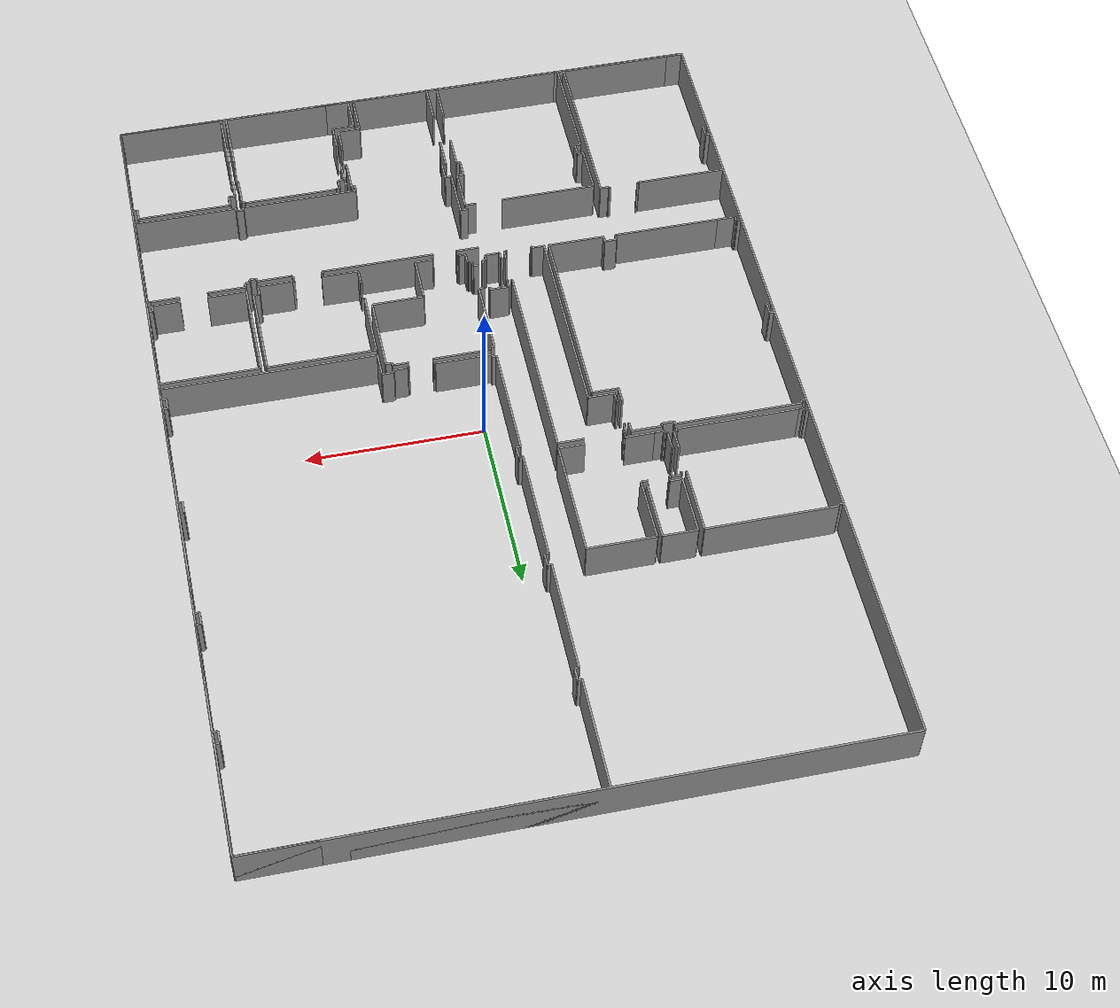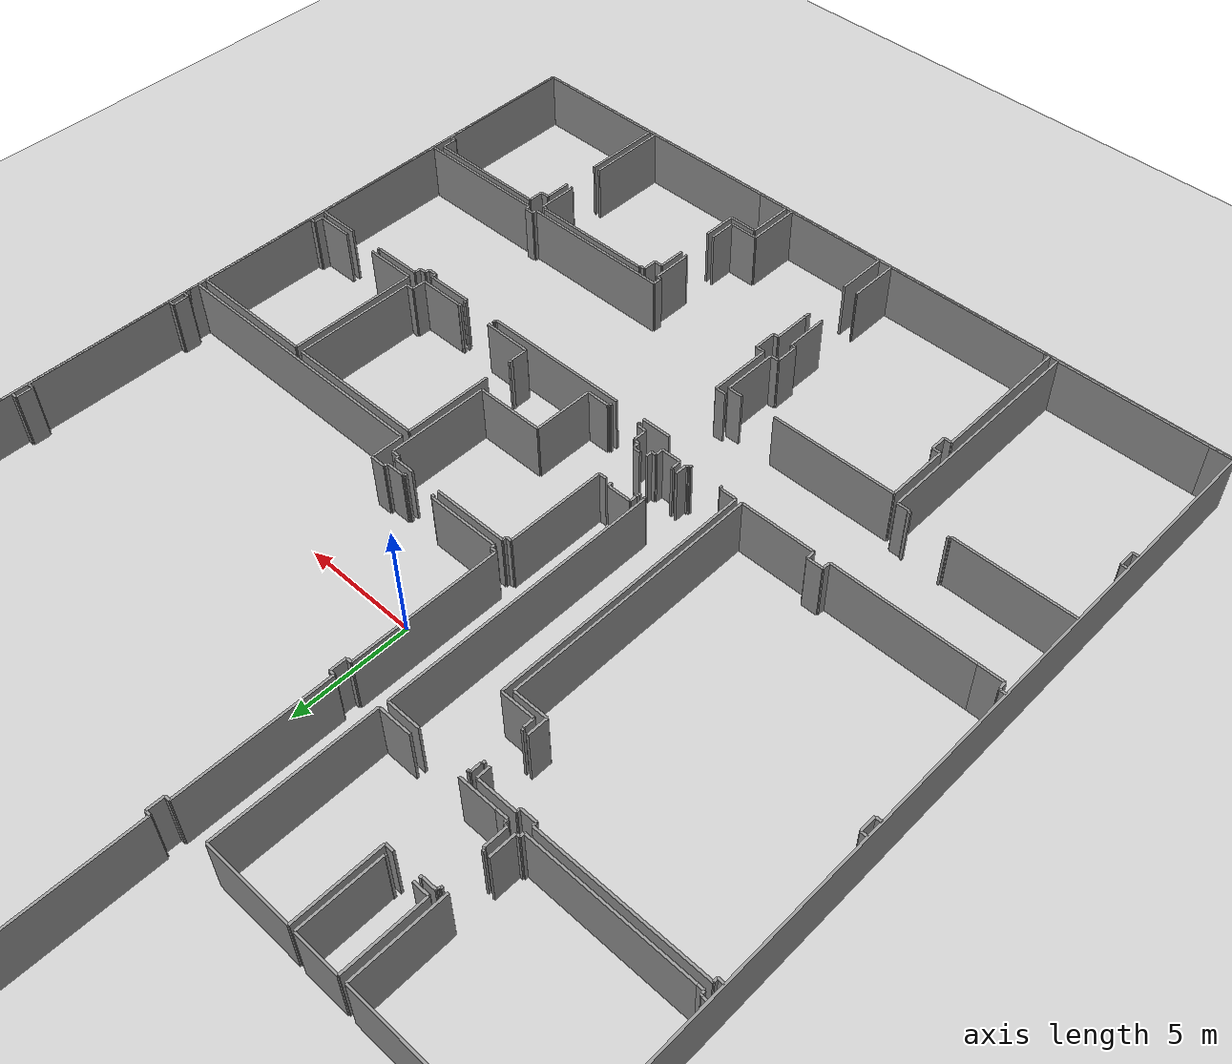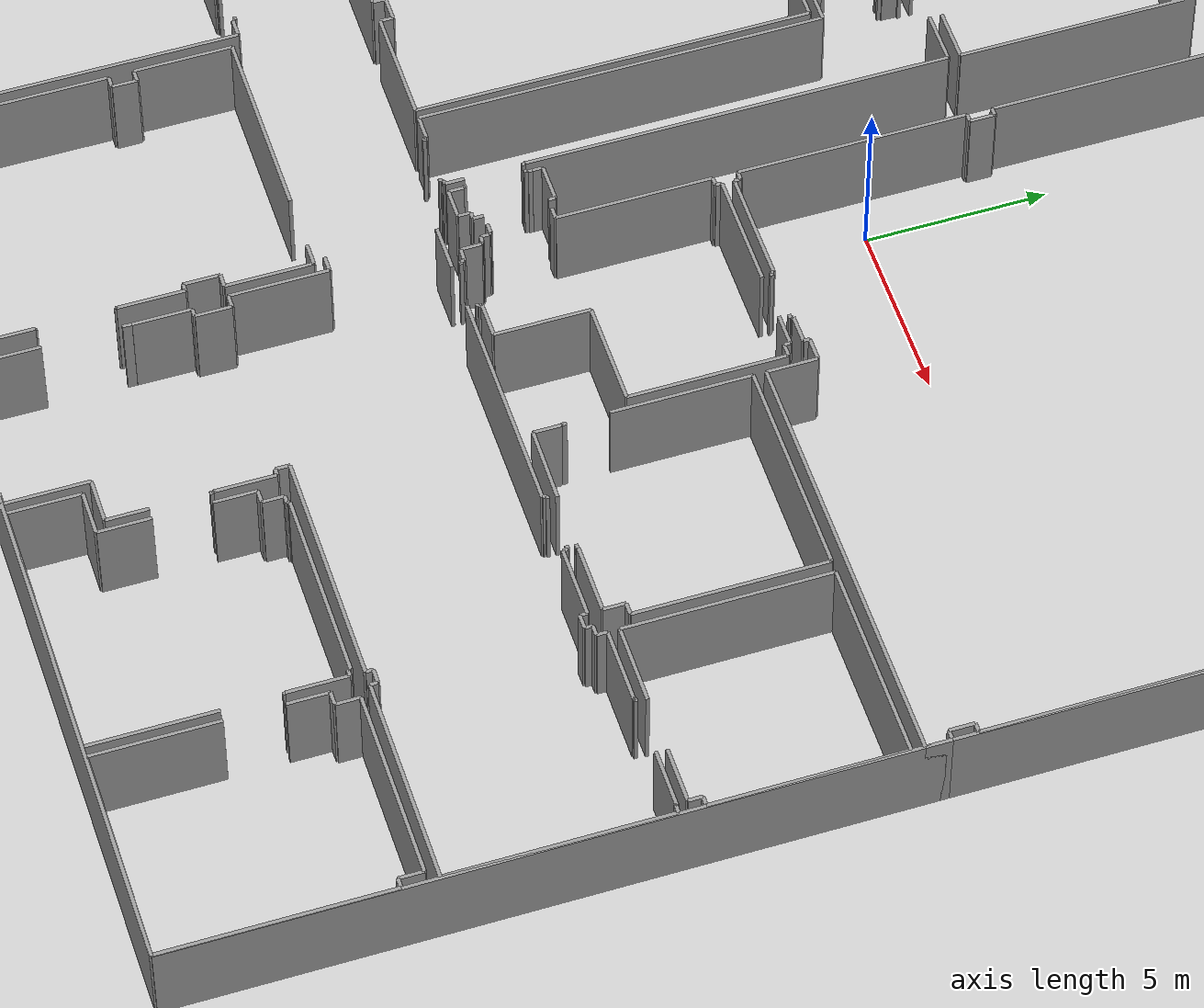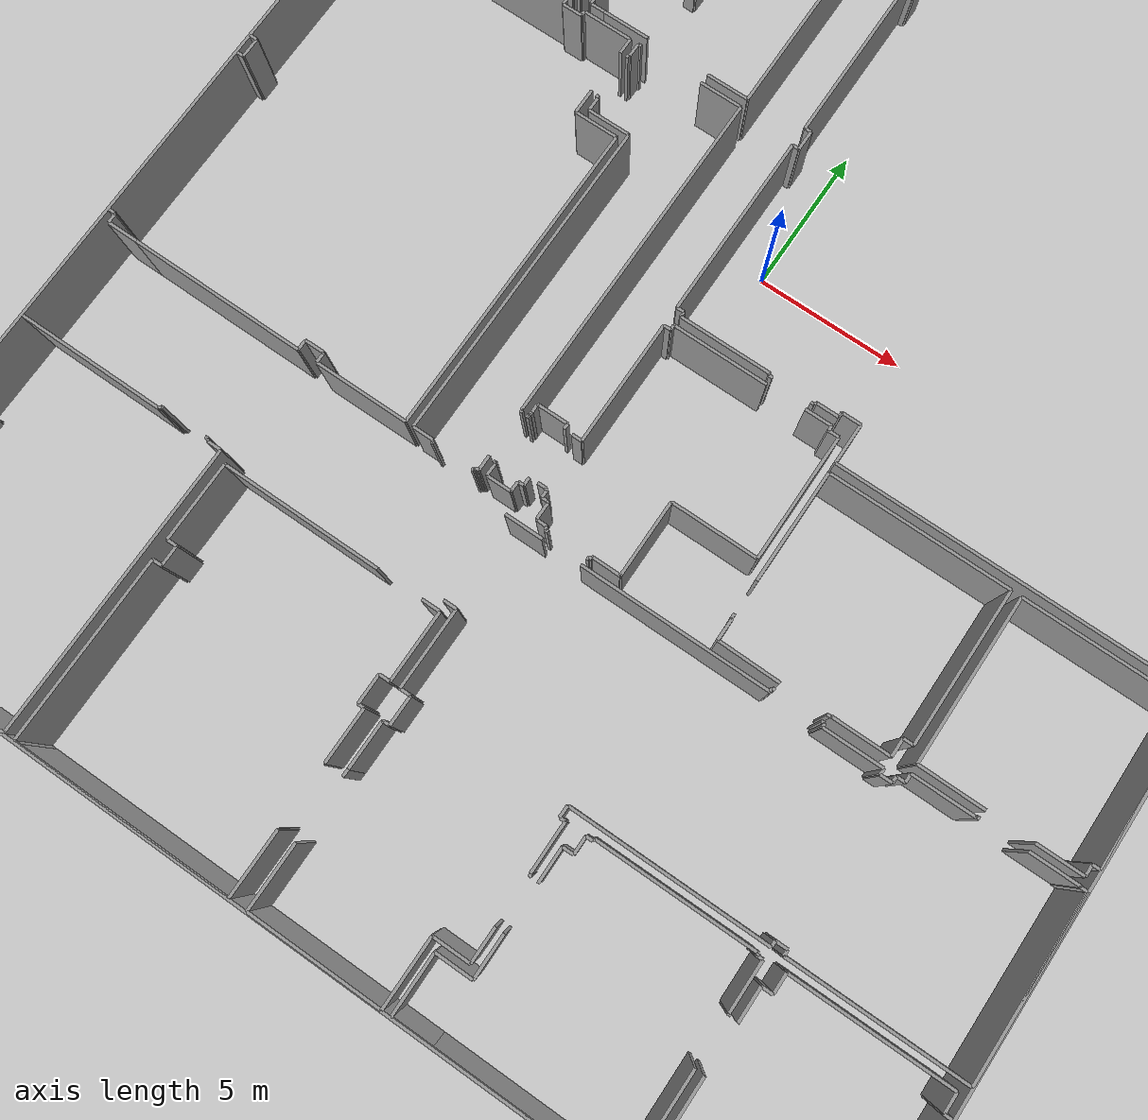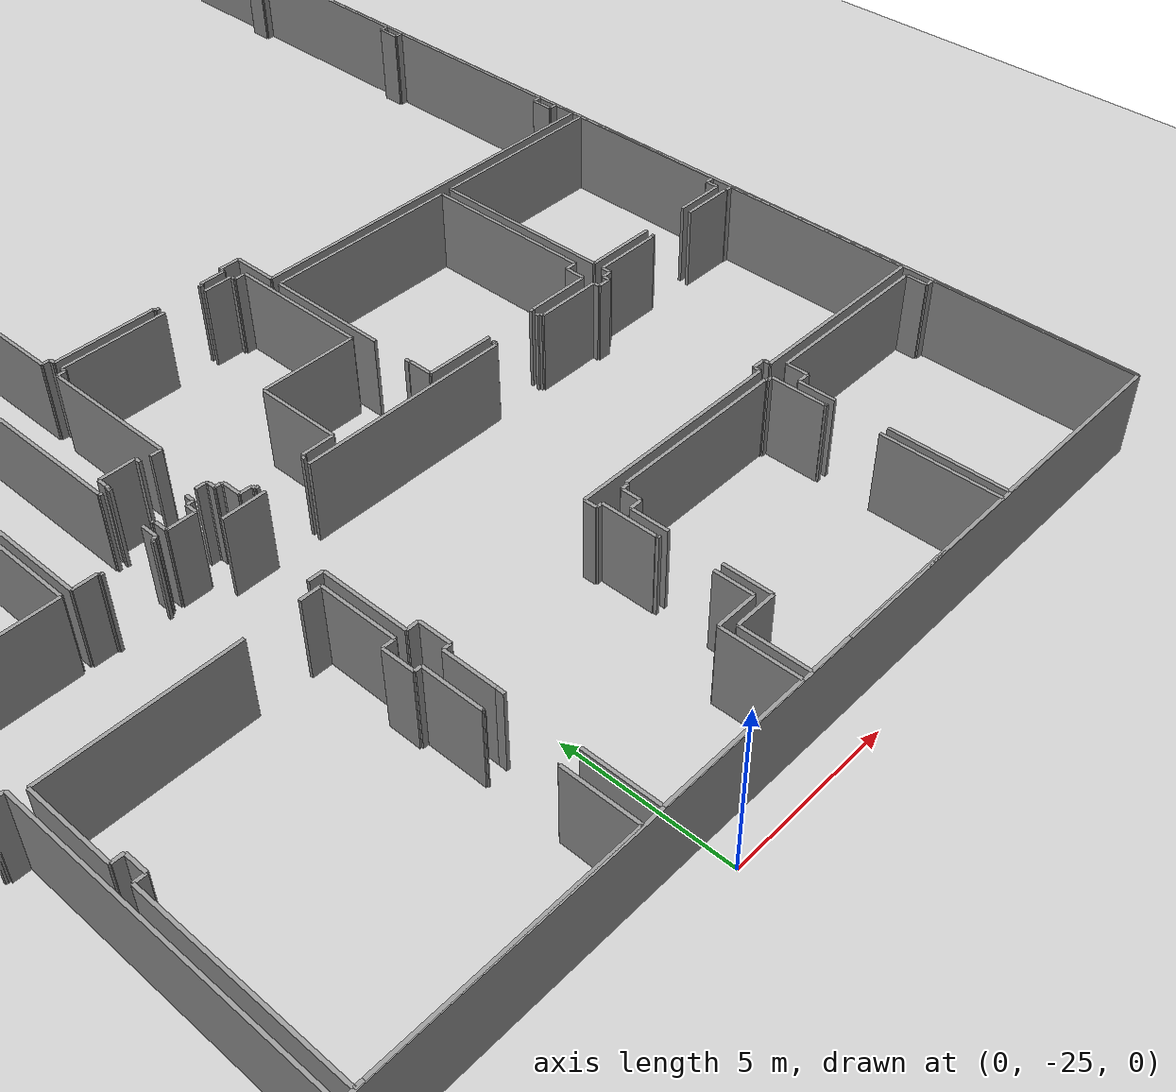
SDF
<sdf version="1.6">
  <world name="default">
    <light name="sun" type="directional">
      <cast_shadows>1</cast_shadows>
      <pose frame="">0 0 10 0 -0 0</pose>
      <diffuse>0.8 0.8 0.8 1</diffuse>
      <specular>0.1 0.1 0.1 1</specular>
      <attenuation>
        <range>1000</range>
        <constant>0.9</constant>
        <linear>0.01</linear>
        <quadratic>0.001</quadratic>
      </attenuation>
      <direction>-0.5 0.5 -1</direction>
    </light>
    <model name="ground_plane">
      <static>1</static>
      <link name="link">
        <collision name="collision">
          <geometry>
            <plane>
              <normal>0 0 1</normal>
              <size>100 100</size>
            </plane>
          </geometry>
          <surface>
            <friction>
              <ode>
                <mu>100</mu>
                <mu2>50</mu2>
              </ode>
              <torsional>
                <ode />
              </torsional>
            </friction>
            <contact>
              <ode />
            </contact>
            <bounce />
          </surface>
          <max_contacts>10</max_contacts>
        </collision>
        <visual name="visual">
          <cast_shadows>0</cast_shadows>
          <geometry>
            <plane>
              <normal>0 0 1</normal>
              <size>100 100</size>
            </plane>
          </geometry>
          <material>
            <script>
              <uri>file://media/materials/scripts/gazebo.material</uri>
              <name>Gazebo/Grey</name>
            </script>
          </material>
        </visual>
        <self_collide>0</self_collide>
        <kinematic>0</kinematic>
        <gravity>1</gravity>
      </link>
    </model>
    <gravity>0 0 -9.8</gravity>
    <magnetic_field>6e-06 2.3e-05 -4.2e-05</magnetic_field>
    <atmosphere type="adiabatic" />
    <physics default="0" name="default_physics" type="ode">
      <max_step_size>0.001</max_step_size>
      <real_time_factor>1</real_time_factor>
      <real_time_update_rate>1000</real_time_update_rate>
    </physics>
    <scene>
      <ambient>0.4 0.4 0.4 1</ambient>
      <background>0.7 0.7 0.7 1</background>
      <shadows>1</shadows>
    </scene>
    <spherical_coordinates>
      <surface_model>EARTH_WGS84</surface_model>
      <latitude_deg>0</latitude_deg>
      <longitude_deg>0</longitude_deg>
      <elevation>0</elevation>
      <heading_deg>0</heading_deg>
    </spherical_coordinates>
  <model name="50055648">
		<static>1</static>
		<link name="Wall_0">
			<collision name="Wall_0_Collision">
				<geometry>
					<box>
						<size>0.265748656648 0.1 2.5</size>
					</box>
				</geometry>
				<pose frame="">0.132874328324 0 1.25 0 0 0</pose>
			</collision>
			<visual name="Wall_0_Visual">
				<pose frame="">0.132874328324 0 1.25 0 0 0</pose>
				<geometry>
					<box>
						<size>0.265748656648 0.1 2.5</size>
					</box>
				</geometry>
				<material>
					<script>
						<uri>file://media/materials/scripts/gazebo.material</uri>
						<name>Gazebo/Grey</name>
					</script>
					<ambient>1 1 1 1</ambient>
				</material>
			</visual>
			<pose frame="">0.557157556433 -20.3636894857 0 0 0 3.14159265359</pose>
		</link>
		<link name="Wall_1">
			<collision name="Wall_1_Collision">
				<geometry>
					<box>
						<size>0.112168290545 0.1 2.5</size>
					</box>
				</geometry>
				<pose frame="">0.0560841452725 0 1.25 0 0 0</pose>
			</collision>
			<visual name="Wall_1_Visual">
				<pose frame="">0.0560841452725 0 1.25 0 0 0</pose>
				<geometry>
					<box>
						<size>0.112168290545 0.1 2.5</size>
					</box>
				</geometry>
				<material>
					<script>
						<uri>file://media/materials/scripts/gazebo.material</uri>
						<name>Gazebo/Grey</name>
					</script>
					<ambient>1 1 1 1</ambient>
				</material>
			</visual>
			<pose frame="">0.291408899785 -20.3636894857 0 0 0 1.57079632679</pose>
		</link>
		<link name="Wall_2">
			<collision name="Wall_2_Collision">
				<geometry>
					<box>
						<size>0.0939563386036 0.1 2.5</size>
					</box>
				</geometry>
				<pose frame="">0.0469781693018 0 1.25 0 0 0</pose>
			</collision>
			<visual name="Wall_2_Visual">
				<pose frame="">0.0469781693018 0 1.25 0 0 0</pose>
				<geometry>
					<box>
						<size>0.0939563386036 0.1 2.5</size>
					</box>
				</geometry>
				<material>
					<script>
						<uri>file://media/materials/scripts/gazebo.material</uri>
						<name>Gazebo/Grey</name>
					</script>
					<ambient>1 1 1 1</ambient>
				</material>
			</visual>
			<pose frame="">0.291408899785 -20.2515211951 0 0 0 2.35619449019</pose>
		</link>
		<link name="Wall_3">
			<collision name="Wall_3_Collision">
				<geometry>
					<box>
						<size>0.220144561172 0.1 2.5</size>
					</box>
				</geometry>
				<pose frame="">0.110072280586 0 1.25 0 0 0</pose>
			</collision>
			<visual name="Wall_3_Visual">
				<pose frame="">0.110072280586 0 1.25 0 0 0</pose>
				<geometry>
					<box>
						<size>0.220144561172 0.1 2.5</size>
					</box>
				</geometry>
				<material>
					<script>
						<uri>file://media/materials/scripts/gazebo.material</uri>
						<name>Gazebo/Grey</name>
					</script>
					<ambient>1 1 1 1</ambient>
				</material>
			</visual>
			<pose frame="">0.224971735623 -20.1850840309 0 0 0 3.14159265359</pose>
		</link>
		<link name="Wall_4">
			<collision name="Wall_4_Collision">
				<geometry>
					<box>
						<size>0.269940676567 0.1 2.5</size>
					</box>
				</geometry>
				<pose frame="">0.134970338283 0 1.25 0 0 0</pose>
			</collision>
			<visual name="Wall_4_Visual">
				<pose frame="">0.134970338283 0 1.25 0 0 0</pose>
				<geometry>
					<box>
						<size>0.269940676567 0.1 2.5</size>
					</box>
				</geometry>
				<material>
					<script>
						<uri>file://media/materials/scripts/gazebo.material</uri>
						<name>Gazebo/Grey</name>
					</script>
					<ambient>1 1 1 1</ambient>
				</material>
			</visual>
			<pose frame="">0.00482717445155 -13.8854943408 0 0 0 0.0</pose>
		</link>
		<link name="Wall_5">
			<collision name="Wall_5_Collision">
				<geometry>
					<box>
						<size>0.132874328324 0.1 2.5</size>
					</box>
				</geometry>
				<pose frame="">0.066437164162 0 1.25 0 0 0</pose>
			</collision>
			<visual name="Wall_5_Visual">
				<pose frame="">0.066437164162 0 1.25 0 0 0</pose>
				<geometry>
					<box>
						<size>0.132874328324 0.1 2.5</size>
					</box>
				</geometry>
				<material>
					<script>
						<uri>file://media/materials/scripts/gazebo.material</uri>
						<name>Gazebo/Grey</name>
					</script>
					<ambient>1 1 1 1</ambient>
				</material>
			</visual>
			<pose frame="">0.274767851018 -13.8854943408 0 0 0 1.57079632679</pose>
		</link>
		<link name="Wall_6">
			<collision name="Wall_6_Collision">
				<geometry>
					<box>
						<size>7.29246325631 0.1 2.5</size>
					</box>
				</geometry>
				<pose frame="">3.64623162816 0 1.25 0 0 0</pose>
			</collision>
			<visual name="Wall_6_Visual">
				<pose frame="">3.64623162816 0 1.25 0 0 0</pose>
				<geometry>
					<box>
						<size>7.29246325631 0.1 2.5</size>
					</box>
				</geometry>
				<material>
					<script>
						<uri>file://media/materials/scripts/gazebo.material</uri>
						<name>Gazebo/Grey</name>
					</script>
					<ambient>1 1 1 1</ambient>
				</material>
			</visual>
			<pose frame="">0.274767851018 -13.7526200124 0 0 0 0.0</pose>
		</link>
		<link name="Wall_7">
			<collision name="Wall_7_Collision">
				<geometry>
					<box>
						<size>3.78285336822 0.1 2.5</size>
					</box>
				</geometry>
				<pose frame="">1.89142668411 0 1.25 0 0 0</pose>
			</collision>
			<visual name="Wall_7_Visual">
				<pose frame="">1.89142668411 0 1.25 0 0 0</pose>
				<geometry>
					<box>
						<size>3.78285336822 0.1 2.5</size>
					</box>
				</geometry>
				<material>
					<script>
						<uri>file://media/materials/scripts/gazebo.material</uri>
						<name>Gazebo/Grey</name>
					</script>
					<ambient>1 1 1 1</ambient>
				</material>
			</visual>
			<pose frame="">7.56723110733 -13.7526200124 0 0 0 -1.57079632679</pose>
		</link>
		<link name="Wall_8">
			<collision name="Wall_8_Collision">
				<geometry>
					<box>
						<size>1.09830921863 0.1 2.5</size>
					</box>
				</geometry>
				<pose frame="">0.549154609316 0 1.25 0 0 0</pose>
			</collision>
			<visual name="Wall_8_Visual">
				<pose frame="">0.549154609316 0 1.25 0 0 0</pose>
				<geometry>
					<box>
						<size>1.09830921863 0.1 2.5</size>
					</box>
				</geometry>
				<material>
					<script>
						<uri>file://media/materials/scripts/gazebo.material</uri>
						<name>Gazebo/Grey</name>
					</script>
					<ambient>1 1 1 1</ambient>
				</material>
			</visual>
			<pose frame="">7.56723110733 -19.0963021303 0 0 0 -1.57079632679</pose>
		</link>
		<link name="Wall_9">
			<collision name="Wall_9_Collision">
				<geometry>
					<box>
						<size>0.160058942341 0.1 2.5</size>
					</box>
				</geometry>
				<pose frame="">0.0800294711703 0 1.25 0 0 0</pose>
			</collision>
			<visual name="Wall_9_Visual">
				<pose frame="">0.0800294711703 0 1.25 0 0 0</pose>
				<geometry>
					<box>
						<size>0.160058942341 0.1 2.5</size>
					</box>
				</geometry>
				<material>
					<script>
						<uri>file://media/materials/scripts/gazebo.material</uri>
						<name>Gazebo/Grey</name>
					</script>
					<ambient>1 1 1 1</ambient>
				</material>
			</visual>
			<pose frame="">7.56723110733 -20.1946113489 0 0 0 3.14159265359</pose>
		</link>
		<link name="Wall_10">
			<collision name="Wall_10_Collision">
				<geometry>
					<box>
						<size>0.181527165559 0.1 2.5</size>
					</box>
				</geometry>
				<pose frame="">0.0907635827797 0 1.25 0 0 0</pose>
			</collision>
			<visual name="Wall_10_Visual">
				<pose frame="">0.0907635827797 0 1.25 0 0 0</pose>
				<geometry>
					<box>
						<size>0.181527165559 0.1 2.5</size>
					</box>
				</geometry>
				<material>
					<script>
						<uri>file://media/materials/scripts/gazebo.material</uri>
						<name>Gazebo/Grey</name>
					</script>
					<ambient>1 1 1 1</ambient>
				</material>
			</visual>
			<pose frame="">7.40717216499 -20.1946113489 0 0 0 -1.57079632679</pose>
		</link>
		<link name="Wall_11">
			<collision name="Wall_11_Collision">
				<geometry>
					<box>
						<size>6.85002592081 0.1 2.5</size>
					</box>
				</geometry>
				<pose frame="">3.4250129604 0 1.25 0 0 0</pose>
			</collision>
			<visual name="Wall_11_Visual">
				<pose frame="">3.4250129604 0 1.25 0 0 0</pose>
				<geometry>
					<box>
						<size>6.85002592081 0.1 2.5</size>
					</box>
				</geometry>
				<material>
					<script>
						<uri>file://media/materials/scripts/gazebo.material</uri>
						<name>Gazebo/Grey</name>
					</script>
					<ambient>1 1 1 1</ambient>
				</material>
			</visual>
			<pose frame="">7.40717216499 -20.3761385145 0 0 0 3.13977528299</pose>
		</link>
		<link name="Wall_12">
			<collision name="Wall_12_Collision">
				<geometry>
					<box>
						<size>0.0163869869539 0.1 2.5</size>
					</box>
				</geometry>
				<pose frame="">0.00819349347696 0 1.25 0 0 0</pose>
			</collision>
			<visual name="Wall_12_Visual">
				<pose frame="">0.00819349347696 0 1.25 0 0 0</pose>
				<geometry>
					<box>
						<size>0.0163869869539 0.1 2.5</size>
					</box>
				</geometry>
				<material>
					<script>
						<uri>file://media/materials/scripts/gazebo.material</uri>
						<name>Gazebo/Grey</name>
					</script>
					<ambient>1 1 1 1</ambient>
				</material>
			</visual>
			<pose frame="">7.91643906963 -17.0936598875 0 0 0 3.14159265359</pose>
		</link>
		<link name="Wall_13">
			<collision name="Wall_13_Collision">
				<geometry>
					<box>
						<size>3.3391344114 0.1 2.5</size>
					</box>
				</geometry>
				<pose frame="">1.6695672057 0 1.25 0 0 0</pose>
			</collision>
			<visual name="Wall_13_Visual">
				<pose frame="">1.6695672057 0 1.25 0 0 0</pose>
				<geometry>
					<box>
						<size>3.3391344114 0.1 2.5</size>
					</box>
				</geometry>
				<material>
					<script>
						<uri>file://media/materials/scripts/gazebo.material</uri>
						<name>Gazebo/Grey</name>
					</script>
					<ambient>1 1 1 1</ambient>
				</material>
			</visual>
			<pose frame="">7.90005208267 -17.0936598875 0 0 0 1.57079632679</pose>
		</link>
		<link name="Wall_14">
			<collision name="Wall_14_Collision">
				<geometry>
					<box>
						<size>1.92210464806 0.1 2.5</size>
					</box>
				</geometry>
				<pose frame="">0.96105232403 0 1.25 0 0 0</pose>
			</collision>
			<visual name="Wall_14_Visual">
				<pose frame="">0.96105232403 0 1.25 0 0 0</pose>
				<geometry>
					<box>
						<size>1.92210464806 0.1 2.5</size>
					</box>
				</geometry>
				<material>
					<script>
						<uri>file://media/materials/scripts/gazebo.material</uri>
						<name>Gazebo/Grey</name>
					</script>
					<ambient>1 1 1 1</ambient>
				</material>
			</visual>
			<pose frame="">7.90005208267 -13.754525476 0 0 0 0.0</pose>
		</link>
		<link name="Wall_15">
			<collision name="Wall_15_Collision">
				<geometry>
					<box>
						<size>3.33684785508 0.1 2.5</size>
					</box>
				</geometry>
				<pose frame="">1.66842392754 0 1.25 0 0 0</pose>
			</collision>
			<visual name="Wall_15_Visual">
				<pose frame="">1.66842392754 0 1.25 0 0 0</pose>
				<geometry>
					<box>
						<size>3.33684785508 0.1 2.5</size>
					</box>
				</geometry>
				<material>
					<script>
						<uri>file://media/materials/scripts/gazebo.material</uri>
						<name>Gazebo/Grey</name>
					</script>
					<ambient>1 1 1 1</ambient>
				</material>
			</visual>
			<pose frame="">9.82215673073 -13.754525476 0 0 0 -1.57079632679</pose>
		</link>
		<link name="Wall_16">
			<collision name="Wall_16_Collision">
				<geometry>
					<box>
						<size>0.0793943166372 0.1 2.5</size>
					</box>
				</geometry>
				<pose frame="">0.0396971583186 0 1.25 0 0 0</pose>
			</collision>
			<visual name="Wall_16_Visual">
				<pose frame="">0.0396971583186 0 1.25 0 0 0</pose>
				<geometry>
					<box>
						<size>0.0793943166372 0.1 2.5</size>
					</box>
				</geometry>
				<material>
					<script>
						<uri>file://media/materials/scripts/gazebo.material</uri>
						<name>Gazebo/Grey</name>
					</script>
					<ambient>1 1 1 1</ambient>
				</material>
			</visual>
			<pose frame="">9.82215673073 -17.0913733311 0 0 0 3.14159265359</pose>
		</link>
		<link name="Wall_17">
			<collision name="Wall_17_Collision">
				<geometry>
					<box>
						<size>0.671997386178 0.1 2.5</size>
					</box>
				</geometry>
				<pose frame="">0.335998693089 0 1.25 0 0 0</pose>
			</collision>
			<visual name="Wall_17_Visual">
				<pose frame="">0.335998693089 0 1.25 0 0 0</pose>
				<geometry>
					<box>
						<size>0.671997386178 0.1 2.5</size>
					</box>
				</geometry>
				<material>
					<script>
						<uri>file://media/materials/scripts/gazebo.material</uri>
						<name>Gazebo/Grey</name>
					</script>
					<ambient>1 1 1 1</ambient>
				</material>
			</visual>
			<pose frame="">8.58843256564 -17.0913733311 0 0 0 -3.13819002022</pose>
		</link>
		<link name="Wall_18">
			<collision name="Wall_18_Collision">
				<geometry>
					<box>
						<size>0.508631750105 0.1 2.5</size>
					</box>
				</geometry>
				<pose frame="">0.254315875052 0 1.25 0 0 0</pose>
			</collision>
			<visual name="Wall_18_Visual">
				<pose frame="">0.254315875052 0 1.25 0 0 0</pose>
				<geometry>
					<box>
						<size>0.508631750105 0.1 2.5</size>
					</box>
				</geometry>
				<material>
					<script>
						<uri>file://media/materials/scripts/gazebo.material</uri>
						<name>Gazebo/Grey</name>
					</script>
					<ambient>1 1 1 1</ambient>
				</material>
			</visual>
			<pose frame="">8.59973831633 -20.3677544747 0 0 0 3.14159265359</pose>
		</link>
		<link name="Wall_19">
			<collision name="Wall_19_Collision">
				<geometry>
					<box>
						<size>0.144434140826 0.1 2.5</size>
					</box>
				</geometry>
				<pose frame="">0.0722170704132 0 1.25 0 0 0</pose>
			</collision>
			<visual name="Wall_19_Visual">
				<pose frame="">0.0722170704132 0 1.25 0 0 0</pose>
				<geometry>
					<box>
						<size>0.144434140826 0.1 2.5</size>
					</box>
				</geometry>
				<material>
					<script>
						<uri>file://media/materials/scripts/gazebo.material</uri>
						<name>Gazebo/Grey</name>
					</script>
					<ambient>1 1 1 1</ambient>
				</material>
			</visual>
			<pose frame="">8.09110656623 -20.3677544747 0 0 0 1.57079632679</pose>
		</link>
		<link name="Wall_20">
			<collision name="Wall_20_Collision">
				<geometry>
					<box>
						<size>0.0765317725464 0.1 2.5</size>
					</box>
				</geometry>
				<pose frame="">0.0382658862732 0 1.25 0 0 0</pose>
			</collision>
			<visual name="Wall_20_Visual">
				<pose frame="">0.0382658862732 0 1.25 0 0 0</pose>
				<geometry>
					<box>
						<size>0.0765317725464 0.1 2.5</size>
					</box>
				</geometry>
				<material>
					<script>
						<uri>file://media/materials/scripts/gazebo.material</uri>
						<name>Gazebo/Grey</name>
					</script>
					<ambient>1 1 1 1</ambient>
				</material>
			</visual>
			<pose frame="">8.09110656623 -20.2233203338 0 0 0 2.80671949291</pose>
		</link>
		<link name="Wall_21">
			<collision name="Wall_21_Collision">
				<geometry>
					<box>
						<size>0.100481447136 0.1 2.5</size>
					</box>
				</geometry>
				<pose frame="">0.050240723568 0 1.25 0 0 0</pose>
			</collision>
			<visual name="Wall_21_Visual">
				<pose frame="">0.050240723568 0 1.25 0 0 0</pose>
				<geometry>
					<box>
						<size>0.100481447136 0.1 2.5</size>
					</box>
				</geometry>
				<material>
					<script>
						<uri>file://media/materials/scripts/gazebo.material</uri>
						<name>Gazebo/Grey</name>
					</script>
					<ambient>1 1 1 1</ambient>
				</material>
			</visual>
			<pose frame="">8.01882598036 -20.1981682143 0 0 0 3.14159265359</pose>
		</link>
		<link name="Wall_22">
			<collision name="Wall_22_Collision">
				<geometry>
					<box>
						<size>0.972294559266 0.1 2.5</size>
					</box>
				</geometry>
				<pose frame="">0.486147279633 0 1.25 0 0 0</pose>
			</collision>
			<visual name="Wall_22_Visual">
				<pose frame="">0.486147279633 0 1.25 0 0 0</pose>
				<geometry>
					<box>
						<size>0.972294559266 0.1 2.5</size>
					</box>
				</geometry>
				<material>
					<script>
						<uri>file://media/materials/scripts/gazebo.material</uri>
						<name>Gazebo/Grey</name>
					</script>
					<ambient>1 1 1 1</ambient>
				</material>
			</visual>
			<pose frame="">7.91834453322 -20.1981682143 0 0 0 1.57079632679</pose>
		</link>
		<link name="Wall_23">
			<collision name="Wall_23_Collision">
				<geometry>
					<box>
						<size>0.0813737817576 0.1 2.5</size>
					</box>
				</geometry>
				<pose frame="">0.0406868908788 0 1.25 0 0 0</pose>
			</collision>
			<visual name="Wall_23_Visual">
				<pose frame="">0.0406868908788 0 1.25 0 0 0</pose>
				<geometry>
					<box>
						<size>0.0813737817576 0.1 2.5</size>
					</box>
				</geometry>
				<material>
					<script>
						<uri>file://media/materials/scripts/gazebo.material</uri>
						<name>Gazebo/Grey</name>
					</script>
					<ambient>1 1 1 1</ambient>
				</material>
			</visual>
			<pose frame="">7.91834453322 -19.2258736551 0 0 0 2.72194179145</pose>
		</link>
		<link name="Wall_24">
			<collision name="Wall_24_Collision">
				<geometry>
					<box>
						<size>0.0832052438358 0.1 2.5</size>
					</box>
				</geometry>
				<pose frame="">0.0416026219179 0 1.25 0 0 0</pose>
			</collision>
			<visual name="Wall_24_Visual">
				<pose frame="">0.0416026219179 0 1.25 0 0 0</pose>
				<geometry>
					<box>
						<size>0.0832052438358 0.1 2.5</size>
					</box>
				</geometry>
				<material>
					<script>
						<uri>file://media/materials/scripts/gazebo.material</uri>
						<name>Gazebo/Grey</name>
					</script>
					<ambient>1 1 1 1</ambient>
				</material>
			</visual>
			<pose frame="">7.84403145285 -19.1927185884 0 0 0 1.57079632679</pose>
		</link>
		<link name="Wall_25">
			<collision name="Wall_25_Collision">
				<geometry>
					<box>
						<size>0.0973056744706 0.1 2.5</size>
					</box>
				</geometry>
				<pose frame="">0.0486528372353 0 1.25 0 0 0</pose>
			</collision>
			<visual name="Wall_25_Visual">
				<pose frame="">0.0486528372353 0 1.25 0 0 0</pose>
				<geometry>
					<box>
						<size>0.0973056744706 0.1 2.5</size>
					</box>
				</geometry>
				<material>
					<script>
						<uri>file://media/materials/scripts/gazebo.material</uri>
						<name>Gazebo/Grey</name>
					</script>
					<ambient>1 1 1 1</ambient>
				</material>
			</visual>
			<pose frame="">7.84403145285 -17.5615147165 0 0 0 1.57079632679</pose>
		</link>
		<link name="Wall_26">
			<collision name="Wall_26_Collision">
				<geometry>
					<box>
						<size>0.0570368770722 0.1 2.5</size>
					</box>
				</geometry>
				<pose frame="">0.0285184385361 0 1.25 0 0 0</pose>
			</collision>
			<visual name="Wall_26_Visual">
				<pose frame="">0.0285184385361 0 1.25 0 0 0</pose>
				<geometry>
					<box>
						<size>0.0570368770722 0.1 2.5</size>
					</box>
				</geometry>
				<material>
					<script>
						<uri>file://media/materials/scripts/gazebo.material</uri>
						<name>Gazebo/Grey</name>
					</script>
					<ambient>1 1 1 1</ambient>
				</material>
			</visual>
			<pose frame="">7.84403145285 -17.4642090421 0 0 0 0.0</pose>
		</link>
		<link name="Wall_27">
			<collision name="Wall_27_Collision">
				<geometry>
					<box>
						<size>0.102132848922 0.1 2.5</size>
					</box>
				</geometry>
				<pose frame="">0.0510664244611 0 1.25 0 0 0</pose>
			</collision>
			<visual name="Wall_27_Visual">
				<pose frame="">0.0510664244611 0 1.25 0 0 0</pose>
				<geometry>
					<box>
						<size>0.102132848922 0.1 2.5</size>
					</box>
				</geometry>
				<material>
					<script>
						<uri>file://media/materials/scripts/gazebo.material</uri>
						<name>Gazebo/Grey</name>
					</script>
					<ambient>1 1 1 1</ambient>
				</material>
			</visual>
			<pose frame="">7.90106832992 -17.4642090421 0 0 0 1.57079632679</pose>
		</link>
		<link name="Wall_28">
			<collision name="Wall_28_Collision">
				<geometry>
					<box>
						<size>0.569733616189 0.1 2.5</size>
					</box>
				</geometry>
				<pose frame="">0.284866808094 0 1.25 0 0 0</pose>
			</collision>
			<visual name="Wall_28_Visual">
				<pose frame="">0.284866808094 0 1.25 0 0 0</pose>
				<geometry>
					<box>
						<size>0.569733616189 0.1 2.5</size>
					</box>
				</geometry>
				<material>
					<script>
						<uri>file://media/materials/scripts/gazebo.material</uri>
						<name>Gazebo/Grey</name>
					</script>
					<ambient>1 1 1 1</ambient>
				</material>
			</visual>
			<pose frame="">7.90106832992 -17.3620761931 0 0 0 0.0</pose>
		</link>
		<link name="Wall_29">
			<collision name="Wall_29_Collision">
				<geometry>
					<box>
						<size>0.0213411923121 0.1 2.5</size>
					</box>
				</geometry>
				<pose frame="">0.010670596156 0 1.25 0 0 0</pose>
			</collision>
			<visual name="Wall_29_Visual">
				<pose frame="">0.010670596156 0 1.25 0 0 0</pose>
				<geometry>
					<box>
						<size>0.0213411923121 0.1 2.5</size>
					</box>
				</geometry>
				<material>
					<script>
						<uri>file://media/materials/scripts/gazebo.material</uri>
						<name>Gazebo/Grey</name>
					</script>
					<ambient>1 1 1 1</ambient>
				</material>
			</visual>
			<pose frame="">8.47080194611 -17.3620761931 0 0 0 1.57079632679</pose>
		</link>
		<link name="Wall_30">
			<collision name="Wall_30_Collision">
				<geometry>
					<box>
						<size>0.109246579693 0.1 2.5</size>
					</box>
				</geometry>
				<pose frame="">0.0546232898464 0 1.25 0 0 0</pose>
			</collision>
			<visual name="Wall_30_Visual">
				<pose frame="">0.0546232898464 0 1.25 0 0 0</pose>
				<geometry>
					<box>
						<size>0.109246579693 0.1 2.5</size>
					</box>
				</geometry>
				<material>
					<script>
						<uri>file://media/materials/scripts/gazebo.material</uri>
						<name>Gazebo/Grey</name>
					</script>
					<ambient>1 1 1 1</ambient>
				</material>
			</visual>
			<pose frame="">8.47080194611 -17.3407350008 0 0 0 0.0</pose>
		</link>
		<link name="Wall_31">
			<collision name="Wall_31_Collision">
				<geometry>
					<box>
						<size>0.377027730847 0.1 2.5</size>
					</box>
				</geometry>
				<pose frame="">0.188513865423 0 1.25 0 0 0</pose>
			</collision>
			<visual name="Wall_31_Visual">
				<pose frame="">0.188513865423 0 1.25 0 0 0</pose>
				<geometry>
					<box>
						<size>0.377027730847 0.1 2.5</size>
					</box>
				</geometry>
				<material>
					<script>
						<uri>file://media/materials/scripts/gazebo.material</uri>
						<name>Gazebo/Grey</name>
					</script>
					<ambient>1 1 1 1</ambient>
				</material>
			</visual>
			<pose frame="">9.71633998552 -17.3407350008 0 0 0 0.0</pose>
		</link>
		<link name="Wall_32">
			<collision name="Wall_32_Collision">
				<geometry>
					<box>
						<size>3.57185503233 0.1 2.5</size>
					</box>
				</geometry>
				<pose frame="">1.78592751616 0 1.25 0 0 0</pose>
			</collision>
			<visual name="Wall_32_Visual">
				<pose frame="">1.78592751616 0 1.25 0 0 0</pose>
				<geometry>
					<box>
						<size>3.57185503233 0.1 2.5</size>
					</box>
				</geometry>
				<material>
					<script>
						<uri>file://media/materials/scripts/gazebo.material</uri>
						<name>Gazebo/Grey</name>
					</script>
					<ambient>1 1 1 1</ambient>
				</material>
			</visual>
			<pose frame="">10.0933677164 -17.3407350008 0 0 0 1.57079632679</pose>
		</link>
		<link name="Wall_33">
			<collision name="Wall_33_Collision">
				<geometry>
					<box>
						<size>3.79898629337 0.1 2.5</size>
					</box>
				</geometry>
				<pose frame="">1.89949314668 0 1.25 0 0 0</pose>
			</collision>
			<visual name="Wall_33_Visual">
				<pose frame="">1.89949314668 0 1.25 0 0 0</pose>
				<geometry>
					<box>
						<size>3.79898629337 0.1 2.5</size>
					</box>
				</geometry>
				<material>
					<script>
						<uri>file://media/materials/scripts/gazebo.material</uri>
						<name>Gazebo/Grey</name>
					</script>
					<ambient>1 1 1 1</ambient>
				</material>
			</visual>
			<pose frame="">10.0933677164 -13.7688799685 0 0 0 0.0</pose>
		</link>
		<link name="Wall_34">
			<collision name="Wall_34_Collision">
				<geometry>
					<box>
						<size>6.59722310438 0.1 2.5</size>
					</box>
				</geometry>
				<pose frame="">3.29861155219 0 1.25 0 0 0</pose>
			</collision>
			<visual name="Wall_34_Visual">
				<pose frame="">3.29861155219 0 1.25 0 0 0</pose>
				<geometry>
					<box>
						<size>6.59722310438 0.1 2.5</size>
					</box>
				</geometry>
				<material>
					<script>
						<uri>file://media/materials/scripts/gazebo.material</uri>
						<name>Gazebo/Grey</name>
					</script>
					<ambient>1 1 1 1</ambient>
				</material>
			</visual>
			<pose frame="">13.8923540097 -13.7688799685 0 0 0 -1.57079632679</pose>
		</link>
		<link name="Wall_35">
			<collision name="Wall_35_Collision">
				<geometry>
					<box>
						<size>1.46479338423 0.1 2.5</size>
					</box>
				</geometry>
				<pose frame="">0.732396692115 0 1.25 0 0 0</pose>
			</collision>
			<visual name="Wall_35_Visual">
				<pose frame="">0.732396692115 0 1.25 0 0 0</pose>
				<geometry>
					<box>
						<size>1.46479338423 0.1 2.5</size>
					</box>
				</geometry>
				<material>
					<script>
						<uri>file://media/materials/scripts/gazebo.material</uri>
						<name>Gazebo/Grey</name>
					</script>
					<ambient>1 1 1 1</ambient>
				</material>
			</visual>
			<pose frame="">13.8923540097 -20.3661030729 0 0 0 3.14159265359</pose>
		</link>
		<link name="Wall_36">
			<collision name="Wall_36_Collision">
				<geometry>
					<box>
						<size>1.61646913028 0.1 2.5</size>
					</box>
				</geometry>
				<pose frame="">0.80823456514 0 1.25 0 0 0</pose>
			</collision>
			<visual name="Wall_36_Visual">
				<pose frame="">0.80823456514 0 1.25 0 0 0</pose>
				<geometry>
					<box>
						<size>1.61646913028 0.1 2.5</size>
					</box>
				</geometry>
				<material>
					<script>
						<uri>file://media/materials/scripts/gazebo.material</uri>
						<name>Gazebo/Grey</name>
					</script>
					<ambient>1 1 1 1</ambient>
				</material>
			</visual>
			<pose frame="">10.2162066031 -20.3661030729 0 0 0 -3.14057104294</pose>
		</link>
		<link name="Wall_37">
			<collision name="Wall_37_Collision">
				<geometry>
					<box>
						<size>1.05575386492 0.1 2.5</size>
					</box>
				</geometry>
				<pose frame="">0.527876932458 0 1.25 0 0 0</pose>
			</collision>
			<visual name="Wall_37_Visual">
				<pose frame="">0.527876932458 0 1.25 0 0 0</pose>
				<geometry>
					<box>
						<size>1.05575386492 0.1 2.5</size>
					</box>
				</geometry>
				<material>
					<script>
						<uri>file://media/materials/scripts/gazebo.material</uri>
						<name>Gazebo/Grey</name>
					</script>
					<ambient>1 1 1 1</ambient>
				</material>
			</visual>
			<pose frame="">1.34297074478 -34.5305572846 0 0 0 3.14159265359</pose>
		</link>
		<link name="Wall_38">
			<collision name="Wall_38_Collision">
				<geometry>
					<box>
						<size>0.288741250746 0.1 2.5</size>
					</box>
				</geometry>
				<pose frame="">0.144370625373 0 1.25 0 0 0</pose>
			</collision>
			<visual name="Wall_38_Visual">
				<pose frame="">0.144370625373 0 1.25 0 0 0</pose>
				<geometry>
					<box>
						<size>0.288741250746 0.1 2.5</size>
					</box>
				</geometry>
				<material>
					<script>
						<uri>file://media/materials/scripts/gazebo.material</uri>
						<name>Gazebo/Grey</name>
					</script>
					<ambient>1 1 1 1</ambient>
				</material>
			</visual>
			<pose frame="">0.287216879867 -34.5305572846 0 0 0 1.57079632679</pose>
		</link>
		<link name="Wall_39">
			<collision name="Wall_39_Collision">
				<geometry>
					<box>
						<size>0.0676090898377 0.1 2.5</size>
					</box>
				</geometry>
				<pose frame="">0.0338045449188 0 1.25 0 0 0</pose>
			</collision>
			<visual name="Wall_39_Visual">
				<pose frame="">0.0338045449188 0 1.25 0 0 0</pose>
				<geometry>
					<box>
						<size>0.0676090898377 0.1 2.5</size>
					</box>
				</geometry>
				<material>
					<script>
						<uri>file://media/materials/scripts/gazebo.material</uri>
						<name>Gazebo/Grey</name>
					</script>
					<ambient>1 1 1 1</ambient>
				</material>
			</visual>
			<pose frame="">0.287216879867 -34.2418160338 0 0 0 2.31366695557</pose>
		</link>
		<link name="Wall_40">
			<collision name="Wall_40_Collision">
				<geometry>
					<box>
						<size>0.236658579032 0.1 2.5</size>
					</box>
				</geometry>
				<pose frame="">0.118329289516 0 1.25 0 0 0</pose>
			</collision>
			<visual name="Wall_40_Visual">
				<pose frame="">0.118329289516 0 1.25 0 0 0</pose>
				<geometry>
					<box>
						<size>0.236658579032 0.1 2.5</size>
					</box>
				</geometry>
				<material>
					<script>
						<uri>file://media/materials/scripts/gazebo.material</uri>
						<name>Gazebo/Grey</name>
					</script>
					<ambient>1 1 1 1</ambient>
				</material>
			</visual>
			<pose frame="">0.241485753484 -34.1920199184 0 0 0 3.14159265359</pose>
		</link>
		<link name="Wall_41">
			<collision name="Wall_41_Collision">
				<geometry>
					<box>
						<size>0.270829892913 0.1 2.5</size>
					</box>
				</geometry>
				<pose frame="">0.135414946456 0 1.25 0 0 0</pose>
			</collision>
			<visual name="Wall_41_Visual">
				<pose frame="">0.135414946456 0 1.25 0 0 0</pose>
				<geometry>
					<box>
						<size>0.270829892913 0.1 2.5</size>
					</box>
				</geometry>
				<material>
					<script>
						<uri>file://media/materials/scripts/gazebo.material</uri>
						<name>Gazebo/Grey</name>
					</script>
					<ambient>1 1 1 1</ambient>
				</material>
			</visual>
			<pose frame="">0.00482717445155 -27.8817596321 0 0 0 0.0</pose>
		</link>
		<link name="Wall_42">
			<collision name="Wall_42_Collision">
				<geometry>
					<box>
						<size>0.681393783107 0.1 2.5</size>
					</box>
				</geometry>
				<pose frame="">0.340696891554 0 1.25 0 0 0</pose>
			</collision>
			<visual name="Wall_42_Visual">
				<pose frame="">0.340696891554 0 1.25 0 0 0</pose>
				<geometry>
					<box>
						<size>0.681393783107 0.1 2.5</size>
					</box>
				</geometry>
				<material>
					<script>
						<uri>file://media/materials/scripts/gazebo.material</uri>
						<name>Gazebo/Grey</name>
					</script>
					<ambient>1 1 1 1</ambient>
				</material>
			</visual>
			<pose frame="">0.275657067364 -27.8817596321 0 0 0 1.57079632679</pose>
		</link>
		<link name="Wall_43">
			<collision name="Wall_43_Collision">
				<geometry>
					<box>
						<size>0.270067707473 0.1 2.5</size>
					</box>
				</geometry>
				<pose frame="">0.135033853737 0 1.25 0 0 0</pose>
			</collision>
			<visual name="Wall_43_Visual">
				<pose frame="">0.135033853737 0 1.25 0 0 0</pose>
				<geometry>
					<box>
						<size>0.270067707473 0.1 2.5</size>
					</box>
				</geometry>
				<material>
					<script>
						<uri>file://media/materials/scripts/gazebo.material</uri>
						<name>Gazebo/Grey</name>
					</script>
					<ambient>1 1 1 1</ambient>
				</material>
			</visual>
			<pose frame="">0.275657067364 -27.200365849 0 0 0 3.14159265359</pose>
		</link>
		<link name="Wall_44">
			<collision name="Wall_44_Collision">
				<geometry>
					<box>
						<size>0.275403005551 0.1 2.5</size>
					</box>
				</geometry>
				<pose frame="">0.137701502776 0 1.25 0 0 0</pose>
			</collision>
			<visual name="Wall_44_Visual">
				<pose frame="">0.137701502776 0 1.25 0 0 0</pose>
				<geometry>
					<box>
						<size>0.275403005551 0.1 2.5</size>
					</box>
				</geometry>
				<material>
					<script>
						<uri>file://media/materials/scripts/gazebo.material</uri>
						<name>Gazebo/Grey</name>
					</script>
					<ambient>1 1 1 1</ambient>
				</material>
			</visual>
			<pose frame="">0.00558935989126 -20.8862946355 0 0 0 0.0</pose>
		</link>
		<link name="Wall_45">
			<collision name="Wall_45_Collision">
				<geometry>
					<box>
						<size>0.177589207454 0.1 2.5</size>
					</box>
				</geometry>
				<pose frame="">0.0887946037271 0 1.25 0 0 0</pose>
			</collision>
			<visual name="Wall_45_Visual">
				<pose frame="">0.0887946037271 0 1.25 0 0 0</pose>
				<geometry>
					<box>
						<size>0.177589207454 0.1 2.5</size>
					</box>
				</geometry>
				<material>
					<script>
						<uri>file://media/materials/scripts/gazebo.material</uri>
						<name>Gazebo/Grey</name>
					</script>
					<ambient>1 1 1 1</ambient>
				</material>
			</visual>
			<pose frame="">0.280992365443 -20.8862946355 0 0 0 1.57079632679</pose>
		</link>
		<link name="Wall_46">
			<collision name="Wall_46_Collision">
				<geometry>
					<box>
						<size>7.10674407083 0.1 2.5</size>
					</box>
				</geometry>
				<pose frame="">3.55337203542 0 1.25 0 0 0</pose>
			</collision>
			<visual name="Wall_46_Visual">
				<pose frame="">3.55337203542 0 1.25 0 0 0</pose>
				<geometry>
					<box>
						<size>7.10674407083 0.1 2.5</size>
					</box>
				</geometry>
				<material>
					<script>
						<uri>file://media/materials/scripts/gazebo.material</uri>
						<name>Gazebo/Grey</name>
					</script>
					<ambient>1 1 1 1</ambient>
				</material>
			</visual>
			<pose frame="">0.280992365443 -20.708705428 0 0 0 0.0</pose>
		</link>
		<link name="Wall_47">
			<collision name="Wall_47_Collision">
				<geometry>
					<box>
						<size>0.164632054979 0.1 2.5</size>
					</box>
				</geometry>
				<pose frame="">0.0823160274895 0 1.25 0 0 0</pose>
			</collision>
			<visual name="Wall_47_Visual">
				<pose frame="">0.0823160274895 0 1.25 0 0 0</pose>
				<geometry>
					<box>
						<size>0.164632054979 0.1 2.5</size>
					</box>
				</geometry>
				<material>
					<script>
						<uri>file://media/materials/scripts/gazebo.material</uri>
						<name>Gazebo/Grey</name>
					</script>
					<ambient>1 1 1 1</ambient>
				</material>
			</visual>
			<pose frame="">7.38773643627 -20.708705428 0 0 0 -1.57079632679</pose>
		</link>
		<link name="Wall_48">
			<collision name="Wall_48_Collision">
				<geometry>
					<box>
						<size>0.693969842863 0.1 2.5</size>
					</box>
				</geometry>
				<pose frame="">0.346984921431 0 1.25 0 0 0</pose>
			</collision>
			<visual name="Wall_48_Visual">
				<pose frame="">0.346984921431 0 1.25 0 0 0</pose>
				<geometry>
					<box>
						<size>0.693969842863 0.1 2.5</size>
					</box>
				</geometry>
				<material>
					<script>
						<uri>file://media/materials/scripts/gazebo.material</uri>
						<name>Gazebo/Grey</name>
					</script>
					<ambient>1 1 1 1</ambient>
				</material>
			</visual>
			<pose frame="">7.38773643627 -20.873337483 0 0 0 0.0</pose>
		</link>
		<link name="Wall_49">
			<collision name="Wall_49_Collision">
				<geometry>
					<box>
						<size>0.166537518578 0.1 2.5</size>
					</box>
				</geometry>
				<pose frame="">0.0832687592891 0 1.25 0 0 0</pose>
			</collision>
			<visual name="Wall_49_Visual">
				<pose frame="">0.0832687592891 0 1.25 0 0 0</pose>
				<geometry>
					<box>
						<size>0.166537518578 0.1 2.5</size>
					</box>
				</geometry>
				<material>
					<script>
						<uri>file://media/materials/scripts/gazebo.material</uri>
						<name>Gazebo/Grey</name>
					</script>
					<ambient>1 1 1 1</ambient>
				</material>
			</visual>
			<pose frame="">8.08170627914 -20.873337483 0 0 0 1.57079632679</pose>
		</link>
		<link name="Wall_50">
			<collision name="Wall_50_Collision">
				<geometry>
					<box>
						<size>1.71580645571 0.1 2.5</size>
					</box>
				</geometry>
				<pose frame="">0.857903227855 0 1.25 0 0 0</pose>
			</collision>
			<visual name="Wall_50_Visual">
				<pose frame="">0.857903227855 0 1.25 0 0 0</pose>
				<geometry>
					<box>
						<size>1.71580645571 0.1 2.5</size>
					</box>
				</geometry>
				<material>
					<script>
						<uri>file://media/materials/scripts/gazebo.material</uri>
						<name>Gazebo/Grey</name>
					</script>
					<ambient>1 1 1 1</ambient>
				</material>
			</visual>
			<pose frame="">8.08170627914 -20.7067999644 0 0 0 0.0</pose>
		</link>
		<link name="Wall_51">
			<collision name="Wall_51_Collision">
				<geometry>
					<box>
						<size>0.556395370994 0.1 2.5</size>
					</box>
				</geometry>
				<pose frame="">0.278197685497 0 1.25 0 0 0</pose>
			</collision>
			<visual name="Wall_51_Visual">
				<pose frame="">0.278197685497 0 1.25 0 0 0</pose>
				<geometry>
					<box>
						<size>0.556395370994 0.1 2.5</size>
					</box>
				</geometry>
				<material>
					<script>
						<uri>file://media/materials/scripts/gazebo.material</uri>
						<name>Gazebo/Grey</name>
					</script>
					<ambient>1 1 1 1</ambient>
				</material>
			</visual>
			<pose frame="">9.79751273485 -20.7067999644 0 0 0 -1.57079632679</pose>
		</link>
		<link name="Wall_52">
			<collision name="Wall_52_Collision">
				<geometry>
					<box>
						<size>0.860380330534 0.1 2.5</size>
					</box>
				</geometry>
				<pose frame="">0.430190165267 0 1.25 0 0 0</pose>
			</collision>
			<visual name="Wall_52_Visual">
				<pose frame="">0.430190165267 0 1.25 0 0 0</pose>
				<geometry>
					<box>
						<size>0.860380330534 0.1 2.5</size>
					</box>
				</geometry>
				<material>
					<script>
						<uri>file://media/materials/scripts/gazebo.material</uri>
						<name>Gazebo/Grey</name>
					</script>
					<ambient>1 1 1 1</ambient>
				</material>
			</visual>
			<pose frame="">9.79751273485 -22.8106858399 0 0 0 -1.57079632679</pose>
		</link>
		<link name="Wall_53">
			<collision name="Wall_53_Collision">
				<geometry>
					<box>
						<size>1.49642407998 0.1 2.5</size>
					</box>
				</geometry>
				<pose frame="">0.748212039989 0 1.25 0 0 0</pose>
			</collision>
			<visual name="Wall_53_Visual">
				<pose frame="">0.748212039989 0 1.25 0 0 0</pose>
				<geometry>
					<box>
						<size>1.49642407998 0.1 2.5</size>
					</box>
				</geometry>
				<material>
					<script>
						<uri>file://media/materials/scripts/gazebo.material</uri>
						<name>Gazebo/Grey</name>
					</script>
					<ambient>1 1 1 1</ambient>
				</material>
			</visual>
			<pose frame="">9.79751273485 -23.6710661704 0 0 0 0.0</pose>
		</link>
		<link name="Wall_54">
			<collision name="Wall_54_Collision">
				<geometry>
					<box>
						<size>10.8827377701 0.1 2.5</size>
					</box>
				</geometry>
				<pose frame="">5.44136888505 0 1.25 0 0 0</pose>
			</collision>
			<visual name="Wall_54_Visual">
				<pose frame="">5.44136888505 0 1.25 0 0 0</pose>
				<geometry>
					<box>
						<size>10.8827377701 0.1 2.5</size>
					</box>
				</geometry>
				<material>
					<script>
						<uri>file://media/materials/scripts/gazebo.material</uri>
						<name>Gazebo/Grey</name>
					</script>
					<ambient>1 1 1 1</ambient>
				</material>
			</visual>
			<pose frame="">11.2939368148 -23.6710661704 0 0 0 -1.57079632679</pose>
		</link>
		<link name="Wall_55">
			<collision name="Wall_55_Collision">
				<geometry>
					<box>
						<size>3.21489818473 0.1 2.5</size>
					</box>
				</geometry>
				<pose frame="">1.60744909236 0 1.25 0 0 0</pose>
			</collision>
			<visual name="Wall_55_Visual">
				<pose frame="">1.60744909236 0 1.25 0 0 0</pose>
				<geometry>
					<box>
						<size>3.21489818473 0.1 2.5</size>
					</box>
				</geometry>
				<material>
					<script>
						<uri>file://media/materials/scripts/gazebo.material</uri>
						<name>Gazebo/Grey</name>
					</script>
					<ambient>1 1 1 1</ambient>
				</material>
			</visual>
			<pose frame="">11.2939368148 -34.5538039405 0 0 0 3.14159265359</pose>
		</link>
		<link name="Wall_56">
			<collision name="Wall_56_Collision">
				<geometry>
					<box>
						<size>0.354162167655 0.1 2.5</size>
					</box>
				</geometry>
				<pose frame="">0.177081083828 0 1.25 0 0 0</pose>
			</collision>
			<visual name="Wall_56_Visual">
				<pose frame="">0.177081083828 0 1.25 0 0 0</pose>
				<geometry>
					<box>
						<size>0.354162167655 0.1 2.5</size>
					</box>
				</geometry>
				<material>
					<script>
						<uri>file://media/materials/scripts/gazebo.material</uri>
						<name>Gazebo/Grey</name>
					</script>
					<ambient>1 1 1 1</ambient>
				</material>
			</visual>
			<pose frame="">8.0790386301 -34.5538039405 0 0 0 1.57079632679</pose>
		</link>
		<link name="Wall_57">
			<collision name="Wall_57_Collision">
				<geometry>
					<box>
						<size>0.673263805084 0.1 2.5</size>
					</box>
				</geometry>
				<pose frame="">0.336631902542 0 1.25 0 0 0</pose>
			</collision>
			<visual name="Wall_57_Visual">
				<pose frame="">0.336631902542 0 1.25 0 0 0</pose>
				<geometry>
					<box>
						<size>0.673263805084 0.1 2.5</size>
					</box>
				</geometry>
				<material>
					<script>
						<uri>file://media/materials/scripts/gazebo.material</uri>
						<name>Gazebo/Grey</name>
					</script>
					<ambient>1 1 1 1</ambient>
				</material>
			</visual>
			<pose frame="">8.0790386301 -34.1996417728 0 0 0 3.14159265359</pose>
		</link>
		<link name="Wall_58">
			<collision name="Wall_58_Collision">
				<geometry>
					<box>
						<size>0.00660560714421 0.1 2.5</size>
					</box>
				</geometry>
				<pose frame="">0.0033028035721 0 1.25 0 0 0</pose>
			</collision>
			<visual name="Wall_58_Visual">
				<pose frame="">0.0033028035721 0 1.25 0 0 0</pose>
				<geometry>
					<box>
						<size>0.00660560714421 0.1 2.5</size>
					</box>
				</geometry>
				<material>
					<script>
						<uri>file://media/materials/scripts/gazebo.material</uri>
						<name>Gazebo/Grey</name>
					</script>
					<ambient>1 1 1 1</ambient>
				</material>
			</visual>
			<pose frame="">7.40577482501 -34.1996417728 0 0 0 3.14159265359</pose>
		</link>
		<link name="Wall_59">
			<collision name="Wall_59_Collision">
				<geometry>
					<box>
						<size>0.349716085924 0.1 2.5</size>
					</box>
				</geometry>
				<pose frame="">0.174858042962 0 1.25 0 0 0</pose>
			</collision>
			<visual name="Wall_59_Visual">
				<pose frame="">0.174858042962 0 1.25 0 0 0</pose>
				<geometry>
					<box>
						<size>0.349716085924 0.1 2.5</size>
					</box>
				</geometry>
				<material>
					<script>
						<uri>file://media/materials/scripts/gazebo.material</uri>
						<name>Gazebo/Grey</name>
					</script>
					<ambient>1 1 1 1</ambient>
				</material>
			</visual>
			<pose frame="">7.39916921787 -34.1996417728 0 0 0 -1.57079632679</pose>
		</link>
		<link name="Wall_60">
			<collision name="Wall_60_Collision">
				<geometry>
					<box>
						<size>6.05622765482 0.1 2.5</size>
					</box>
				</geometry>
				<pose frame="">3.02811382741 0 1.25 0 0 0</pose>
			</collision>
			<visual name="Wall_60_Visual">
				<pose frame="">3.02811382741 0 1.25 0 0 0</pose>
				<geometry>
					<box>
						<size>6.05622765482 0.1 2.5</size>
					</box>
				</geometry>
				<material>
					<script>
						<uri>file://media/materials/scripts/gazebo.material</uri>
						<name>Gazebo/Grey</name>
					</script>
					<ambient>1 1 1 1</ambient>
				</material>
			</visual>
			<pose frame="">7.39916921787 -34.5493578588 0 0 0 3.13848831118</pose>
		</link>
		<link name="Wall_61">
			<collision name="Wall_61_Collision">
				<geometry>
					<box>
						<size>11.1557271884 0.1 2.5</size>
					</box>
				</geometry>
				<pose frame="">5.57786359421 0 1.25 0 0 0</pose>
			</collision>
			<visual name="Wall_61_Visual">
				<pose frame="">5.57786359421 0 1.25 0 0 0</pose>
				<geometry>
					<box>
						<size>11.1557271884 0.1 2.5</size>
					</box>
				</geometry>
				<material>
					<script>
						<uri>file://media/materials/scripts/gazebo.material</uri>
						<name>Gazebo/Grey</name>
					</script>
					<ambient>1 1 1 1</ambient>
				</material>
			</visual>
			<pose frame="">11.5608287496 -34.5479605188 0 0 0 1.57079632679</pose>
		</link>
		<link name="Wall_62">
			<collision name="Wall_62_Collision">
				<geometry>
					<box>
						<size>1.46593666239 0.1 2.5</size>
					</box>
				</geometry>
				<pose frame="">0.732968331195 0 1.25 0 0 0</pose>
			</collision>
			<visual name="Wall_62_Visual">
				<pose frame="">0.732968331195 0 1.25 0 0 0</pose>
				<geometry>
					<box>
						<size>1.46593666239 0.1 2.5</size>
					</box>
				</geometry>
				<material>
					<script>
						<uri>file://media/materials/scripts/gazebo.material</uri>
						<name>Gazebo/Grey</name>
					</script>
					<ambient>1 1 1 1</ambient>
				</material>
			</visual>
			<pose frame="">11.5608287496 -23.3922333304 0 0 0 3.14159265359</pose>
		</link>
		<link name="Wall_63">
			<collision name="Wall_63_Collision">
				<geometry>
					<box>
						<size>0.469506230866 0.1 2.5</size>
					</box>
				</geometry>
				<pose frame="">0.234753115433 0 1.25 0 0 0</pose>
			</collision>
			<visual name="Wall_63_Visual">
				<pose frame="">0.234753115433 0 1.25 0 0 0</pose>
				<geometry>
					<box>
						<size>0.469506230866 0.1 2.5</size>
					</box>
				</geometry>
				<material>
					<script>
						<uri>file://media/materials/scripts/gazebo.material</uri>
						<name>Gazebo/Grey</name>
					</script>
					<ambient>1 1 1 1</ambient>
				</material>
			</visual>
			<pose frame="">10.0948920872 -23.3922333304 0 0 0 1.57079632679</pose>
		</link>
		<link name="Wall_64">
			<collision name="Wall_64_Collision">
				<geometry>
					<box>
						<size>0.0470014354492 0.1 2.5</size>
					</box>
				</geometry>
				<pose frame="">0.0235007177246 0 1.25 0 0 0</pose>
			</collision>
			<visual name="Wall_64_Visual">
				<pose frame="">0.0235007177246 0 1.25 0 0 0</pose>
				<geometry>
					<box>
						<size>0.0470014354492 0.1 2.5</size>
					</box>
				</geometry>
				<material>
					<script>
						<uri>file://media/materials/scripts/gazebo.material</uri>
						<name>Gazebo/Grey</name>
					</script>
					<ambient>1 1 1 1</ambient>
				</material>
			</visual>
			<pose frame="">10.0948920872 -22.9227270995 0 0 0 3.14159265359</pose>
		</link>
		<link name="Wall_65">
			<collision name="Wall_65_Collision">
				<geometry>
					<box>
						<size>0.108357363347 0.1 2.5</size>
					</box>
				</geometry>
				<pose frame="">0.0541786816733 0 1.25 0 0 0</pose>
			</collision>
			<visual name="Wall_65_Visual">
				<pose frame="">0.0541786816733 0 1.25 0 0 0</pose>
				<geometry>
					<box>
						<size>0.108357363347 0.1 2.5</size>
					</box>
				</geometry>
				<material>
					<script>
						<uri>file://media/materials/scripts/gazebo.material</uri>
						<name>Gazebo/Grey</name>
					</script>
					<ambient>1 1 1 1</ambient>
				</material>
			</visual>
			<pose frame="">10.0478906518 -22.9227270995 0 0 0 1.57079632679</pose>
		</link>
		<link name="Wall_66">
			<collision name="Wall_66_Collision">
				<geometry>
					<box>
						<size>0.109119548786 0.1 2.5</size>
					</box>
				</geometry>
				<pose frame="">0.0545597743931 0 1.25 0 0 0</pose>
			</collision>
			<visual name="Wall_66_Visual">
				<pose frame="">0.0545597743931 0 1.25 0 0 0</pose>
				<geometry>
					<box>
						<size>0.109119548786 0.1 2.5</size>
					</box>
				</geometry>
				<material>
					<script>
						<uri>file://media/materials/scripts/gazebo.material</uri>
						<name>Gazebo/Grey</name>
					</script>
					<ambient>1 1 1 1</ambient>
				</material>
			</visual>
			<pose frame="">10.0478906518 -21.2875852695 0 0 0 1.57079632679</pose>
		</link>
		<link name="Wall_67">
			<collision name="Wall_67_Collision">
				<geometry>
					<box>
						<size>0.0435716009705 0.1 2.5</size>
					</box>
				</geometry>
				<pose frame="">0.0217858004853 0 1.25 0 0 0</pose>
			</collision>
			<visual name="Wall_67_Visual">
				<pose frame="">0.0217858004853 0 1.25 0 0 0</pose>
				<geometry>
					<box>
						<size>0.0435716009705 0.1 2.5</size>
					</box>
				</geometry>
				<material>
					<script>
						<uri>file://media/materials/scripts/gazebo.material</uri>
						<name>Gazebo/Grey</name>
					</script>
					<ambient>1 1 1 1</ambient>
				</material>
			</visual>
			<pose frame="">10.0478906518 -21.1784657207 0 0 0 0.0</pose>
		</link>
		<link name="Wall_68">
			<collision name="Wall_68_Collision">
				<geometry>
					<box>
						<size>0.475095590757 0.1 2.5</size>
					</box>
				</geometry>
				<pose frame="">0.237547795379 0 1.25 0 0 0</pose>
			</collision>
			<visual name="Wall_68_Visual">
				<pose frame="">0.237547795379 0 1.25 0 0 0</pose>
				<geometry>
					<box>
						<size>0.475095590757 0.1 2.5</size>
					</box>
				</geometry>
				<material>
					<script>
						<uri>file://media/materials/scripts/gazebo.material</uri>
						<name>Gazebo/Grey</name>
					</script>
					<ambient>1 1 1 1</ambient>
				</material>
			</visual>
			<pose frame="">10.0914622528 -21.1784657207 0 0 0 1.57079632679</pose>
		</link>
		<link name="Wall_69">
			<collision name="Wall_69_Collision">
				<geometry>
					<box>
						<size>0.117376557716 0.1 2.5</size>
					</box>
				</geometry>
				<pose frame="">0.0586882788582 0 1.25 0 0 0</pose>
			</collision>
			<visual name="Wall_69_Visual">
				<pose frame="">0.0586882788582 0 1.25 0 0 0</pose>
				<geometry>
					<box>
						<size>0.117376557716 0.1 2.5</size>
					</box>
				</geometry>
				<material>
					<script>
						<uri>file://media/materials/scripts/gazebo.material</uri>
						<name>Gazebo/Grey</name>
					</script>
					<ambient>1 1 1 1</ambient>
				</material>
			</visual>
			<pose frame="">10.0914622528 -20.70337013 0 0 0 0.0</pose>
		</link>
		<link name="Wall_70">
			<collision name="Wall_70_Collision">
				<geometry>
					<box>
						<size>1.46568260058 0.1 2.5</size>
					</box>
				</geometry>
				<pose frame="">0.732841300288 0 1.25 0 0 0</pose>
			</collision>
			<visual name="Wall_70_Visual">
				<pose frame="">0.732841300288 0 1.25 0 0 0</pose>
				<geometry>
					<box>
						<size>1.46568260058 0.1 2.5</size>
					</box>
				</geometry>
				<material>
					<script>
						<uri>file://media/materials/scripts/gazebo.material</uri>
						<name>Gazebo/Grey</name>
					</script>
					<ambient>1 1 1 1</ambient>
				</material>
			</visual>
			<pose frame="">12.4040599078 -20.70337013 0 0 0 0.0</pose>
		</link>
		<link name="Wall_71">
			<collision name="Wall_71_Collision">
				<geometry>
					<box>
						<size>11.6686779894 0.1 2.5</size>
					</box>
				</geometry>
				<pose frame="">5.83433899468 0 1.25 0 0 0</pose>
			</collision>
			<visual name="Wall_71_Visual">
				<pose frame="">5.83433899468 0 1.25 0 0 0</pose>
				<geometry>
					<box>
						<size>11.6686779894 0.1 2.5</size>
					</box>
				</geometry>
				<material>
					<script>
						<uri>file://media/materials/scripts/gazebo.material</uri>
						<name>Gazebo/Grey</name>
					</script>
					<ambient>1 1 1 1</ambient>
				</material>
			</visual>
			<pose frame="">13.8697425084 -20.70337013 0 0 0 -1.57079632679</pose>
		</link>
		<link name="Wall_72">
			<collision name="Wall_72_Collision">
				<geometry>
					<box>
						<size>0.0209600995922 0.1 2.5</size>
					</box>
				</geometry>
				<pose frame="">0.0104800497961 0 1.25 0 0 0</pose>
			</collision>
			<visual name="Wall_72_Visual">
				<pose frame="">0.0104800497961 0 1.25 0 0 0</pose>
				<geometry>
					<box>
						<size>0.0209600995922 0.1 2.5</size>
					</box>
				</geometry>
				<material>
					<script>
						<uri>file://media/materials/scripts/gazebo.material</uri>
						<name>Gazebo/Grey</name>
					</script>
					<ambient>1 1 1 1</ambient>
				</material>
			</visual>
			<pose frame="">13.8697425084 -32.3720481193 0 0 0 0.0</pose>
		</link>
		<link name="Wall_73">
			<collision name="Wall_73_Collision">
				<geometry>
					<box>
						<size>0.0847296147153 0.1 2.5</size>
					</box>
				</geometry>
				<pose frame="">0.0423648073576 0 1.25 0 0 0</pose>
			</collision>
			<visual name="Wall_73_Visual">
				<pose frame="">0.0423648073576 0 1.25 0 0 0</pose>
				<geometry>
					<box>
						<size>0.0847296147153 0.1 2.5</size>
					</box>
				</geometry>
				<material>
					<script>
						<uri>file://media/materials/scripts/gazebo.material</uri>
						<name>Gazebo/Grey</name>
					</script>
					<ambient>1 1 1 1</ambient>
				</material>
			</visual>
			<pose frame="">13.8907026079 -32.3720481193 0 0 0 -1.57079632679</pose>
		</link>
		<link name="Wall_74">
			<collision name="Wall_74_Collision">
				<geometry>
					<box>
						<size>0.525018737059 0.1 2.5</size>
					</box>
				</geometry>
				<pose frame="">0.262509368529 0 1.25 0 0 0</pose>
			</collision>
			<visual name="Wall_74_Visual">
				<pose frame="">0.262509368529 0 1.25 0 0 0</pose>
				<geometry>
					<box>
						<size>0.525018737059 0.1 2.5</size>
					</box>
				</geometry>
				<material>
					<script>
						<uri>file://media/materials/scripts/gazebo.material</uri>
						<name>Gazebo/Grey</name>
					</script>
					<ambient>1 1 1 1</ambient>
				</material>
			</visual>
			<pose frame="">13.8907026079 -34.0177335146 0 0 0 -1.57079632679</pose>
		</link>
		<link name="Wall_75">
			<collision name="Wall_75_Collision">
				<geometry>
					<box>
						<size>0.112676414172 0.1 2.5</size>
					</box>
				</geometry>
				<pose frame="">0.0563382070858 0 1.25 0 0 0</pose>
			</collision>
			<visual name="Wall_75_Visual">
				<pose frame="">0.0563382070858 0 1.25 0 0 0</pose>
				<geometry>
					<box>
						<size>0.112676414172 0.1 2.5</size>
					</box>
				</geometry>
				<material>
					<script>
						<uri>file://media/materials/scripts/gazebo.material</uri>
						<name>Gazebo/Grey</name>
					</script>
					<ambient>1 1 1 1</ambient>
				</material>
			</visual>
			<pose frame="">13.8907026079 -34.5427522516 0 0 0 3.14159265359</pose>
		</link>
		<link name="Wall_76">
			<collision name="Wall_76_Collision">
				<geometry>
					<box>
						<size>0.0805375947968 0.1 2.5</size>
					</box>
				</geometry>
				<pose frame="">0.0402687973984 0 1.25 0 0 0</pose>
			</collision>
			<visual name="Wall_76_Visual">
				<pose frame="">0.0402687973984 0 1.25 0 0 0</pose>
				<geometry>
					<box>
						<size>0.0805375947968 0.1 2.5</size>
					</box>
				</geometry>
				<material>
					<script>
						<uri>file://media/materials/scripts/gazebo.material</uri>
						<name>Gazebo/Grey</name>
					</script>
					<ambient>1 1 1 1</ambient>
				</material>
			</visual>
			<pose frame="">13.7780261938 -34.5427522516 0 0 0 -1.57079632679</pose>
		</link>
		<link name="Wall_77">
			<collision name="Wall_77_Collision">
				<geometry>
					<box>
						<size>0.0846025838086 0.1 2.5</size>
					</box>
				</geometry>
				<pose frame="">0.0423012919043 0 1.25 0 0 0</pose>
			</collision>
			<visual name="Wall_77_Visual">
				<pose frame="">0.0423012919043 0 1.25 0 0 0</pose>
				<geometry>
					<box>
						<size>0.0846025838086 0.1 2.5</size>
					</box>
				</geometry>
				<material>
					<script>
						<uri>file://media/materials/scripts/gazebo.material</uri>
						<name>Gazebo/Grey</name>
					</script>
					<ambient>1 1 1 1</ambient>
				</material>
			</visual>
			<pose frame="">13.7780261938 -34.6232898464 0 0 0 3.14159265359</pose>
		</link>
		<link name="Wall_78">
			<collision name="Wall_78_Collision">
				<geometry>
					<box>
						<size>0.0955272417779 0.1 2.5</size>
					</box>
				</geometry>
				<pose frame="">0.047763620889 0 1.25 0 0 0</pose>
			</collision>
			<visual name="Wall_78_Visual">
				<pose frame="">0.047763620889 0 1.25 0 0 0</pose>
				<geometry>
					<box>
						<size>0.0955272417779 0.1 2.5</size>
					</box>
				</geometry>
				<material>
					<script>
						<uri>file://media/materials/scripts/gazebo.material</uri>
						<name>Gazebo/Grey</name>
					</script>
					<ambient>1 1 1 1</ambient>
				</material>
			</visual>
			<pose frame="">12.3631559558 -34.6232898464 0 0 0 3.14159265359</pose>
		</link>
		<link name="Wall_79">
			<collision name="Wall_79_Collision">
				<geometry>
					<box>
						<size>0.0699940295474 0.1 2.5</size>
					</box>
				</geometry>
				<pose frame="">0.0349970147737 0 1.25 0 0 0</pose>
			</collision>
			<visual name="Wall_79_Visual">
				<pose frame="">0.0349970147737 0 1.25 0 0 0</pose>
				<geometry>
					<box>
						<size>0.0699940295474 0.1 2.5</size>
					</box>
				</geometry>
				<material>
					<script>
						<uri>file://media/materials/scripts/gazebo.material</uri>
						<name>Gazebo/Grey</name>
					</script>
					<ambient>1 1 1 1</ambient>
				</material>
			</visual>
			<pose frame="">12.2676287141 -34.6232898464 0 0 0 1.57079632679</pose>
		</link>
		<link name="Wall_80">
			<collision name="Wall_80_Collision">
				<geometry>
					<box>
						<size>0.706820100963 0.1 2.5</size>
					</box>
				</geometry>
				<pose frame="">0.353410050482 0 1.25 0 0 0</pose>
			</collision>
			<visual name="Wall_80_Visual">
				<pose frame="">0.353410050482 0 1.25 0 0 0</pose>
				<geometry>
					<box>
						<size>0.706820100963 0.1 2.5</size>
					</box>
				</geometry>
				<material>
					<script>
						<uri>file://media/materials/scripts/gazebo.material</uri>
						<name>Gazebo/Grey</name>
					</script>
					<ambient>1 1 1 1</ambient>
				</material>
			</visual>
			<pose frame="">12.2676287141 -34.5532958169 0 0 0 3.13404427072</pose>
		</link>
		<link name="Wall_81">
			<collision name="Wall_81_Collision">
				<geometry>
					<box>
						<size>0.288868281653 0.1 2.5</size>
					</box>
				</geometry>
				<pose frame="">0.144434140826 0 1.25 0 0 0</pose>
			</collision>
			<visual name="Wall_81_Visual">
				<pose frame="">0.144434140826 0 1.25 0 0 0</pose>
				<geometry>
					<box>
						<size>0.288868281653 0.1 2.5</size>
					</box>
				</geometry>
				<material>
					<script>
						<uri>file://media/materials/scripts/gazebo.material</uri>
						<name>Gazebo/Grey</name>
					</script>
					<ambient>1 1 1 1</ambient>
				</material>
			</visual>
			<pose frame="">14.1575945428 -32.2558148398 0 0 0 1.57079632679</pose>
		</link>
		<link name="Wall_82">
			<collision name="Wall_82_Collision">
				<geometry>
					<box>
						<size>1.06134322481 0.1 2.5</size>
					</box>
				</geometry>
				<pose frame="">0.530671612403 0 1.25 0 0 0</pose>
			</collision>
			<visual name="Wall_82_Visual">
				<pose frame="">0.530671612403 0 1.25 0 0 0</pose>
				<geometry>
					<box>
						<size>1.06134322481 0.1 2.5</size>
					</box>
				</geometry>
				<material>
					<script>
						<uri>file://media/materials/scripts/gazebo.material</uri>
						<name>Gazebo/Grey</name>
					</script>
					<ambient>1 1 1 1</ambient>
				</material>
			</visual>
			<pose frame="">14.1575945428 -31.9669465581 0 0 0 0.0</pose>
		</link>
		<link name="Wall_83">
			<collision name="Wall_83_Collision">
				<geometry>
					<box>
						<size>0.185592154571 0.1 2.5</size>
					</box>
				</geometry>
				<pose frame="">0.0927960772856 0 1.25 0 0 0</pose>
			</collision>
			<visual name="Wall_83_Visual">
				<pose frame="">0.0927960772856 0 1.25 0 0 0</pose>
				<geometry>
					<box>
						<size>0.185592154571 0.1 2.5</size>
					</box>
				</geometry>
				<material>
					<script>
						<uri>file://media/materials/scripts/gazebo.material</uri>
						<name>Gazebo/Grey</name>
					</script>
					<ambient>1 1 1 1</ambient>
				</material>
			</visual>
			<pose frame="">15.2189377676 -31.9669465581 0 0 0 -1.57079632679</pose>
		</link>
		<link name="Wall_84">
			<collision name="Wall_84_Collision">
				<geometry>
					<box>
						<size>0.27845174731 0.1 2.5</size>
					</box>
				</geometry>
				<pose frame="">0.139225873655 0 1.25 0 0 0</pose>
			</collision>
			<visual name="Wall_84_Visual">
				<pose frame="">0.139225873655 0 1.25 0 0 0</pose>
				<geometry>
					<box>
						<size>0.27845174731 0.1 2.5</size>
					</box>
				</geometry>
				<material>
					<script>
						<uri>file://media/materials/scripts/gazebo.material</uri>
						<name>Gazebo/Grey</name>
					</script>
					<ambient>1 1 1 1</ambient>
				</material>
			</visual>
			<pose frame="">15.2189377676 -33.9116627075 0 0 0 -1.57079632679</pose>
		</link>
		<link name="Wall_85">
			<collision name="Wall_85_Collision">
				<geometry>
					<box>
						<size>0.200962894272 0.1 2.5</size>
					</box>
				</geometry>
				<pose frame="">0.100481447136 0 1.25 0 0 0</pose>
			</collision>
			<visual name="Wall_85_Visual">
				<pose frame="">0.100481447136 0 1.25 0 0 0</pose>
				<geometry>
					<box>
						<size>0.200962894272 0.1 2.5</size>
					</box>
				</geometry>
				<material>
					<script>
						<uri>file://media/materials/scripts/gazebo.material</uri>
						<name>Gazebo/Grey</name>
					</script>
					<ambient>1 1 1 1</ambient>
				</material>
			</visual>
			<pose frame="">15.2189377676 -34.1901144548 0 0 0 3.14159265359</pose>
		</link>
		<link name="Wall_86">
			<collision name="Wall_86_Collision">
				<geometry>
					<box>
						<size>0.348445776858 0.1 2.5</size>
					</box>
				</geometry>
				<pose frame="">0.174222888429 0 1.25 0 0 0</pose>
			</collision>
			<visual name="Wall_86_Visual">
				<pose frame="">0.174222888429 0 1.25 0 0 0</pose>
				<geometry>
					<box>
						<size>0.348445776858 0.1 2.5</size>
					</box>
				</geometry>
				<material>
					<script>
						<uri>file://media/materials/scripts/gazebo.material</uri>
						<name>Gazebo/Grey</name>
					</script>
					<ambient>1 1 1 1</ambient>
				</material>
			</visual>
			<pose frame="">15.0179748733 -34.1901144548 0 0 0 -1.57079632679</pose>
		</link>
		<link name="Wall_87">
			<collision name="Wall_87_Collision">
				<geometry>
					<box>
						<size>0.847296147153 0.1 2.5</size>
					</box>
				</geometry>
				<pose frame="">0.423648073576 0 1.25 0 0 0</pose>
			</collision>
			<visual name="Wall_87_Visual">
				<pose frame="">0.423648073576 0 1.25 0 0 0</pose>
				<geometry>
					<box>
						<size>0.847296147153 0.1 2.5</size>
					</box>
				</geometry>
				<material>
					<script>
						<uri>file://media/materials/scripts/gazebo.material</uri>
						<name>Gazebo/Grey</name>
					</script>
					<ambient>1 1 1 1</ambient>
				</material>
			</visual>
			<pose frame="">15.0179748733 -34.5385602317 0 0 0 3.14159265359</pose>
		</link>
		<link name="Wall_88">
			<collision name="Wall_88_Collision">
				<geometry>
					<box>
						<size>0.412342322887 0.1 2.5</size>
					</box>
				</geometry>
				<pose frame="">0.206171161444 0 1.25 0 0 0</pose>
			</collision>
			<visual name="Wall_88_Visual">
				<pose frame="">0.206171161444 0 1.25 0 0 0</pose>
				<geometry>
					<box>
						<size>0.412342322887 0.1 2.5</size>
					</box>
				</geometry>
				<material>
					<script>
						<uri>file://media/materials/scripts/gazebo.material</uri>
						<name>Gazebo/Grey</name>
					</script>
					<ambient>1 1 1 1</ambient>
				</material>
			</visual>
			<pose frame="">14.1706787261 -34.5385602317 0 0 0 1.57079632679</pose>
		</link>
		<link name="Wall_89">
			<collision name="Wall_89_Collision">
				<geometry>
					<box>
						<size>0.0409039519315 0.1 2.5</size>
					</box>
				</geometry>
				<pose frame="">0.0204519759657 0 1.25 0 0 0</pose>
			</collision>
			<visual name="Wall_89_Visual">
				<pose frame="">0.0204519759657 0 1.25 0 0 0</pose>
				<geometry>
					<box>
						<size>0.0409039519315 0.1 2.5</size>
					</box>
				</geometry>
				<material>
					<script>
						<uri>file://media/materials/scripts/gazebo.material</uri>
						<name>Gazebo/Grey</name>
					</script>
					<ambient>1 1 1 1</ambient>
				</material>
			</visual>
			<pose frame="">14.1706787261 -34.1262179088 0 0 0 3.14159265359</pose>
		</link>
		<link name="Wall_90">
			<collision name="Wall_90_Collision">
				<geometry>
					<box>
						<size>0.0901919436999 0.1 2.5</size>
					</box>
				</geometry>
				<pose frame="">0.0450959718499 0 1.25 0 0 0</pose>
			</collision>
			<visual name="Wall_90_Visual">
				<pose frame="">0.0450959718499 0 1.25 0 0 0</pose>
				<geometry>
					<box>
						<size>0.0901919436999 0.1 2.5</size>
					</box>
				</geometry>
				<material>
					<script>
						<uri>file://media/materials/scripts/gazebo.material</uri>
						<name>Gazebo/Grey</name>
					</script>
					<ambient>1 1 1 1</ambient>
				</material>
			</visual>
			<pose frame="">14.1297747742 -34.1262179088 0 0 0 1.57079632679</pose>
		</link>
		<link name="Wall_91">
			<collision name="Wall_91_Collision">
				<geometry>
					<box>
						<size>0.104419405241 0.1 2.5</size>
					</box>
				</geometry>
				<pose frame="">0.0522097026206 0 1.25 0 0 0</pose>
			</collision>
			<visual name="Wall_91_Visual">
				<pose frame="">0.0522097026206 0 1.25 0 0 0</pose>
				<geometry>
					<box>
						<size>0.104419405241 0.1 2.5</size>
					</box>
				</geometry>
				<material>
					<script>
						<uri>file://media/materials/scripts/gazebo.material</uri>
						<name>Gazebo/Grey</name>
					</script>
					<ambient>1 1 1 1</ambient>
				</material>
			</visual>
			<pose frame="">14.1297747742 -32.4768486173 0 0 0 1.57079632679</pose>
		</link>
		<link name="Wall_92">
			<collision name="Wall_92_Collision">
				<geometry>
					<box>
						<size>0.0275657067364 0.1 2.5</size>
					</box>
				</geometry>
				<pose frame="">0.0137828533682 0 1.25 0 0 0</pose>
			</collision>
			<visual name="Wall_92_Visual">
				<pose frame="">0.0137828533682 0 1.25 0 0 0</pose>
				<geometry>
					<box>
						<size>0.0275657067364 0.1 2.5</size>
					</box>
				</geometry>
				<material>
					<script>
						<uri>file://media/materials/scripts/gazebo.material</uri>
						<name>Gazebo/Grey</name>
					</script>
					<ambient>1 1 1 1</ambient>
				</material>
			</visual>
			<pose frame="">14.1297747742 -32.372429212 0 0 0 0.0</pose>
		</link>
		<link name="Wall_93">
			<collision name="Wall_93_Collision">
				<geometry>
					<box>
						<size>0.116614649032 0.1 2.5</size>
					</box>
				</geometry>
				<pose frame="">0.0583073245161 0 1.25 0 0 0</pose>
			</collision>
			<visual name="Wall_93_Visual">
				<pose frame="">0.0583073245161 0 1.25 0 0 0</pose>
				<geometry>
					<box>
						<size>0.116614649032 0.1 2.5</size>
					</box>
				</geometry>
				<material>
					<script>
						<uri>file://media/materials/scripts/gazebo.material</uri>
						<name>Gazebo/Grey</name>
					</script>
					<ambient>1 1 1 1</ambient>
				</material>
			</visual>
			<pose frame="">14.1573404809 -32.372429212 0 0 0 1.568617681</pose>
		</link>
		<link name="Wall_94">
			<collision name="Wall_94_Collision">
				<geometry>
					<box>
						<size>0.951461490581 0.1 2.5</size>
					</box>
				</geometry>
				<pose frame="">0.47573074529 0 1.25 0 0 0</pose>
			</collision>
			<visual name="Wall_94_Visual">
				<pose frame="">0.47573074529 0 1.25 0 0 0</pose>
				<geometry>
					<box>
						<size>0.951461490581 0.1 2.5</size>
					</box>
				</geometry>
				<material>
					<script>
						<uri>file://media/materials/scripts/gazebo.material</uri>
						<name>Gazebo/Grey</name>
					</script>
					<ambient>1 1 1 1</ambient>
				</material>
			</visual>
			<pose frame="">0.951461490581 -48.0670977249 0 0 0 3.14159265359</pose>
		</link>
		<link name="Wall_95">
			<collision name="Wall_95_Collision">
				<geometry>
					<box>
						<size>0.278197685497 0.1 2.5</size>
					</box>
				</geometry>
				<pose frame="">0.139098842748 0 1.25 0 0 0</pose>
			</collision>
			<visual name="Wall_95_Visual">
				<pose frame="">0.139098842748 0 1.25 0 0 0</pose>
				<geometry>
					<box>
						<size>0.278197685497 0.1 2.5</size>
					</box>
				</geometry>
				<material>
					<script>
						<uri>file://media/materials/scripts/gazebo.material</uri>
						<name>Gazebo/Grey</name>
					</script>
					<ambient>1 1 1 1</ambient>
				</material>
			</visual>
			<pose frame="">0.0 -41.8997472085 0 0 0 0.0</pose>
		</link>
		<link name="Wall_96">
			<collision name="Wall_96_Collision">
				<geometry>
					<box>
						<size>0.693588750143 0.1 2.5</size>
					</box>
				</geometry>
				<pose frame="">0.346794375071 0 1.25 0 0 0</pose>
			</collision>
			<visual name="Wall_96_Visual">
				<pose frame="">0.346794375071 0 1.25 0 0 0</pose>
				<geometry>
					<box>
						<size>0.693588750143 0.1 2.5</size>
					</box>
				</geometry>
				<material>
					<script>
						<uri>file://media/materials/scripts/gazebo.material</uri>
						<name>Gazebo/Grey</name>
					</script>
					<ambient>1 1 1 1</ambient>
				</material>
			</visual>
			<pose frame="">0.278197685497 -41.8997472085 0 0 0 1.57079632679</pose>
		</link>
		<link name="Wall_97">
			<collision name="Wall_97_Collision">
				<geometry>
					<box>
						<size>0.256602431372 0.1 2.5</size>
					</box>
				</geometry>
				<pose frame="">0.128301215686 0 1.25 0 0 0</pose>
			</collision>
			<visual name="Wall_97_Visual">
				<pose frame="">0.128301215686 0 1.25 0 0 0</pose>
				<geometry>
					<box>
						<size>0.256602431372 0.1 2.5</size>
					</box>
				</geometry>
				<material>
					<script>
						<uri>file://media/materials/scripts/gazebo.material</uri>
						<name>Gazebo/Grey</name>
					</script>
					<ambient>1 1 1 1</ambient>
				</material>
			</visual>
			<pose frame="">0.278197685497 -41.2061584584 0 0 0 3.14159265359</pose>
		</link>
		<link name="Wall_98">
			<collision name="Wall_98_Collision">
				<geometry>
					<box>
						<size>5.10854790971 0.1 2.5</size>
					</box>
				</geometry>
				<pose frame="">2.55427395485 0 1.25 0 0 0</pose>
			</collision>
			<visual name="Wall_98_Visual">
				<pose frame="">2.55427395485 0 1.25 0 0 0</pose>
				<geometry>
					<box>
						<size>5.10854790971 0.1 2.5</size>
					</box>
				</geometry>
				<material>
					<script>
						<uri>file://media/materials/scripts/gazebo.material</uri>
						<name>Gazebo/Grey</name>
					</script>
					<ambient>1 1 1 1</ambient>
				</material>
			</visual>
			<pose frame="">0.0215952541253 -38.2672984337 0 0 0 0.0</pose>
		</link>
		<link name="Wall_99">
			<collision name="Wall_99_Collision">
				<geometry>
					<box>
						<size>0.0802835329836 0.1 2.5</size>
					</box>
				</geometry>
				<pose frame="">0.0401417664918 0 1.25 0 0 0</pose>
			</collision>
			<visual name="Wall_99_Visual">
				<pose frame="">0.0401417664918 0 1.25 0 0 0</pose>
				<geometry>
					<box>
						<size>0.0802835329836 0.1 2.5</size>
					</box>
				</geometry>
				<material>
					<script>
						<uri>file://media/materials/scripts/gazebo.material</uri>
						<name>Gazebo/Grey</name>
					</script>
					<ambient>1 1 1 1</ambient>
				</material>
			</visual>
			<pose frame="">5.13014316383 -38.2672984337 0 0 0 1.57079632679</pose>
		</link>
		<link name="Wall_100">
			<collision name="Wall_100_Collision">
				<geometry>
					<box>
						<size>0.0974327053772 0.1 2.5</size>
					</box>
				</geometry>
				<pose frame="">0.0487163526886 0 1.25 0 0 0</pose>
			</collision>
			<visual name="Wall_100_Visual">
				<pose frame="">0.0487163526886 0 1.25 0 0 0</pose>
				<geometry>
					<box>
						<size>0.0974327053772 0.1 2.5</size>
					</box>
				</geometry>
				<material>
					<script>
						<uri>file://media/materials/scripts/gazebo.material</uri>
						<name>Gazebo/Grey</name>
					</script>
					<ambient>1 1 1 1</ambient>
				</material>
			</visual>
			<pose frame="">5.13014316383 -38.1870149007 0 0 0 0.0</pose>
		</link>
		<link name="Wall_101">
			<collision name="Wall_101_Collision">
				<geometry>
					<box>
						<size>0.110770950572 0.1 2.5</size>
					</box>
				</geometry>
				<pose frame="">0.0553854752861 0 1.25 0 0 0</pose>
			</collision>
			<visual name="Wall_101_Visual">
				<pose frame="">0.0553854752861 0 1.25 0 0 0</pose>
				<geometry>
					<box>
						<size>0.110770950572 0.1 2.5</size>
					</box>
				</geometry>
				<material>
					<script>
						<uri>file://media/materials/scripts/gazebo.material</uri>
						<name>Gazebo/Grey</name>
					</script>
					<ambient>1 1 1 1</ambient>
				</material>
			</visual>
			<pose frame="">6.76769858106 -38.1870149007 0 0 0 0.0</pose>
		</link>
		<link name="Wall_102">
			<collision name="Wall_102_Collision">
				<geometry>
					<box>
						<size>0.0636424842164 0.1 2.5</size>
					</box>
				</geometry>
				<pose frame="">0.0318212421082 0 1.25 0 0 0</pose>
			</collision>
			<visual name="Wall_102_Visual">
				<pose frame="">0.0318212421082 0 1.25 0 0 0</pose>
				<geometry>
					<box>
						<size>0.0636424842164 0.1 2.5</size>
					</box>
				</geometry>
				<material>
					<script>
						<uri>file://media/materials/scripts/gazebo.material</uri>
						<name>Gazebo/Grey</name>
					</script>
					<ambient>1 1 1 1</ambient>
				</material>
			</visual>
			<pose frame="">6.87846953164 -38.1870149007 0 0 0 -1.57079632679</pose>
		</link>
		<link name="Wall_103">
			<collision name="Wall_103_Collision">
				<geometry>
					<box>
						<size>0.512061584584 0.1 2.5</size>
					</box>
				</geometry>
				<pose frame="">0.256030792292 0 1.25 0 0 0</pose>
			</collision>
			<visual name="Wall_103_Visual">
				<pose frame="">0.256030792292 0 1.25 0 0 0</pose>
				<geometry>
					<box>
						<size>0.512061584584 0.1 2.5</size>
					</box>
				</geometry>
				<material>
					<script>
						<uri>file://media/materials/scripts/gazebo.material</uri>
						<name>Gazebo/Grey</name>
					</script>
					<ambient>1 1 1 1</ambient>
				</material>
			</visual>
			<pose frame="">6.87846953164 -38.2506573849 0 0 0 0.0</pose>
		</link>
		<link name="Wall_104">
			<collision name="Wall_104_Collision">
				<geometry>
					<box>
						<size>9.80919957826 0.1 2.5</size>
					</box>
				</geometry>
				<pose frame="">4.90459978913 0 1.25 0 0 0</pose>
			</collision>
			<visual name="Wall_104_Visual">
				<pose frame="">4.90459978913 0 1.25 0 0 0</pose>
				<geometry>
					<box>
						<size>9.80919957826 0.1 2.5</size>
					</box>
				</geometry>
				<material>
					<script>
						<uri>file://media/materials/scripts/gazebo.material</uri>
						<name>Gazebo/Grey</name>
					</script>
					<ambient>1 1 1 1</ambient>
				</material>
			</visual>
			<pose frame="">7.39053111622 -38.2506573849 0 0 0 -1.57079632679</pose>
		</link>
		<link name="Wall_105">
			<collision name="Wall_105_Collision">
				<geometry>
					<box>
						<size>6.43907369677 0.1 2.5</size>
					</box>
				</geometry>
				<pose frame="">3.21953684839 0 1.25 0 0 0</pose>
			</collision>
			<visual name="Wall_105_Visual">
				<pose frame="">3.21953684839 0 1.25 0 0 0</pose>
				<geometry>
					<box>
						<size>6.43907369677 0.1 2.5</size>
					</box>
				</geometry>
				<material>
					<script>
						<uri>file://media/materials/scripts/gazebo.material</uri>
						<name>Gazebo/Grey</name>
					</script>
					<ambient>1 1 1 1</ambient>
				</material>
			</visual>
			<pose frame="">7.39053111622 -48.0598569632 0 0 0 -3.14046814973</pose>
		</link>
		<link name="Wall_106">
			<collision name="Wall_106_Collision">
				<geometry>
					<box>
						<size>0.219763468452 0.1 2.5</size>
					</box>
				</geometry>
				<pose frame="">0.109881734226 0 1.25 0 0 0</pose>
			</collision>
			<visual name="Wall_106_Visual">
				<pose frame="">0.109881734226 0 1.25 0 0 0</pose>
				<geometry>
					<box>
						<size>0.219763468452 0.1 2.5</size>
					</box>
				</geometry>
				<material>
					<script>
						<uri>file://media/materials/scripts/gazebo.material</uri>
						<name>Gazebo/Grey</name>
					</script>
					<ambient>1 1 1 1</ambient>
				</material>
			</visual>
			<pose frame="">7.97690578118 -48.0789115992 0 0 0 3.14159265359</pose>
		</link>
		<link name="Wall_107">
			<collision name="Wall_107_Collision">
				<geometry>
					<box>
						<size>6.18640515237 0.1 2.5</size>
					</box>
				</geometry>
				<pose frame="">3.09320257619 0 1.25 0 0 0</pose>
			</collision>
			<visual name="Wall_107_Visual">
				<pose frame="">3.09320257619 0 1.25 0 0 0</pose>
				<geometry>
					<box>
						<size>6.18640515237 0.1 2.5</size>
					</box>
				</geometry>
				<material>
					<script>
						<uri>file://media/materials/scripts/gazebo.material</uri>
						<name>Gazebo/Grey</name>
					</script>
					<ambient>1 1 1 1</ambient>
				</material>
			</visual>
			<pose frame="">7.75714231272 -48.0789115992 0 0 0 1.57079632679</pose>
		</link>
		<link name="Wall_108">
			<collision name="Wall_108_Collision">
				<geometry>
					<box>
						<size>0.324563966413 0.1 2.5</size>
					</box>
				</geometry>
				<pose frame="">0.162281983207 0 1.25 0 0 0</pose>
			</collision>
			<visual name="Wall_108_Visual">
				<pose frame="">0.162281983207 0 1.25 0 0 0</pose>
				<geometry>
					<box>
						<size>0.324563966413 0.1 2.5</size>
					</box>
				</geometry>
				<material>
					<script>
						<uri>file://media/materials/scripts/gazebo.material</uri>
						<name>Gazebo/Grey</name>
					</script>
					<ambient>1 1 1 1</ambient>
				</material>
			</visual>
			<pose frame="">7.75714231272 -41.8925064468 0 0 0 0.0</pose>
		</link>
		<link name="Wall_109">
			<collision name="Wall_109_Collision">
				<geometry>
					<box>
						<size>0.687237204812 0.1 2.5</size>
					</box>
				</geometry>
				<pose frame="">0.343618602406 0 1.25 0 0 0</pose>
			</collision>
			<visual name="Wall_109_Visual">
				<pose frame="">0.343618602406 0 1.25 0 0 0</pose>
				<geometry>
					<box>
						<size>0.687237204812 0.1 2.5</size>
					</box>
				</geometry>
				<material>
					<script>
						<uri>file://media/materials/scripts/gazebo.material</uri>
						<name>Gazebo/Grey</name>
					</script>
					<ambient>1 1 1 1</ambient>
				</material>
			</visual>
			<pose frame="">8.08170627914 -41.8925064468 0 0 0 1.57079632679</pose>
		</link>
		<link name="Wall_110">
			<collision name="Wall_110_Collision">
				<geometry>
					<box>
						<size>0.34120501518 0.1 2.5</size>
					</box>
				</geometry>
				<pose frame="">0.17060250759 0 1.25 0 0 0</pose>
			</collision>
			<visual name="Wall_110_Visual">
				<pose frame="">0.17060250759 0 1.25 0 0 0</pose>
				<geometry>
					<box>
						<size>0.34120501518 0.1 2.5</size>
					</box>
				</geometry>
				<material>
					<script>
						<uri>file://media/materials/scripts/gazebo.material</uri>
						<name>Gazebo/Grey</name>
					</script>
					<ambient>1 1 1 1</ambient>
				</material>
			</visual>
			<pose frame="">8.08170627914 -41.205269242 0 0 0 3.14159265359</pose>
		</link>
		<link name="Wall_111">
			<collision name="Wall_111_Collision">
				<geometry>
					<box>
						<size>2.6865766441 0.1 2.5</size>
					</box>
				</geometry>
				<pose frame="">1.34328832205 0 1.25 0 0 0</pose>
			</collision>
			<visual name="Wall_111_Visual">
				<pose frame="">1.34328832205 0 1.25 0 0 0</pose>
				<geometry>
					<box>
						<size>2.6865766441 0.1 2.5</size>
					</box>
				</geometry>
				<material>
					<script>
						<uri>file://media/materials/scripts/gazebo.material</uri>
						<name>Gazebo/Grey</name>
					</script>
					<ambient>1 1 1 1</ambient>
				</material>
			</visual>
			<pose frame="">7.74050126396 -41.205269242 0 0 0 1.57079632679</pose>
		</link>
		<link name="Wall_112">
			<collision name="Wall_112_Collision">
				<geometry>
					<box>
						<size>5.45699368656 0.1 2.5</size>
					</box>
				</geometry>
				<pose frame="">2.72849684328 0 1.25 0 0 0</pose>
			</collision>
			<visual name="Wall_112_Visual">
				<pose frame="">2.72849684328 0 1.25 0 0 0</pose>
				<geometry>
					<box>
						<size>5.45699368656 0.1 2.5</size>
					</box>
				</geometry>
				<material>
					<script>
						<uri>file://media/materials/scripts/gazebo.material</uri>
						<name>Gazebo/Grey</name>
					</script>
					<ambient>1 1 1 1</ambient>
				</material>
			</visual>
			<pose frame="">7.74050126396 -38.5186925979 0 0 0 0.0</pose>
		</link>
		<link name="Wall_113">
			<collision name="Wall_113_Collision">
				<geometry>
					<box>
						<size>0.635916718538 0.1 2.5</size>
					</box>
				</geometry>
				<pose frame="">0.317958359269 0 1.25 0 0 0</pose>
			</collision>
			<visual name="Wall_113_Visual">
				<pose frame="">0.317958359269 0 1.25 0 0 0</pose>
				<geometry>
					<box>
						<size>0.635916718538 0.1 2.5</size>
					</box>
				</geometry>
				<material>
					<script>
						<uri>file://media/materials/scripts/gazebo.material</uri>
						<name>Gazebo/Grey</name>
					</script>
					<ambient>1 1 1 1</ambient>
				</material>
			</visual>
			<pose frame="">14.7401582805 -38.5186925979 0 0 0 0.0</pose>
		</link>
		<link name="Wall_114">
			<collision name="Wall_114_Collision">
				<geometry>
					<box>
						<size>2.38779995173 0.1 2.5</size>
					</box>
				</geometry>
				<pose frame="">1.19389997586 0 1.25 0 0 0</pose>
			</collision>
			<visual name="Wall_114_Visual">
				<pose frame="">1.19389997586 0 1.25 0 0 0</pose>
				<geometry>
					<box>
						<size>2.38779995173 0.1 2.5</size>
					</box>
				</geometry>
				<material>
					<script>
						<uri>file://media/materials/scripts/gazebo.material</uri>
						<name>Gazebo/Grey</name>
					</script>
					<ambient>1 1 1 1</ambient>
				</material>
			</visual>
			<pose frame="">15.376074999 -38.5186925979 0 0 0 -1.57079632679</pose>
		</link>
		<link name="Wall_115">
			<collision name="Wall_115_Collision">
				<geometry>
					<box>
						<size>0.373851958181 0.1 2.5</size>
					</box>
				</geometry>
				<pose frame="">0.186925979091 0 1.25 0 0 0</pose>
			</collision>
			<visual name="Wall_115_Visual">
				<pose frame="">0.186925979091 0 1.25 0 0 0</pose>
				<geometry>
					<box>
						<size>0.373851958181 0.1 2.5</size>
					</box>
				</geometry>
				<material>
					<script>
						<uri>file://media/materials/scripts/gazebo.material</uri>
						<name>Gazebo/Grey</name>
					</script>
					<ambient>1 1 1 1</ambient>
				</material>
			</visual>
			<pose frame="">15.376074999 -40.9064925496 0 0 0 3.14159265359</pose>
		</link>
		<link name="Wall_116">
			<collision name="Wall_116_Collision">
				<geometry>
					<box>
						<size>0.991603257072 0.1 2.5</size>
					</box>
				</geometry>
				<pose frame="">0.495801628536 0 1.25 0 0 0</pose>
			</collision>
			<visual name="Wall_116_Visual">
				<pose frame="">0.495801628536 0 1.25 0 0 0</pose>
				<geometry>
					<box>
						<size>0.991603257072 0.1 2.5</size>
					</box>
				</geometry>
				<material>
					<script>
						<uri>file://media/materials/scripts/gazebo.material</uri>
						<name>Gazebo/Grey</name>
					</script>
					<ambient>1 1 1 1</ambient>
				</material>
			</visual>
			<pose frame="">15.0022230409 -40.9064925496 0 0 0 -1.57079632679</pose>
		</link>
		<link name="Wall_117">
			<collision name="Wall_117_Collision">
				<geometry>
					<box>
						<size>0.214047077654 0.1 2.5</size>
					</box>
				</geometry>
				<pose frame="">0.107023538827 0 1.25 0 0 0</pose>
			</collision>
			<visual name="Wall_117_Visual">
				<pose frame="">0.107023538827 0 1.25 0 0 0</pose>
				<geometry>
					<box>
						<size>0.214047077654 0.1 2.5</size>
					</box>
				</geometry>
				<material>
					<script>
						<uri>file://media/materials/scripts/gazebo.material</uri>
						<name>Gazebo/Grey</name>
					</script>
					<ambient>1 1 1 1</ambient>
				</material>
			</visual>
			<pose frame="">15.0022230409 -41.8980958067 0 0 0 0.0</pose>
		</link>
		<link name="Wall_118">
			<collision name="Wall_118_Collision">
				<geometry>
					<box>
						<size>1.83381816796 0.1 2.5</size>
					</box>
				</geometry>
				<pose frame="">0.91690908398 0 1.25 0 0 0</pose>
			</collision>
			<visual name="Wall_118_Visual">
				<pose frame="">0.91690908398 0 1.25 0 0 0</pose>
				<geometry>
					<box>
						<size>1.83381816796 0.1 2.5</size>
					</box>
				</geometry>
				<material>
					<script>
						<uri>file://media/materials/scripts/gazebo.material</uri>
						<name>Gazebo/Grey</name>
					</script>
					<ambient>1 1 1 1</ambient>
				</material>
			</visual>
			<pose frame="">15.2162701185 -41.8980958067 0 0 0 -1.57079632679</pose>
		</link>
		<link name="Wall_119">
			<collision name="Wall_119_Collision">
				<geometry>
					<box>
						<size>0.0274386758298 0.1 2.5</size>
					</box>
				</geometry>
				<pose frame="">0.0137193379149 0 1.25 0 0 0</pose>
			</collision>
			<visual name="Wall_119_Visual">
				<pose frame="">0.0137193379149 0 1.25 0 0 0</pose>
				<geometry>
					<box>
						<size>0.0274386758298 0.1 2.5</size>
					</box>
				</geometry>
				<material>
					<script>
						<uri>file://media/materials/scripts/gazebo.material</uri>
						<name>Gazebo/Grey</name>
					</script>
					<ambient>1 1 1 1</ambient>
				</material>
			</visual>
			<pose frame="">15.2162701185 -43.7319139747 0 0 0 0.0</pose>
		</link>
		<link name="Wall_120">
			<collision name="Wall_120_Collision">
				<geometry>
					<box>
						<size>0.015370739701 0.1 2.5</size>
					</box>
				</geometry>
				<pose frame="">0.00768536985048 0 1.25 0 0 0</pose>
			</collision>
			<visual name="Wall_120_Visual">
				<pose frame="">0.00768536985048 0 1.25 0 0 0</pose>
				<geometry>
					<box>
						<size>0.015370739701 0.1 2.5</size>
					</box>
				</geometry>
				<material>
					<script>
						<uri>file://media/materials/scripts/gazebo.material</uri>
						<name>Gazebo/Grey</name>
					</script>
					<ambient>1 1 1 1</ambient>
				</material>
			</visual>
			<pose frame="">15.2437087943 -45.8678116386 0 0 0 3.14159265359</pose>
		</link>
		<link name="Wall_121">
			<collision name="Wall_121_Collision">
				<geometry>
					<box>
						<size>2.21046480609 0.1 2.5</size>
					</box>
				</geometry>
				<pose frame="">1.10523240304 0 1.25 0 0 0</pose>
			</collision>
			<visual name="Wall_121_Visual">
				<pose frame="">1.10523240304 0 1.25 0 0 0</pose>
				<geometry>
					<box>
						<size>2.21046480609 0.1 2.5</size>
					</box>
				</geometry>
				<material>
					<script>
						<uri>file://media/materials/scripts/gazebo.material</uri>
						<name>Gazebo/Grey</name>
					</script>
					<ambient>1 1 1 1</ambient>
				</material>
			</visual>
			<pose frame="">15.2283380546 -45.8678116386 0 0 0 -1.57079632679</pose>
		</link>
		<link name="Wall_122">
			<collision name="Wall_122_Collision">
				<geometry>
					<box>
						<size>7.25143230129 0.1 2.5</size>
					</box>
				</geometry>
				<pose frame="">3.62571615064 0 1.25 0 0 0</pose>
			</collision>
			<visual name="Wall_122_Visual">
				<pose frame="">3.62571615064 0 1.25 0 0 0</pose>
				<geometry>
					<box>
						<size>7.25143230129 0.1 2.5</size>
					</box>
				</geometry>
				<material>
					<script>
						<uri>file://media/materials/scripts/gazebo.material</uri>
						<name>Gazebo/Grey</name>
					</script>
					<ambient>1 1 1 1</ambient>
				</material>
			</visual>
			<pose frame="">15.2283380546 -48.0782764447 0 0 0 -3.14150506337</pose>
		</link>
		<link name="Wall_123">
			<collision name="Wall_123_Collision">
				<geometry>
					<box>
						<size>1.60173270157 0.1 2.5</size>
					</box>
				</geometry>
				<pose frame="">0.800866350783 0 1.25 0 0 0</pose>
			</collision>
			<visual name="Wall_123_Visual">
				<pose frame="">0.800866350783 0 1.25 0 0 0</pose>
				<geometry>
					<box>
						<size>1.60173270157 0.1 2.5</size>
					</box>
				</geometry>
				<material>
					<script>
						<uri>file://media/materials/scripts/gazebo.material</uri>
						<name>Gazebo/Grey</name>
					</script>
					<ambient>1 1 1 1</ambient>
				</material>
			</visual>
			<pose frame="">15.8467245081 -43.4932229011 0 0 0 1.57079632679</pose>
		</link>
		<link name="Wall_124">
			<collision name="Wall_124_Collision">
				<geometry>
					<box>
						<size>0.235261239059 0.1 2.5</size>
					</box>
				</geometry>
				<pose frame="">0.11763061953 0 1.25 0 0 0</pose>
			</collision>
			<visual name="Wall_124_Visual">
				<pose frame="">0.11763061953 0 1.25 0 0 0</pose>
				<geometry>
					<box>
						<size>0.235261239059 0.1 2.5</size>
					</box>
				</geometry>
				<material>
					<script>
						<uri>file://media/materials/scripts/gazebo.material</uri>
						<name>Gazebo/Grey</name>
					</script>
					<ambient>1 1 1 1</ambient>
				</material>
			</visual>
			<pose frame="">15.8467245081 -41.8914901996 0 0 0 0.0</pose>
		</link>
		<link name="Wall_125">
			<collision name="Wall_125_Collision">
				<geometry>
					<box>
						<size>0.991222164353 0.1 2.5</size>
					</box>
				</geometry>
				<pose frame="">0.495611082176 0 1.25 0 0 0</pose>
			</collision>
			<visual name="Wall_125_Visual">
				<pose frame="">0.495611082176 0 1.25 0 0 0</pose>
				<geometry>
					<box>
						<size>0.991222164353 0.1 2.5</size>
					</box>
				</geometry>
				<material>
					<script>
						<uri>file://media/materials/scripts/gazebo.material</uri>
						<name>Gazebo/Grey</name>
					</script>
					<ambient>1 1 1 1</ambient>
				</material>
			</visual>
			<pose frame="">16.0819857471 -41.8914901996 0 0 0 1.57079632679</pose>
		</link>
		<link name="Wall_126">
			<collision name="Wall_126_Collision">
				<geometry>
					<box>
						<size>0.370041030983 0.1 2.5</size>
					</box>
				</geometry>
				<pose frame="">0.185020515491 0 1.25 0 0 0</pose>
			</collision>
			<visual name="Wall_126_Visual">
				<pose frame="">0.185020515491 0 1.25 0 0 0</pose>
				<geometry>
					<box>
						<size>0.370041030983 0.1 2.5</size>
					</box>
				</geometry>
				<material>
					<script>
						<uri>file://media/materials/scripts/gazebo.material</uri>
						<name>Gazebo/Grey</name>
					</script>
					<ambient>1 1 1 1</ambient>
				</material>
			</visual>
			<pose frame="">16.0819857471 -40.9002680352 0 0 0 3.14159265359</pose>
		</link>
		<link name="Wall_127">
			<collision name="Wall_127_Collision">
				<geometry>
					<box>
						<size>2.70296363105 0.1 2.5</size>
					</box>
				</geometry>
				<pose frame="">1.35148181553 0 1.25 0 0 0</pose>
			</collision>
			<visual name="Wall_127_Visual">
				<pose frame="">1.35148181553 0 1.25 0 0 0</pose>
				<geometry>
					<box>
						<size>2.70296363105 0.1 2.5</size>
					</box>
				</geometry>
				<material>
					<script>
						<uri>file://media/materials/scripts/gazebo.material</uri>
						<name>Gazebo/Grey</name>
					</script>
					<ambient>1 1 1 1</ambient>
				</material>
			</visual>
			<pose frame="">15.7119447161 -40.9002680352 0 0 0 1.57079632679</pose>
		</link>
		<link name="Wall_128">
			<collision name="Wall_128_Collision">
				<geometry>
					<box>
						<size>0.449689409433 0.1 2.5</size>
					</box>
				</geometry>
				<pose frame="">0.224844704717 0 1.25 0 0 0</pose>
			</collision>
			<visual name="Wall_128_Visual">
				<pose frame="">0.224844704717 0 1.25 0 0 0</pose>
				<geometry>
					<box>
						<size>0.449689409433 0.1 2.5</size>
					</box>
				</geometry>
				<material>
					<script>
						<uri>file://media/materials/scripts/gazebo.material</uri>
						<name>Gazebo/Grey</name>
					</script>
					<ambient>1 1 1 1</ambient>
				</material>
			</visual>
			<pose frame="">15.7119447161 -38.1973044042 0 0 0 3.14159265359</pose>
		</link>
		<link name="Wall_129">
			<collision name="Wall_129_Collision">
				<geometry>
					<box>
						<size>1.30054242197 0.1 2.5</size>
					</box>
				</geometry>
				<pose frame="">0.650271210986 0 1.25 0 0 0</pose>
			</collision>
			<visual name="Wall_129_Visual">
				<pose frame="">0.650271210986 0 1.25 0 0 0</pose>
				<geometry>
					<box>
						<size>1.30054242197 0.1 2.5</size>
					</box>
				</geometry>
				<material>
					<script>
						<uri>file://media/materials/scripts/gazebo.material</uri>
						<name>Gazebo/Grey</name>
					</script>
					<ambient>1 1 1 1</ambient>
				</material>
			</visual>
			<pose frame="">15.2622553067 -35.1791770938 0 0 0 0.0</pose>
		</link>
		<link name="Wall_130">
			<collision name="Wall_130_Collision">
				<geometry>
					<box>
						<size>6.38343008854 0.1 2.5</size>
					</box>
				</geometry>
				<pose frame="">3.19171504427 0 1.25 0 0 0</pose>
			</collision>
			<visual name="Wall_130_Visual">
				<pose frame="">3.19171504427 0 1.25 0 0 0</pose>
				<geometry>
					<box>
						<size>6.38343008854 0.1 2.5</size>
					</box>
				</geometry>
				<material>
					<script>
						<uri>file://media/materials/scripts/gazebo.material</uri>
						<name>Gazebo/Grey</name>
					</script>
					<ambient>1 1 1 1</ambient>
				</material>
			</visual>
			<pose frame="">17.8895085174 -35.1791770938 0 0 0 0.0</pose>
		</link>
		<link name="Wall_131">
			<collision name="Wall_131_Collision">
				<geometry>
					<box>
						<size>0.119282021316 0.1 2.5</size>
					</box>
				</geometry>
				<pose frame="">0.0596410106579 0 1.25 0 0 0</pose>
			</collision>
			<visual name="Wall_131_Visual">
				<pose frame="">0.0596410106579 0 1.25 0 0 0</pose>
				<geometry>
					<box>
						<size>0.119282021316 0.1 2.5</size>
					</box>
				</geometry>
				<material>
					<script>
						<uri>file://media/materials/scripts/gazebo.material</uri>
						<name>Gazebo/Grey</name>
					</script>
					<ambient>1 1 1 1</ambient>
				</material>
			</visual>
			<pose frame="">24.272938606 -35.1791770938 0 0 0 1.57079632679</pose>
		</link>
		<link name="Wall_132">
			<collision name="Wall_132_Collision">
				<geometry>
					<box>
						<size>0.0872702328477 0.1 2.5</size>
					</box>
				</geometry>
				<pose frame="">0.0436351164238 0 1.25 0 0 0</pose>
			</collision>
			<visual name="Wall_132_Visual">
				<pose frame="">0.0436351164238 0 1.25 0 0 0</pose>
				<geometry>
					<box>
						<size>0.0872702328477 0.1 2.5</size>
					</box>
				</geometry>
				<material>
					<script>
						<uri>file://media/materials/scripts/gazebo.material</uri>
						<name>Gazebo/Grey</name>
					</script>
					<ambient>1 1 1 1</ambient>
				</material>
			</visual>
			<pose frame="">24.272938606 -35.0598950725 0 0 0 0.0</pose>
		</link>
		<link name="Wall_133">
			<collision name="Wall_133_Collision">
				<geometry>
					<box>
						<size>0.115598125024 0.1 2.5</size>
					</box>
				</geometry>
				<pose frame="">0.0577990625119 0 1.25 0 0 0</pose>
			</collision>
			<visual name="Wall_133_Visual">
				<pose frame="">0.0577990625119 0 1.25 0 0 0</pose>
				<geometry>
					<box>
						<size>0.115598125024 0.1 2.5</size>
					</box>
				</geometry>
				<material>
					<script>
						<uri>file://media/materials/scripts/gazebo.material</uri>
						<name>Gazebo/Grey</name>
					</script>
					<ambient>1 1 1 1</ambient>
				</material>
			</visual>
			<pose frame="">25.8848337801 -35.0598950725 0 0 0 0.0</pose>
		</link>
		<link name="Wall_134">
			<collision name="Wall_134_Collision">
				<geometry>
					<box>
						<size>0.131222926538 0.1 2.5</size>
					</box>
				</geometry>
				<pose frame="">0.065611463269 0 1.25 0 0 0</pose>
			</collision>
			<visual name="Wall_134_Visual">
				<pose frame="">0.065611463269 0 1.25 0 0 0</pose>
				<geometry>
					<box>
						<size>0.131222926538 0.1 2.5</size>
					</box>
				</geometry>
				<material>
					<script>
						<uri>file://media/materials/scripts/gazebo.material</uri>
						<name>Gazebo/Grey</name>
					</script>
					<ambient>1 1 1 1</ambient>
				</material>
			</visual>
			<pose frame="">26.0004319051 -35.0598950725 0 0 0 -1.57079632679</pose>
		</link>
		<link name="Wall_135">
			<collision name="Wall_135_Collision">
				<geometry>
					<box>
						<size>2.00378552102 0.1 2.5</size>
					</box>
				</geometry>
				<pose frame="">1.00189276051 0 1.25 0 0 0</pose>
			</collision>
			<visual name="Wall_135_Visual">
				<pose frame="">1.00189276051 0 1.25 0 0 0</pose>
				<geometry>
					<box>
						<size>2.00378552102 0.1 2.5</size>
					</box>
				</geometry>
				<material>
					<script>
						<uri>file://media/materials/scripts/gazebo.material</uri>
						<name>Gazebo/Grey</name>
					</script>
					<ambient>1 1 1 1</ambient>
				</material>
			</visual>
			<pose frame="">26.0004319051 -35.191117999 0 0 0 0.0</pose>
		</link>
		<link name="Wall_136">
			<collision name="Wall_136_Collision">
				<geometry>
					<box>
						<size>0.201343986992 0.1 2.5</size>
					</box>
				</geometry>
				<pose frame="">0.100671993496 0 1.25 0 0 0</pose>
			</collision>
			<visual name="Wall_136_Visual">
				<pose frame="">0.100671993496 0 1.25 0 0 0</pose>
				<geometry>
					<box>
						<size>0.201343986992 0.1 2.5</size>
					</box>
				</geometry>
				<material>
					<script>
						<uri>file://media/materials/scripts/gazebo.material</uri>
						<name>Gazebo/Grey</name>
					</script>
					<ambient>1 1 1 1</ambient>
				</material>
			</visual>
			<pose frame="">28.0042174261 -35.191117999 0 0 0 -1.57079632679</pose>
		</link>
		<link name="Wall_137">
			<collision name="Wall_137_Collision">
				<geometry>
					<box>
						<size>0.39646345956 0.1 2.5</size>
					</box>
				</geometry>
				<pose frame="">0.19823172978 0 1.25 0 0 0</pose>
			</collision>
			<visual name="Wall_137_Visual">
				<pose frame="">0.19823172978 0 1.25 0 0 0</pose>
				<geometry>
					<box>
						<size>0.39646345956 0.1 2.5</size>
					</box>
				</geometry>
				<material>
					<script>
						<uri>file://media/materials/scripts/gazebo.material</uri>
						<name>Gazebo/Grey</name>
					</script>
					<ambient>1 1 1 1</ambient>
				</material>
			</visual>
			<pose frame="">28.0042174261 -35.392461986 0 0 0 0.0</pose>
		</link>
		<link name="Wall_138">
			<collision name="Wall_138_Collision">
				<geometry>
					<box>
						<size>0.211252397708 0.1 2.5</size>
					</box>
				</geometry>
				<pose frame="">0.105626198854 0 1.25 0 0 0</pose>
			</collision>
			<visual name="Wall_138_Visual">
				<pose frame="">0.105626198854 0 1.25 0 0 0</pose>
				<geometry>
					<box>
						<size>0.211252397708 0.1 2.5</size>
					</box>
				</geometry>
				<material>
					<script>
						<uri>file://media/materials/scripts/gazebo.material</uri>
						<name>Gazebo/Grey</name>
					</script>
					<ambient>1 1 1 1</ambient>
				</material>
			</visual>
			<pose frame="">28.4006808857 -35.392461986 0 0 0 1.57079632679</pose>
		</link>
		<link name="Wall_139">
			<collision name="Wall_139_Collision">
				<geometry>
					<box>
						<size>0.289630467093 0.1 2.5</size>
					</box>
				</geometry>
				<pose frame="">0.144815233546 0 1.25 0 0 0</pose>
			</collision>
			<visual name="Wall_139_Visual">
				<pose frame="">0.144815233546 0 1.25 0 0 0</pose>
				<geometry>
					<box>
						<size>0.289630467093 0.1 2.5</size>
					</box>
				</geometry>
				<material>
					<script>
						<uri>file://media/materials/scripts/gazebo.material</uri>
						<name>Gazebo/Grey</name>
					</script>
					<ambient>1 1 1 1</ambient>
				</material>
			</visual>
			<pose frame="">28.4006808857 -35.1812095883 0 0 0 0.0</pose>
		</link>
		<link name="Wall_140">
			<collision name="Wall_140_Collision">
				<geometry>
					<box>
						<size>0.289503436186 0.1 2.5</size>
					</box>
				</geometry>
				<pose frame="">0.144751718093 0 1.25 0 0 0</pose>
			</collision>
			<visual name="Wall_140_Visual">
				<pose frame="">0.144751718093 0 1.25 0 0 0</pose>
				<geometry>
					<box>
						<size>0.289503436186 0.1 2.5</size>
					</box>
				</geometry>
				<material>
					<script>
						<uri>file://media/materials/scripts/gazebo.material</uri>
						<name>Gazebo/Grey</name>
					</script>
					<ambient>1 1 1 1</ambient>
				</material>
			</visual>
			<pose frame="">28.6903113528 -35.1812095883 0 0 0 1.57079632679</pose>
		</link>
		<link name="Wall_141">
			<collision name="Wall_141_Collision">
				<geometry>
					<box>
						<size>2.09880463917 0.1 2.5</size>
					</box>
				</geometry>
				<pose frame="">1.04940231958 0 1.25 0 0 0</pose>
			</collision>
			<visual name="Wall_141_Visual">
				<pose frame="">1.04940231958 0 1.25 0 0 0</pose>
				<geometry>
					<box>
						<size>2.09880463917 0.1 2.5</size>
					</box>
				</geometry>
				<material>
					<script>
						<uri>file://media/materials/scripts/gazebo.material</uri>
						<name>Gazebo/Grey</name>
					</script>
					<ambient>1 1 1 1</ambient>
				</material>
			</visual>
			<pose frame="">28.6903113528 -34.8917061521 0 0 0 0.0</pose>
		</link>
		<link name="Wall_142">
			<collision name="Wall_142_Collision">
				<geometry>
					<box>
						<size>0.0235007177246 0.1 2.5</size>
					</box>
				</geometry>
				<pose frame="">0.0117503588623 0 1.25 0 0 0</pose>
			</collision>
			<visual name="Wall_142_Visual">
				<pose frame="">0.0117503588623 0 1.25 0 0 0</pose>
				<geometry>
					<box>
						<size>0.0235007177246 0.1 2.5</size>
					</box>
				</geometry>
				<material>
					<script>
						<uri>file://media/materials/scripts/gazebo.material</uri>
						<name>Gazebo/Grey</name>
					</script>
					<ambient>1 1 1 1</ambient>
				</material>
			</visual>
			<pose frame="">30.7891159919 -34.8917061521 0 0 0 1.57079632679</pose>
		</link>
		<link name="Wall_143">
			<collision name="Wall_143_Collision">
				<geometry>
					<box>
						<size>0.087143201941 0.1 2.5</size>
					</box>
				</geometry>
				<pose frame="">0.0435716009705 0 1.25 0 0 0</pose>
			</collision>
			<visual name="Wall_143_Visual">
				<pose frame="">0.0435716009705 0 1.25 0 0 0</pose>
				<geometry>
					<box>
						<size>0.087143201941 0.1 2.5</size>
					</box>
				</geometry>
				<material>
					<script>
						<uri>file://media/materials/scripts/gazebo.material</uri>
						<name>Gazebo/Grey</name>
					</script>
					<ambient>1 1 1 1</ambient>
				</material>
			</visual>
			<pose frame="">30.7891159919 -34.8682054344 0 0 0 0.0</pose>
		</link>
		<link name="Wall_144">
			<collision name="Wall_144_Collision">
				<geometry>
					<box>
						<size>1.63196605734 0.1 2.5</size>
					</box>
				</geometry>
				<pose frame="">0.815983028671 0 1.25 0 0 0</pose>
			</collision>
			<visual name="Wall_144_Visual">
				<pose frame="">0.815983028671 0 1.25 0 0 0</pose>
				<geometry>
					<box>
						<size>1.63196605734 0.1 2.5</size>
					</box>
				</geometry>
				<material>
					<script>
						<uri>file://media/materials/scripts/gazebo.material</uri>
						<name>Gazebo/Grey</name>
					</script>
					<ambient>1 1 1 1</ambient>
				</material>
			</visual>
			<pose frame="">32.4266714092 -34.8682054344 0 0 0 0.0</pose>
		</link>
		<link name="Wall_145">
			<collision name="Wall_145_Collision">
				<geometry>
					<box>
						<size>0.023373686818 0.1 2.5</size>
					</box>
				</geometry>
				<pose frame="">0.011686843409 0 1.25 0 0 0</pose>
			</collision>
			<visual name="Wall_145_Visual">
				<pose frame="">0.011686843409 0 1.25 0 0 0</pose>
				<geometry>
					<box>
						<size>0.023373686818 0.1 2.5</size>
					</box>
				</geometry>
				<material>
					<script>
						<uri>file://media/materials/scripts/gazebo.material</uri>
						<name>Gazebo/Grey</name>
					</script>
					<ambient>1 1 1 1</ambient>
				</material>
			</visual>
			<pose frame="">34.0586374665 -34.8682054344 0 0 0 -1.57079632679</pose>
		</link>
		<link name="Wall_146">
			<collision name="Wall_146_Collision">
				<geometry>
					<box>
						<size>0.223193302931 0.1 2.5</size>
					</box>
				</geometry>
				<pose frame="">0.111596651465 0 1.25 0 0 0</pose>
			</collision>
			<visual name="Wall_146_Visual">
				<pose frame="">0.111596651465 0 1.25 0 0 0</pose>
				<geometry>
					<box>
						<size>0.223193302931 0.1 2.5</size>
					</box>
				</geometry>
				<material>
					<script>
						<uri>file://media/materials/scripts/gazebo.material</uri>
						<name>Gazebo/Grey</name>
					</script>
					<ambient>1 1 1 1</ambient>
				</material>
			</visual>
			<pose frame="">34.0586374665 -34.8915791212 0 0 0 0.0</pose>
		</link>
		<link name="Wall_147">
			<collision name="Wall_147_Collision">
				<geometry>
					<box>
						<size>6.01923247926 0.1 2.5</size>
					</box>
				</geometry>
				<pose frame="">3.00961623963 0 1.25 0 0 0</pose>
			</collision>
			<visual name="Wall_147_Visual">
				<pose frame="">3.00961623963 0 1.25 0 0 0</pose>
				<geometry>
					<box>
						<size>6.01923247926 0.1 2.5</size>
					</box>
				</geometry>
				<material>
					<script>
						<uri>file://media/materials/scripts/gazebo.material</uri>
						<name>Gazebo/Grey</name>
					</script>
					<ambient>1 1 1 1</ambient>
				</material>
			</visual>
			<pose frame="">34.2818307694 -34.8915791212 0 0 0 -1.57079632679</pose>
		</link>
		<link name="Wall_148">
			<collision name="Wall_148_Collision">
				<geometry>
					<box>
						<size>5.87632270932 0.1 2.5</size>
					</box>
				</geometry>
				<pose frame="">2.93816135466 0 1.25 0 0 0</pose>
			</collision>
			<visual name="Wall_148_Visual">
				<pose frame="">2.93816135466 0 1.25 0 0 0</pose>
				<geometry>
					<box>
						<size>5.87632270932 0.1 2.5</size>
					</box>
				</geometry>
				<material>
					<script>
						<uri>file://media/materials/scripts/gazebo.material</uri>
						<name>Gazebo/Grey</name>
					</script>
					<ambient>1 1 1 1</ambient>
				</material>
			</visual>
			<pose frame="">34.2818307694 -40.9108116005 0 0 0 3.14159265359</pose>
		</link>
		<link name="Wall_149">
			<collision name="Wall_149_Collision">
				<geometry>
					<box>
						<size>0.204646790564 0.1 2.5</size>
					</box>
				</geometry>
				<pose frame="">0.102323395282 0 1.25 0 0 0</pose>
			</collision>
			<visual name="Wall_149_Visual">
				<pose frame="">0.102323395282 0 1.25 0 0 0</pose>
				<geometry>
					<box>
						<size>0.204646790564 0.1 2.5</size>
					</box>
				</geometry>
				<material>
					<script>
						<uri>file://media/materials/scripts/gazebo.material</uri>
						<name>Gazebo/Grey</name>
					</script>
					<ambient>1 1 1 1</ambient>
				</material>
			</visual>
			<pose frame="">28.4055080601 -40.9108116005 0 0 0 1.57079632679</pose>
		</link>
		<link name="Wall_150">
			<collision name="Wall_150_Collision">
				<geometry>
					<box>
						<size>0.401290634011 0.1 2.5</size>
					</box>
				</geometry>
				<pose frame="">0.200645317006 0 1.25 0 0 0</pose>
			</collision>
			<visual name="Wall_150_Visual">
				<pose frame="">0.200645317006 0 1.25 0 0 0</pose>
				<geometry>
					<box>
						<size>0.401290634011 0.1 2.5</size>
					</box>
				</geometry>
				<material>
					<script>
						<uri>file://media/materials/scripts/gazebo.material</uri>
						<name>Gazebo/Grey</name>
					</script>
					<ambient>1 1 1 1</ambient>
				</material>
			</visual>
			<pose frame="">28.4055080601 -40.7061648099 0 0 0 3.14159265359</pose>
		</link>
		<link name="Wall_151">
			<collision name="Wall_151_Collision">
				<geometry>
					<box>
						<size>0.201852110619 0.1 2.5</size>
					</box>
				</geometry>
				<pose frame="">0.100926055309 0 1.25 0 0 0</pose>
			</collision>
			<visual name="Wall_151_Visual">
				<pose frame="">0.100926055309 0 1.25 0 0 0</pose>
				<geometry>
					<box>
						<size>0.201852110619 0.1 2.5</size>
					</box>
				</geometry>
				<material>
					<script>
						<uri>file://media/materials/scripts/gazebo.material</uri>
						<name>Gazebo/Grey</name>
					</script>
					<ambient>1 1 1 1</ambient>
				</material>
			</visual>
			<pose frame="">28.0042174261 -40.7061648099 0 0 0 -1.57079632679</pose>
		</link>
		<link name="Wall_152">
			<collision name="Wall_152_Collision">
				<geometry>
					<box>
						<size>6.61970757485 0.1 2.5</size>
					</box>
				</geometry>
				<pose frame="">3.30985378743 0 1.25 0 0 0</pose>
			</collision>
			<visual name="Wall_152_Visual">
				<pose frame="">3.30985378743 0 1.25 0 0 0</pose>
				<geometry>
					<box>
						<size>6.61970757485 0.1 2.5</size>
					</box>
				</geometry>
				<material>
					<script>
						<uri>file://media/materials/scripts/gazebo.material</uri>
						<name>Gazebo/Grey</name>
					</script>
					<ambient>1 1 1 1</ambient>
				</material>
			</visual>
			<pose frame="">28.0042174261 -40.9080169205 0 0 0 3.14159265359</pose>
		</link>
		<link name="Wall_153">
			<collision name="Wall_153_Collision">
				<geometry>
					<box>
						<size>0.38553880159 0.1 2.5</size>
					</box>
				</geometry>
				<pose frame="">0.192769400795 0 1.25 0 0 0</pose>
			</collision>
			<visual name="Wall_153_Visual">
				<pose frame="">0.192769400795 0 1.25 0 0 0</pose>
				<geometry>
					<box>
						<size>0.38553880159 0.1 2.5</size>
					</box>
				</geometry>
				<material>
					<script>
						<uri>file://media/materials/scripts/gazebo.material</uri>
						<name>Gazebo/Grey</name>
					</script>
					<ambient>1 1 1 1</ambient>
				</material>
			</visual>
			<pose frame="">21.3845098512 -40.9080169205 0 0 0 -1.57079632679</pose>
		</link>
		<link name="Wall_154">
			<collision name="Wall_154_Collision">
				<geometry>
					<box>
						<size>0.193849163501 0.1 2.5</size>
					</box>
				</geometry>
				<pose frame="">0.0969245817507 0 1.25 0 0 0</pose>
			</collision>
			<visual name="Wall_154_Visual">
				<pose frame="">0.0969245817507 0 1.25 0 0 0</pose>
				<geometry>
					<box>
						<size>0.193849163501 0.1 2.5</size>
					</box>
				</geometry>
				<material>
					<script>
						<uri>file://media/materials/scripts/gazebo.material</uri>
						<name>Gazebo/Grey</name>
					</script>
					<ambient>1 1 1 1</ambient>
				</material>
			</visual>
			<pose frame="">21.3845098512 -41.2935557221 0 0 0 0.0</pose>
		</link>
		<link name="Wall_155">
			<collision name="Wall_155_Collision">
				<geometry>
					<box>
						<size>1.66359675309 0.1 2.5</size>
					</box>
				</geometry>
				<pose frame="">0.831798376545 0 1.25 0 0 0</pose>
			</collision>
			<visual name="Wall_155_Visual">
				<pose frame="">0.831798376545 0 1.25 0 0 0</pose>
				<geometry>
					<box>
						<size>1.66359675309 0.1 2.5</size>
					</box>
				</geometry>
				<material>
					<script>
						<uri>file://media/materials/scripts/gazebo.material</uri>
						<name>Gazebo/Grey</name>
					</script>
					<ambient>1 1 1 1</ambient>
				</material>
			</visual>
			<pose frame="">21.5783590147 -41.2935557221 0 0 0 -1.57079632679</pose>
		</link>
		<link name="Wall_156">
			<collision name="Wall_156_Collision">
				<geometry>
					<box>
						<size>0.0247710267908 0.1 2.5</size>
					</box>
				</geometry>
				<pose frame="">0.0123855133954 0 1.25 0 0 0</pose>
			</collision>
			<visual name="Wall_156_Visual">
				<pose frame="">0.0123855133954 0 1.25 0 0 0</pose>
				<geometry>
					<box>
						<size>0.0247710267908 0.1 2.5</size>
					</box>
				</geometry>
				<material>
					<script>
						<uri>file://media/materials/scripts/gazebo.material</uri>
						<name>Gazebo/Grey</name>
					</script>
					<ambient>1 1 1 1</ambient>
				</material>
			</visual>
			<pose frame="">21.5783590147 -42.9571524752 0 0 0 0.0</pose>
		</link>
		<link name="Wall_157">
			<collision name="Wall_157_Collision">
				<geometry>
					<box>
						<size>0.100227385323 0.1 2.5</size>
					</box>
				</geometry>
				<pose frame="">0.0501136926614 0 1.25 0 0 0</pose>
			</collision>
			<visual name="Wall_157_Visual">
				<pose frame="">0.0501136926614 0 1.25 0 0 0</pose>
				<geometry>
					<box>
						<size>0.100227385323 0.1 2.5</size>
					</box>
				</geometry>
				<material>
					<script>
						<uri>file://media/materials/scripts/gazebo.material</uri>
						<name>Gazebo/Grey</name>
					</script>
					<ambient>1 1 1 1</ambient>
				</material>
			</visual>
			<pose frame="">21.6031300415 -42.9571524752 0 0 0 -1.57079632679</pose>
		</link>
		<link name="Wall_158">
			<collision name="Wall_158_Collision">
				<geometry>
					<box>
						<size>1.16042733197 0.1 2.5</size>
					</box>
				</geometry>
				<pose frame="">0.580213665985 0 1.25 0 0 0</pose>
			</collision>
			<visual name="Wall_158_Visual">
				<pose frame="">0.580213665985 0 1.25 0 0 0</pose>
				<geometry>
					<box>
						<size>1.16042733197 0.1 2.5</size>
					</box>
				</geometry>
				<material>
					<script>
						<uri>file://media/materials/scripts/gazebo.material</uri>
						<name>Gazebo/Grey</name>
					</script>
					<ambient>1 1 1 1</ambient>
				</material>
			</visual>
			<pose frame="">21.6031300415 -44.6216384446 0 0 0 -1.57079632679</pose>
		</link>
		<link name="Wall_159">
			<collision name="Wall_159_Collision">
				<geometry>
					<box>
						<size>1.2685306335 0.1 2.5</size>
					</box>
				</geometry>
				<pose frame="">0.634265316752 0 1.25 0 0 0</pose>
			</collision>
			<visual name="Wall_159_Visual">
				<pose frame="">0.634265316752 0 1.25 0 0 0</pose>
				<geometry>
					<box>
						<size>1.2685306335 0.1 2.5</size>
					</box>
				</geometry>
				<material>
					<script>
						<uri>file://media/materials/scripts/gazebo.material</uri>
						<name>Gazebo/Grey</name>
					</script>
					<ambient>1 1 1 1</ambient>
				</material>
			</visual>
			<pose frame="">21.6031300415 -45.7820657766 0 0 0 3.14159265359</pose>
		</link>
		<link name="Wall_160">
			<collision name="Wall_160_Collision">
				<geometry>
					<box>
						<size>2.29646472987 0.1 2.5</size>
					</box>
				</geometry>
				<pose frame="">1.14823236493 0 1.25 0 0 0</pose>
			</collision>
			<visual name="Wall_160_Visual">
				<pose frame="">1.14823236493 0 1.25 0 0 0</pose>
				<geometry>
					<box>
						<size>2.29646472987 0.1 2.5</size>
					</box>
				</geometry>
				<material>
					<script>
						<uri>file://media/materials/scripts/gazebo.material</uri>
						<name>Gazebo/Grey</name>
					</script>
					<ambient>1 1 1 1</ambient>
				</material>
			</visual>
			<pose frame="">20.334599408 -45.7820657766 0 0 0 -1.57079632679</pose>
		</link>
		<link name="Wall_161">
			<collision name="Wall_161_Collision">
				<geometry>
					<box>
						<size>4.49384535257 0.1 2.5</size>
					</box>
				</geometry>
				<pose frame="">2.24692267629 0 1.25 0 0 0</pose>
			</collision>
			<visual name="Wall_161_Visual">
				<pose frame="">2.24692267629 0 1.25 0 0 0</pose>
				<geometry>
					<box>
						<size>4.49384535257 0.1 2.5</size>
					</box>
				</geometry>
				<material>
					<script>
						<uri>file://media/materials/scripts/gazebo.material</uri>
						<name>Gazebo/Grey</name>
					</script>
					<ambient>1 1 1 1</ambient>
				</material>
			</visual>
			<pose frame="">20.334599408 -48.0785305065 0 0 0 3.14159265359</pose>
		</link>
		<link name="Wall_162">
			<collision name="Wall_162_Collision">
				<geometry>
					<box>
						<size>2.20093748809 0.1 2.5</size>
					</box>
				</geometry>
				<pose frame="">1.10046874405 0 1.25 0 0 0</pose>
			</collision>
			<visual name="Wall_162_Visual">
				<pose frame="">1.10046874405 0 1.25 0 0 0</pose>
				<geometry>
					<box>
						<size>2.20093748809 0.1 2.5</size>
					</box>
				</geometry>
				<material>
					<script>
						<uri>file://media/materials/scripts/gazebo.material</uri>
						<name>Gazebo/Grey</name>
					</script>
					<ambient>1 1 1 1</ambient>
				</material>
			</visual>
			<pose frame="">15.8407540555 -48.0785305065 0 0 0 1.57079632679</pose>
		</link>
		<link name="Wall_163">
			<collision name="Wall_163_Collision">
				<geometry>
					<box>
						<size>0.249814118261 0.1 2.5</size>
					</box>
				</geometry>
				<pose frame="">0.124907059131 0 1.25 0 0 0</pose>
			</collision>
			<visual name="Wall_163_Visual">
				<pose frame="">0.124907059131 0 1.25 0 0 0</pose>
				<geometry>
					<box>
						<size>0.249814118261 0.1 2.5</size>
					</box>
				</geometry>
				<material>
					<script>
						<uri>file://media/materials/scripts/gazebo.material</uri>
						<name>Gazebo/Grey</name>
					</script>
					<ambient>1 1 1 1</ambient>
				</material>
			</visual>
			<pose frame="">15.8407540555 -43.7429656635 0 0 0 1.54689447058</pose>
		</link>
		<link name="Wall_164">
			<collision name="Wall_164_Collision">
				<geometry>
					<box>
						<size>0.561984730885 0.1 2.5</size>
					</box>
				</geometry>
				<pose frame="">0.280992365443 0 1.25 0 0 0</pose>
			</collision>
			<visual name="Wall_164_Visual">
				<pose frame="">0.280992365443 0 1.25 0 0 0</pose>
				<geometry>
					<box>
						<size>0.561984730885 0.1 2.5</size>
					</box>
				</geometry>
				<material>
					<script>
						<uri>file://media/materials/scripts/gazebo.material</uri>
						<name>Gazebo/Grey</name>
					</script>
					<ambient>1 1 1 1</ambient>
				</material>
			</visual>
			<pose frame="">16.0918941578 -34.7960518794 0 0 0 1.57079632679</pose>
		</link>
		<link name="Wall_165">
			<collision name="Wall_165_Collision">
				<geometry>
					<box>
						<size>0.0811449130595 0.1 2.5</size>
					</box>
				</geometry>
				<pose frame="">0.0405724565297 0 1.25 0 0 0</pose>
			</collision>
			<visual name="Wall_165_Visual">
				<pose frame="">0.0405724565297 0 1.25 0 0 0</pose>
				<geometry>
					<box>
						<size>0.0811449130595 0.1 2.5</size>
					</box>
				</geometry>
				<material>
					<script>
						<uri>file://media/materials/scripts/gazebo.material</uri>
						<name>Gazebo/Grey</name>
					</script>
					<ambient>1 1 1 1</ambient>
				</material>
			</visual>
			<pose frame="">16.0918941578 -34.2340671485 0 0 0 2.52188911842</pose>
		</link>
		<link name="Wall_166">
			<collision name="Wall_166_Collision">
				<geometry>
					<box>
						<size>0.175810774762 0.1 2.5</size>
					</box>
				</geometry>
				<pose frame="">0.0879053873808 0 1.25 0 0 0</pose>
			</collision>
			<visual name="Wall_166_Visual">
				<pose frame="">0.0879053873808 0 1.25 0 0 0</pose>
				<geometry>
					<box>
						<size>0.175810774762 0.1 2.5</size>
					</box>
				</geometry>
				<material>
					<script>
						<uri>file://media/materials/scripts/gazebo.material</uri>
						<name>Gazebo/Grey</name>
					</script>
					<ambient>1 1 1 1</ambient>
				</material>
			</visual>
			<pose frame="">16.0258380864 -34.1869386822 0 0 0 3.14159265359</pose>
		</link>
		<link name="Wall_167">
			<collision name="Wall_167_Collision">
				<geometry>
					<box>
						<size>0.235515300873 0.1 2.5</size>
					</box>
				</geometry>
				<pose frame="">0.117757650436 0 1.25 0 0 0</pose>
			</collision>
			<visual name="Wall_167_Visual">
				<pose frame="">0.117757650436 0 1.25 0 0 0</pose>
				<geometry>
					<box>
						<size>0.235515300873 0.1 2.5</size>
					</box>
				</geometry>
				<material>
					<script>
						<uri>file://media/materials/scripts/gazebo.material</uri>
						<name>Gazebo/Grey</name>
					</script>
					<ambient>1 1 1 1</ambient>
				</material>
			</visual>
			<pose frame="">15.8500273116 -34.1869386822 0 0 0 1.57079632679</pose>
		</link>
		<link name="Wall_168">
			<collision name="Wall_168_Collision">
				<geometry>
					<box>
						<size>0.077730563643 0.1 2.5</size>
					</box>
				</geometry>
				<pose frame="">0.0388652818215 0 1.25 0 0 0</pose>
			</collision>
			<visual name="Wall_168_Visual">
				<pose frame="">0.0388652818215 0 1.25 0 0 0</pose>
				<geometry>
					<box>
						<size>0.077730563643 0.1 2.5</size>
					</box>
				</geometry>
				<material>
					<script>
						<uri>file://media/materials/scripts/gazebo.material</uri>
						<name>Gazebo/Grey</name>
					</script>
					<ambient>1 1 1 1</ambient>
				</material>
			</visual>
			<pose frame="">15.8500273116 -33.9514233813 0 0 0 2.38508818102</pose>
		</link>
		<link name="Wall_169">
			<collision name="Wall_169_Collision">
				<geometry>
					<box>
						<size>0.285692508987 0.1 2.5</size>
					</box>
				</geometry>
				<pose frame="">0.142846254494 0 1.25 0 0 0</pose>
			</collision>
			<visual name="Wall_169_Visual">
				<pose frame="">0.142846254494 0 1.25 0 0 0</pose>
				<geometry>
					<box>
						<size>0.285692508987 0.1 2.5</size>
					</box>
				</geometry>
				<material>
					<script>
						<uri>file://media/materials/scripts/gazebo.material</uri>
						<name>Gazebo/Grey</name>
					</script>
					<ambient>1 1 1 1</ambient>
				</material>
			</visual>
			<pose frame="">15.7934985582 -33.8980704005 0 0 0 3.14159265359</pose>
		</link>
		<link name="Wall_170">
			<collision name="Wall_170_Collision">
				<geometry>
					<box>
						<size>0.335869717102 0.1 2.5</size>
					</box>
				</geometry>
				<pose frame="">0.167934858551 0 1.25 0 0 0</pose>
			</collision>
			<visual name="Wall_170_Visual">
				<pose frame="">0.167934858551 0 1.25 0 0 0</pose>
				<geometry>
					<box>
						<size>0.335869717102 0.1 2.5</size>
					</box>
				</geometry>
				<material>
					<script>
						<uri>file://media/materials/scripts/gazebo.material</uri>
						<name>Gazebo/Grey</name>
					</script>
					<ambient>1 1 1 1</ambient>
				</material>
			</visual>
			<pose frame="">15.5078060492 -32.1560955781 0 0 0 0.0</pose>
		</link>
		<link name="Wall_171">
			<collision name="Wall_171_Collision">
				<geometry>
					<box>
						<size>4.2717953278 0.1 2.5</size>
					</box>
				</geometry>
				<pose frame="">2.1358976639 0 1.25 0 0 0</pose>
			</collision>
			<visual name="Wall_171_Visual">
				<pose frame="">2.1358976639 0 1.25 0 0 0</pose>
				<geometry>
					<box>
						<size>4.2717953278 0.1 2.5</size>
					</box>
				</geometry>
				<material>
					<script>
						<uri>file://media/materials/scripts/gazebo.material</uri>
						<name>Gazebo/Grey</name>
					</script>
					<ambient>1 1 1 1</ambient>
				</material>
			</visual>
			<pose frame="">15.8436757663 -32.1560955781 0 0 0 1.57079632679</pose>
		</link>
		<link name="Wall_172">
			<collision name="Wall_172_Collision">
				<geometry>
					<box>
						<size>0.238309980818 0.1 2.5</size>
					</box>
				</geometry>
				<pose frame="">0.119154990409 0 1.25 0 0 0</pose>
			</collision>
			<visual name="Wall_172_Visual">
				<pose frame="">0.119154990409 0 1.25 0 0 0</pose>
				<geometry>
					<box>
						<size>0.238309980818 0.1 2.5</size>
					</box>
				</geometry>
				<material>
					<script>
						<uri>file://media/materials/scripts/gazebo.material</uri>
						<name>Gazebo/Grey</name>
					</script>
					<ambient>1 1 1 1</ambient>
				</material>
			</visual>
			<pose frame="">15.8436757663 -27.8843002503 0 0 0 0.0</pose>
		</link>
		<link name="Wall_173">
			<collision name="Wall_173_Collision">
				<geometry>
					<box>
						<size>0.173397187536 0.1 2.5</size>
					</box>
				</geometry>
				<pose frame="">0.0866985937679 0 1.25 0 0 0</pose>
			</collision>
			<visual name="Wall_173_Visual">
				<pose frame="">0.0866985937679 0 1.25 0 0 0</pose>
				<geometry>
					<box>
						<size>0.173397187536 0.1 2.5</size>
					</box>
				</geometry>
				<material>
					<script>
						<uri>file://media/materials/scripts/gazebo.material</uri>
						<name>Gazebo/Grey</name>
					</script>
					<ambient>1 1 1 1</ambient>
				</material>
			</visual>
			<pose frame="">16.0819857471 -27.8843002503 0 0 0 1.57079632679</pose>
		</link>
		<link name="Wall_174">
			<collision name="Wall_174_Collision">
				<geometry>
					<box>
						<size>3.25580213666 0.1 2.5</size>
					</box>
				</geometry>
				<pose frame="">1.62790106833 0 1.25 0 0 0</pose>
			</collision>
			<visual name="Wall_174_Visual">
				<pose frame="">1.62790106833 0 1.25 0 0 0</pose>
				<geometry>
					<box>
						<size>3.25580213666 0.1 2.5</size>
					</box>
				</geometry>
				<material>
					<script>
						<uri>file://media/materials/scripts/gazebo.material</uri>
						<name>Gazebo/Grey</name>
					</script>
					<ambient>1 1 1 1</ambient>
				</material>
			</visual>
			<pose frame="">16.0819857471 -27.7109030627 0 0 0 0.0</pose>
		</link>
		<link name="Wall_175">
			<collision name="Wall_175_Collision">
				<geometry>
					<box>
						<size>0.902300529719 0.1 2.5</size>
					</box>
				</geometry>
				<pose frame="">0.451150264859 0 1.25 0 0 0</pose>
			</collision>
			<visual name="Wall_175_Visual">
				<pose frame="">0.451150264859 0 1.25 0 0 0</pose>
				<geometry>
					<box>
						<size>0.902300529719 0.1 2.5</size>
					</box>
				</geometry>
				<material>
					<script>
						<uri>file://media/materials/scripts/gazebo.material</uri>
						<name>Gazebo/Grey</name>
					</script>
					<ambient>1 1 1 1</ambient>
				</material>
			</visual>
			<pose frame="">20.6699610015 -27.7109030627 0 0 0 0.0</pose>
		</link>
		<link name="Wall_176">
			<collision name="Wall_176_Collision">
				<geometry>
					<box>
						<size>0.167680796738 0.1 2.5</size>
					</box>
				</geometry>
				<pose frame="">0.0838403983689 0 1.25 0 0 0</pose>
			</collision>
			<visual name="Wall_176_Visual">
				<pose frame="">0.0838403983689 0 1.25 0 0 0</pose>
				<geometry>
					<box>
						<size>0.167680796738 0.1 2.5</size>
					</box>
				</geometry>
				<material>
					<script>
						<uri>file://media/materials/scripts/gazebo.material</uri>
						<name>Gazebo/Grey</name>
					</script>
					<ambient>1 1 1 1</ambient>
				</material>
			</visual>
			<pose frame="">21.5722615312 -27.7109030627 0 0 0 -1.57079632679</pose>
		</link>
		<link name="Wall_177">
			<collision name="Wall_177_Collision">
				<geometry>
					<box>
						<size>0.356829816694 0.1 2.5</size>
					</box>
				</geometry>
				<pose frame="">0.178414908347 0 1.25 0 0 0</pose>
			</collision>
			<visual name="Wall_177_Visual">
				<pose frame="">0.178414908347 0 1.25 0 0 0</pose>
				<geometry>
					<box>
						<size>0.356829816694 0.1 2.5</size>
					</box>
				</geometry>
				<material>
					<script>
						<uri>file://media/materials/scripts/gazebo.material</uri>
						<name>Gazebo/Grey</name>
					</script>
					<ambient>1 1 1 1</ambient>
				</material>
			</visual>
			<pose frame="">21.5722615312 -27.8785838595 0 0 0 0.0</pose>
		</link>
		<link name="Wall_178">
			<collision name="Wall_178_Collision">
				<geometry>
					<box>
						<size>4.32845111216 0.1 2.5</size>
					</box>
				</geometry>
				<pose frame="">2.16422555608 0 1.25 0 0 0</pose>
			</collision>
			<visual name="Wall_178_Visual">
				<pose frame="">2.16422555608 0 1.25 0 0 0</pose>
				<geometry>
					<box>
						<size>4.32845111216 0.1 2.5</size>
					</box>
				</geometry>
				<material>
					<script>
						<uri>file://media/materials/scripts/gazebo.material</uri>
						<name>Gazebo/Grey</name>
					</script>
					<ambient>1 1 1 1</ambient>
				</material>
			</visual>
			<pose frame="">21.9290913479 -27.8785838595 0 0 0 -1.57079632679</pose>
		</link>
		<link name="Wall_179">
			<collision name="Wall_179_Collision">
				<geometry>
					<box>
						<size>2.93733565376 0.1 2.5</size>
					</box>
				</geometry>
				<pose frame="">1.46866782688 0 1.25 0 0 0</pose>
			</collision>
			<visual name="Wall_179_Visual">
				<pose frame="">1.46866782688 0 1.25 0 0 0</pose>
				<geometry>
					<box>
						<size>2.93733565376 0.1 2.5</size>
					</box>
				</geometry>
				<material>
					<script>
						<uri>file://media/materials/scripts/gazebo.material</uri>
						<name>Gazebo/Grey</name>
					</script>
					<ambient>1 1 1 1</ambient>
				</material>
			</visual>
			<pose frame="">21.9290913479 -32.2070349716 0 0 0 3.14159265359</pose>
		</link>
		<link name="Wall_180">
			<collision name="Wall_180_Collision">
				<geometry>
					<box>
						<size>2.60375249298 0.1 2.5</size>
					</box>
				</geometry>
				<pose frame="">1.30187624649 0 1.25 0 0 0</pose>
			</collision>
			<visual name="Wall_180_Visual">
				<pose frame="">1.30187624649 0 1.25 0 0 0</pose>
				<geometry>
					<box>
						<size>2.60375249298 0.1 2.5</size>
					</box>
				</geometry>
				<material>
					<script>
						<uri>file://media/materials/scripts/gazebo.material</uri>
						<name>Gazebo/Grey</name>
					</script>
					<ambient>1 1 1 1</ambient>
				</material>
			</visual>
			<pose frame="">18.9917556942 -32.2070349716 0 0 0 -1.57079632679</pose>
		</link>
		<link name="Wall_181">
			<collision name="Wall_181_Collision">
				<geometry>
					<box>
						<size>0.989316700753 0.1 2.5</size>
					</box>
				</geometry>
				<pose frame="">0.494658350377 0 1.25 0 0 0</pose>
			</collision>
			<visual name="Wall_181_Visual">
				<pose frame="">0.494658350377 0 1.25 0 0 0</pose>
				<geometry>
					<box>
						<size>0.989316700753 0.1 2.5</size>
					</box>
				</geometry>
				<material>
					<script>
						<uri>file://media/materials/scripts/gazebo.material</uri>
						<name>Gazebo/Grey</name>
					</script>
					<ambient>1 1 1 1</ambient>
				</material>
			</visual>
			<pose frame="">18.9917556942 -34.8107874646 0 0 0 3.14159265359</pose>
		</link>
		<link name="Wall_182">
			<collision name="Wall_182_Collision">
				<geometry>
					<box>
						<size>0.107976270627 0.1 2.5</size>
					</box>
				</geometry>
				<pose frame="">0.0539881353133 0 1.25 0 0 0</pose>
			</collision>
			<visual name="Wall_182_Visual">
				<pose frame="">0.0539881353133 0 1.25 0 0 0</pose>
				<geometry>
					<box>
						<size>0.107976270627 0.1 2.5</size>
					</box>
				</geometry>
				<material>
					<script>
						<uri>file://media/materials/scripts/gazebo.material</uri>
						<name>Gazebo/Grey</name>
					</script>
					<ambient>1 1 1 1</ambient>
				</material>
			</visual>
			<pose frame="">18.0024389934 -34.8107874646 0 0 0 -1.57079632679</pose>
		</link>
		<link name="Wall_183">
			<collision name="Wall_183_Collision">
				<geometry>
					<box>
						<size>0.0913352218595 0.1 2.5</size>
					</box>
				</geometry>
				<pose frame="">0.0456676109297 0 1.25 0 0 0</pose>
			</collision>
			<visual name="Wall_183_Visual">
				<pose frame="">0.0456676109297 0 1.25 0 0 0</pose>
				<geometry>
					<box>
						<size>0.0913352218595 0.1 2.5</size>
					</box>
				</geometry>
				<material>
					<script>
						<uri>file://media/materials/scripts/gazebo.material</uri>
						<name>Gazebo/Grey</name>
					</script>
					<ambient>1 1 1 1</ambient>
				</material>
			</visual>
			<pose frame="">18.0024389934 -34.9187637352 0 0 0 3.14159265359</pose>
		</link>
		<link name="Wall_184">
			<collision name="Wall_184_Collision">
				<geometry>
					<box>
						<size>0.10670596156 0.1 2.5</size>
					</box>
				</geometry>
				<pose frame="">0.0533529807802 0 1.25 0 0 0</pose>
			</collision>
			<visual name="Wall_184_Visual">
				<pose frame="">0.0533529807802 0 1.25 0 0 0</pose>
				<geometry>
					<box>
						<size>0.10670596156 0.1 2.5</size>
					</box>
				</geometry>
				<material>
					<script>
						<uri>file://media/materials/scripts/gazebo.material</uri>
						<name>Gazebo/Grey</name>
					</script>
					<ambient>1 1 1 1</ambient>
				</material>
			</visual>
			<pose frame="">16.5753737884 -34.9187637352 0 0 0 3.14159265359</pose>
		</link>
		<link name="Wall_185">
			<collision name="Wall_185_Collision">
				<geometry>
					<box>
						<size>0.106960023374 0.1 2.5</size>
					</box>
				</geometry>
				<pose frame="">0.0534800116868 0 1.25 0 0 0</pose>
			</collision>
			<visual name="Wall_185_Visual">
				<pose frame="">0.0534800116868 0 1.25 0 0 0</pose>
				<geometry>
					<box>
						<size>0.106960023374 0.1 2.5</size>
					</box>
				</geometry>
				<material>
					<script>
						<uri>file://media/materials/scripts/gazebo.material</uri>
						<name>Gazebo/Grey</name>
					</script>
					<ambient>1 1 1 1</ambient>
				</material>
			</visual>
			<pose frame="">16.4686678269 -34.9187637352 0 0 0 1.57079632679</pose>
		</link>
		<link name="Wall_186">
			<collision name="Wall_186_Collision">
				<geometry>
					<box>
						<size>0.377102794874 0.1 2.5</size>
					</box>
				</geometry>
				<pose frame="">0.188551397437 0 1.25 0 0 0</pose>
			</collision>
			<visual name="Wall_186_Visual">
				<pose frame="">0.188551397437 0 1.25 0 0 0</pose>
				<geometry>
					<box>
						<size>0.377102794874 0.1 2.5</size>
					</box>
				</geometry>
				<material>
					<script>
						<uri>file://media/materials/scripts/gazebo.material</uri>
						<name>Gazebo/Grey</name>
					</script>
					<ambient>1 1 1 1</ambient>
				</material>
			</visual>
			<pose frame="">16.4686678269 -34.8118037118 0 0 0 3.09980983777</pose>
		</link>
		<link name="Wall_187">
			<collision name="Wall_187_Collision">
				<geometry>
					<box>
						<size>6.3211849443 0.1 2.5</size>
					</box>
				</geometry>
				<pose frame="">3.16059247215 0 1.25 0 0 0</pose>
			</collision>
			<visual name="Wall_187_Visual">
				<pose frame="">3.16059247215 0 1.25 0 0 0</pose>
				<geometry>
					<box>
						<size>6.3211849443 0.1 2.5</size>
					</box>
				</geometry>
				<material>
					<script>
						<uri>file://media/materials/scripts/gazebo.material</uri>
						<name>Gazebo/Grey</name>
					</script>
					<ambient>1 1 1 1</ambient>
				</material>
			</visual>
			<pose frame="">15.852313868 -27.2041767762 0 0 0 1.57079632679</pose>
		</link>
		<link name="Wall_188">
			<collision name="Wall_188_Collision">
				<geometry>
					<box>
						<size>0.230561095515 0.1 2.5</size>
					</box>
				</geometry>
				<pose frame="">0.115280547757 0 1.25 0 0 0</pose>
			</collision>
			<visual name="Wall_188_Visual">
				<pose frame="">0.115280547757 0 1.25 0 0 0</pose>
				<geometry>
					<box>
						<size>0.230561095515 0.1 2.5</size>
					</box>
				</geometry>
				<material>
					<script>
						<uri>file://media/materials/scripts/gazebo.material</uri>
						<name>Gazebo/Grey</name>
					</script>
					<ambient>1 1 1 1</ambient>
				</material>
			</visual>
			<pose frame="">15.852313868 -20.8829918319 0 0 0 0.0</pose>
		</link>
		<link name="Wall_189">
			<collision name="Wall_189_Collision">
				<geometry>
					<box>
						<size>0.686475019372 0.1 2.5</size>
					</box>
				</geometry>
				<pose frame="">0.343237509686 0 1.25 0 0 0</pose>
			</collision>
			<visual name="Wall_189_Visual">
				<pose frame="">0.343237509686 0 1.25 0 0 0</pose>
				<geometry>
					<box>
						<size>0.686475019372 0.1 2.5</size>
					</box>
				</geometry>
				<material>
					<script>
						<uri>file://media/materials/scripts/gazebo.material</uri>
						<name>Gazebo/Grey</name>
					</script>
					<ambient>1 1 1 1</ambient>
				</material>
			</visual>
			<pose frame="">16.0828749635 -20.8829918319 0 0 0 1.57079632679</pose>
		</link>
		<link name="Wall_190">
			<collision name="Wall_190_Collision">
				<geometry>
					<box>
						<size>0.219636437545 0.1 2.5</size>
					</box>
				</geometry>
				<pose frame="">0.109818218773 0 1.25 0 0 0</pose>
			</collision>
			<visual name="Wall_190_Visual">
				<pose frame="">0.109818218773 0 1.25 0 0 0</pose>
				<geometry>
					<box>
						<size>0.219636437545 0.1 2.5</size>
					</box>
				</geometry>
				<material>
					<script>
						<uri>file://media/materials/scripts/gazebo.material</uri>
						<name>Gazebo/Grey</name>
					</script>
					<ambient>1 1 1 1</ambient>
				</material>
			</visual>
			<pose frame="">16.0828749635 -20.1965168125 0 0 0 3.14159265359</pose>
		</link>
		<link name="Wall_191">
			<collision name="Wall_191_Collision">
				<geometry>
					<box>
						<size>6.31521449169 0.1 2.5</size>
					</box>
				</geometry>
				<pose frame="">3.15760724584 0 1.25 0 0 0</pose>
			</collision>
			<visual name="Wall_191_Visual">
				<pose frame="">3.15760724584 0 1.25 0 0 0</pose>
				<geometry>
					<box>
						<size>6.31521449169 0.1 2.5</size>
					</box>
				</geometry>
				<material>
					<script>
						<uri>file://media/materials/scripts/gazebo.material</uri>
						<name>Gazebo/Grey</name>
					</script>
					<ambient>1 1 1 1</ambient>
				</material>
			</visual>
			<pose frame="">15.8632385259 -20.1965168125 0 0 0 1.57079632679</pose>
		</link>
		<link name="Wall_192">
			<collision name="Wall_192_Collision">
				<geometry>
					<box>
						<size>0.216333633973 0.1 2.5</size>
					</box>
				</geometry>
				<pose frame="">0.108166816987 0 1.25 0 0 0</pose>
			</collision>
			<visual name="Wall_192_Visual">
				<pose frame="">0.108166816987 0 1.25 0 0 0</pose>
				<geometry>
					<box>
						<size>0.216333633973 0.1 2.5</size>
					</box>
				</geometry>
				<material>
					<script>
						<uri>file://media/materials/scripts/gazebo.material</uri>
						<name>Gazebo/Grey</name>
					</script>
					<ambient>1 1 1 1</ambient>
				</material>
			</visual>
			<pose frame="">15.8632385259 -13.8813023209 0 0 0 0.0</pose>
		</link>
		<link name="Wall_193">
			<collision name="Wall_193_Collision">
				<geometry>
					<box>
						<size>0.697145615528 0.1 2.5</size>
					</box>
				</geometry>
				<pose frame="">0.348572807764 0 1.25 0 0 0</pose>
			</collision>
			<visual name="Wall_193_Visual">
				<pose frame="">0.348572807764 0 1.25 0 0 0</pose>
				<geometry>
					<box>
						<size>0.697145615528 0.1 2.5</size>
					</box>
				</geometry>
				<material>
					<script>
						<uri>file://media/materials/scripts/gazebo.material</uri>
						<name>Gazebo/Grey</name>
					</script>
					<ambient>1 1 1 1</ambient>
				</material>
			</visual>
			<pose frame="">16.0795721599 -13.8813023209 0 0 0 1.57079632679</pose>
		</link>
		<link name="Wall_194">
			<collision name="Wall_194_Collision">
				<geometry>
					<box>
						<size>0.219636437545 0.1 2.5</size>
					</box>
				</geometry>
				<pose frame="">0.109818218773 0 1.25 0 0 0</pose>
			</collision>
			<visual name="Wall_194_Visual">
				<pose frame="">0.109818218773 0 1.25 0 0 0</pose>
				<geometry>
					<box>
						<size>0.219636437545 0.1 2.5</size>
					</box>
				</geometry>
				<material>
					<script>
						<uri>file://media/materials/scripts/gazebo.material</uri>
						<name>Gazebo/Grey</name>
					</script>
					<ambient>1 1 1 1</ambient>
				</material>
			</visual>
			<pose frame="">16.0795721599 -13.1841567053 0 0 0 3.14159265359</pose>
		</link>
		<link name="Wall_195">
			<collision name="Wall_195_Collision">
				<geometry>
					<box>
						<size>6.32156603702 0.1 2.5</size>
					</box>
				</geometry>
				<pose frame="">3.16078301851 0 1.25 0 0 0</pose>
			</collision>
			<visual name="Wall_195_Visual">
				<pose frame="">3.16078301851 0 1.25 0 0 0</pose>
				<geometry>
					<box>
						<size>6.32156603702 0.1 2.5</size>
					</box>
				</geometry>
				<material>
					<script>
						<uri>file://media/materials/scripts/gazebo.material</uri>
						<name>Gazebo/Grey</name>
					</script>
					<ambient>1 1 1 1</ambient>
				</material>
			</visual>
			<pose frame="">15.8599357224 -13.1841567053 0 0 0 1.57079632679</pose>
		</link>
		<link name="Wall_196">
			<collision name="Wall_196_Collision">
				<geometry>
					<box>
						<size>0.219382375732 0.1 2.5</size>
					</box>
				</geometry>
				<pose frame="">0.109691187866 0 1.25 0 0 0</pose>
			</collision>
			<visual name="Wall_196_Visual">
				<pose frame="">0.109691187866 0 1.25 0 0 0</pose>
				<geometry>
					<box>
						<size>0.219382375732 0.1 2.5</size>
					</box>
				</geometry>
				<material>
					<script>
						<uri>file://media/materials/scripts/gazebo.material</uri>
						<name>Gazebo/Grey</name>
					</script>
					<ambient>1 1 1 1</ambient>
				</material>
			</visual>
			<pose frame="">15.8599357224 -6.86259066831 0 0 0 0.0</pose>
		</link>
		<link name="Wall_197">
			<collision name="Wall_197_Collision">
				<geometry>
					<box>
						<size>0.675169268683 0.1 2.5</size>
					</box>
				</geometry>
				<pose frame="">0.337584634342 0 1.25 0 0 0</pose>
			</collision>
			<visual name="Wall_197_Visual">
				<pose frame="">0.337584634342 0 1.25 0 0 0</pose>
				<geometry>
					<box>
						<size>0.675169268683 0.1 2.5</size>
					</box>
				</geometry>
				<material>
					<script>
						<uri>file://media/materials/scripts/gazebo.material</uri>
						<name>Gazebo/Grey</name>
					</script>
					<ambient>1 1 1 1</ambient>
				</material>
			</visual>
			<pose frame="">16.0793180981 -6.86259066831 0 0 0 1.57079632679</pose>
		</link>
		<link name="Wall_198">
			<collision name="Wall_198_Collision">
				<geometry>
					<box>
						<size>0.222939241117 0.1 2.5</size>
					</box>
				</geometry>
				<pose frame="">0.111469620559 0 1.25 0 0 0</pose>
			</collision>
			<visual name="Wall_198_Visual">
				<pose frame="">0.111469620559 0 1.25 0 0 0</pose>
				<geometry>
					<box>
						<size>0.222939241117 0.1 2.5</size>
					</box>
				</geometry>
				<material>
					<script>
						<uri>file://media/materials/scripts/gazebo.material</uri>
						<name>Gazebo/Grey</name>
					</script>
					<ambient>1 1 1 1</ambient>
				</material>
			</visual>
			<pose frame="">16.0793180981 -6.18742139963 0 0 0 3.14159265359</pose>
		</link>
		<link name="Wall_199">
			<collision name="Wall_199_Collision">
				<geometry>
					<box>
						<size>6.18742139963 0.1 2.5</size>
					</box>
				</geometry>
				<pose frame="">3.09371069981 0 1.25 0 0 0</pose>
			</collision>
			<visual name="Wall_199_Visual">
				<pose frame="">3.09371069981 0 1.25 0 0 0</pose>
				<geometry>
					<box>
						<size>6.18742139963 0.1 2.5</size>
					</box>
				</geometry>
				<material>
					<script>
						<uri>file://media/materials/scripts/gazebo.material</uri>
						<name>Gazebo/Grey</name>
					</script>
					<ambient>1 1 1 1</ambient>
				</material>
			</visual>
			<pose frame="">15.856378857 -6.18742139963 0 0 0 1.57079632679</pose>
		</link>
		<link name="Wall_200">
			<collision name="Wall_200_Collision">
				<geometry>
					<box>
						<size>12.8226267451 0.1 2.5</size>
					</box>
				</geometry>
				<pose frame="">6.41131337254 0 1.25 0 0 0</pose>
			</collision>
			<visual name="Wall_200_Visual">
				<pose frame="">6.41131337254 0 1.25 0 0 0</pose>
				<geometry>
					<box>
						<size>12.8226267451 0.1 2.5</size>
					</box>
				</geometry>
				<material>
					<script>
						<uri>file://media/materials/scripts/gazebo.material</uri>
						<name>Gazebo/Grey</name>
					</script>
					<ambient>1 1 1 1</ambient>
				</material>
			</visual>
			<pose frame="">15.856378857 -0.0 0 0 0 0.0</pose>
		</link>
		<link name="Wall_201">
			<collision name="Wall_201_Collision">
				<geometry>
					<box>
						<size>4.2583300517 0.1 2.5</size>
					</box>
				</geometry>
				<pose frame="">2.12916502585 0 1.25 0 0 0</pose>
			</collision>
			<visual name="Wall_201_Visual">
				<pose frame="">2.12916502585 0 1.25 0 0 0</pose>
				<geometry>
					<box>
						<size>4.2583300517 0.1 2.5</size>
					</box>
				</geometry>
				<material>
					<script>
						<uri>file://media/materials/scripts/gazebo.material</uri>
						<name>Gazebo/Grey</name>
					</script>
					<ambient>1 1 1 1</ambient>
				</material>
			</visual>
			<pose frame="">30.0368389629 -0.0 0 0 0 0.0</pose>
		</link>
		<link name="Wall_202">
			<collision name="Wall_202_Collision">
				<geometry>
					<box>
						<size>6.19682168672 0.1 2.5</size>
					</box>
				</geometry>
				<pose frame="">3.09841084336 0 1.25 0 0 0</pose>
			</collision>
			<visual name="Wall_202_Visual">
				<pose frame="">3.09841084336 0 1.25 0 0 0</pose>
				<geometry>
					<box>
						<size>6.19682168672 0.1 2.5</size>
					</box>
				</geometry>
				<material>
					<script>
						<uri>file://media/materials/scripts/gazebo.material</uri>
						<name>Gazebo/Grey</name>
					</script>
					<ambient>1 1 1 1</ambient>
				</material>
			</visual>
			<pose frame="">34.2951690146 -0.0 0 0 0 -1.57079632679</pose>
		</link>
		<link name="Wall_203">
			<collision name="Wall_203_Collision">
				<geometry>
					<box>
						<size>0.267654120247 0.1 2.5</size>
					</box>
				</geometry>
				<pose frame="">0.133827060124 0 1.25 0 0 0</pose>
			</collision>
			<visual name="Wall_203_Visual">
				<pose frame="">0.133827060124 0 1.25 0 0 0</pose>
				<geometry>
					<box>
						<size>0.267654120247 0.1 2.5</size>
					</box>
				</geometry>
				<material>
					<script>
						<uri>file://media/materials/scripts/gazebo.material</uri>
						<name>Gazebo/Grey</name>
					</script>
					<ambient>1 1 1 1</ambient>
				</material>
			</visual>
			<pose frame="">34.2951690146 -6.19682168672 0 0 0 3.14159265359</pose>
		</link>
		<link name="Wall_204">
			<collision name="Wall_204_Collision">
				<geometry>
					<box>
						<size>0.670850217858 0.1 2.5</size>
					</box>
				</geometry>
				<pose frame="">0.335425108929 0 1.25 0 0 0</pose>
			</collision>
			<visual name="Wall_204_Visual">
				<pose frame="">0.335425108929 0 1.25 0 0 0</pose>
				<geometry>
					<box>
						<size>0.670850217858 0.1 2.5</size>
					</box>
				</geometry>
				<material>
					<script>
						<uri>file://media/materials/scripts/gazebo.material</uri>
						<name>Gazebo/Grey</name>
					</script>
					<ambient>1 1 1 1</ambient>
				</material>
			</visual>
			<pose frame="">34.0275148944 -6.19682168672 0 0 0 -1.57079632679</pose>
		</link>
		<link name="Wall_205">
			<collision name="Wall_205_Collision">
				<geometry>
					<box>
						<size>0.27807065459 0.1 2.5</size>
					</box>
				</geometry>
				<pose frame="">0.139035327295 0 1.25 0 0 0</pose>
			</collision>
			<visual name="Wall_205_Visual">
				<pose frame="">0.139035327295 0 1.25 0 0 0</pose>
				<geometry>
					<box>
						<size>0.27807065459 0.1 2.5</size>
					</box>
				</geometry>
				<material>
					<script>
						<uri>file://media/materials/scripts/gazebo.material</uri>
						<name>Gazebo/Grey</name>
					</script>
					<ambient>1 1 1 1</ambient>
				</material>
			</visual>
			<pose frame="">34.0275148944 -6.86767190457 0 0 0 0.0</pose>
		</link>
		<link name="Wall_206">
			<collision name="Wall_206_Collision">
				<geometry>
					<box>
						<size>6.31470636806 0.1 2.5</size>
					</box>
				</geometry>
				<pose frame="">3.15735318403 0 1.25 0 0 0</pose>
			</collision>
			<visual name="Wall_206_Visual">
				<pose frame="">3.15735318403 0 1.25 0 0 0</pose>
				<geometry>
					<box>
						<size>6.31470636806 0.1 2.5</size>
					</box>
				</geometry>
				<material>
					<script>
						<uri>file://media/materials/scripts/gazebo.material</uri>
						<name>Gazebo/Grey</name>
					</script>
					<ambient>1 1 1 1</ambient>
				</material>
			</visual>
			<pose frame="">34.305585549 -6.86767190457 0 0 0 -1.57079632679</pose>
		</link>
		<link name="Wall_207">
			<collision name="Wall_207_Collision">
				<geometry>
					<box>
						<size>0.277943623684 0.1 2.5</size>
					</box>
				</geometry>
				<pose frame="">0.138971811842 0 1.25 0 0 0</pose>
			</collision>
			<visual name="Wall_207_Visual">
				<pose frame="">0.138971811842 0 1.25 0 0 0</pose>
				<geometry>
					<box>
						<size>0.277943623684 0.1 2.5</size>
					</box>
				</geometry>
				<material>
					<script>
						<uri>file://media/materials/scripts/gazebo.material</uri>
						<name>Gazebo/Grey</name>
					</script>
					<ambient>1 1 1 1</ambient>
				</material>
			</visual>
			<pose frame="">34.305585549 -13.1823782726 0 0 0 3.14159265359</pose>
		</link>
		<link name="Wall_208">
			<collision name="Wall_208_Collision">
				<geometry>
					<box>
						<size>0.699686233661 0.1 2.5</size>
					</box>
				</geometry>
				<pose frame="">0.34984311683 0 1.25 0 0 0</pose>
			</collision>
			<visual name="Wall_208_Visual">
				<pose frame="">0.34984311683 0 1.25 0 0 0</pose>
				<geometry>
					<box>
						<size>0.699686233661 0.1 2.5</size>
					</box>
				</geometry>
				<material>
					<script>
						<uri>file://media/materials/scripts/gazebo.material</uri>
						<name>Gazebo/Grey</name>
					</script>
					<ambient>1 1 1 1</ambient>
				</material>
			</visual>
			<pose frame="">34.0276419253 -13.1823782726 0 0 0 -1.57079632679</pose>
		</link>
		<link name="Wall_209">
			<collision name="Wall_209_Collision">
				<geometry>
					<box>
						<size>0.266510842088 0.1 2.5</size>
					</box>
				</geometry>
				<pose frame="">0.133255421044 0 1.25 0 0 0</pose>
			</collision>
			<visual name="Wall_209_Visual">
				<pose frame="">0.133255421044 0 1.25 0 0 0</pose>
				<geometry>
					<box>
						<size>0.266510842088 0.1 2.5</size>
					</box>
				</geometry>
				<material>
					<script>
						<uri>file://media/materials/scripts/gazebo.material</uri>
						<name>Gazebo/Grey</name>
					</script>
					<ambient>1 1 1 1</ambient>
				</material>
			</visual>
			<pose frame="">34.0276419253 -13.8820645063 0 0 0 0.0</pose>
		</link>
		<link name="Wall_210">
			<collision name="Wall_210_Collision">
				<geometry>
					<box>
						<size>6.31013325542 0.1 2.5</size>
					</box>
				</geometry>
				<pose frame="">3.15506662771 0 1.25 0 0 0</pose>
			</collision>
			<visual name="Wall_210_Visual">
				<pose frame="">3.15506662771 0 1.25 0 0 0</pose>
				<geometry>
					<box>
						<size>6.31013325542 0.1 2.5</size>
					</box>
				</geometry>
				<material>
					<script>
						<uri>file://media/materials/scripts/gazebo.material</uri>
						<name>Gazebo/Grey</name>
					</script>
					<ambient>1 1 1 1</ambient>
				</material>
			</visual>
			<pose frame="">34.2941527674 -13.8820645063 0 0 0 -1.57079632679</pose>
		</link>
		<link name="Wall_211">
			<collision name="Wall_211_Collision">
				<geometry>
					<box>
						<size>0.268797398407 0.1 2.5</size>
					</box>
				</geometry>
				<pose frame="">0.134398699204 0 1.25 0 0 0</pose>
			</collision>
			<visual name="Wall_211_Visual">
				<pose frame="">0.134398699204 0 1.25 0 0 0</pose>
				<geometry>
					<box>
						<size>0.268797398407 0.1 2.5</size>
					</box>
				</geometry>
				<material>
					<script>
						<uri>file://media/materials/scripts/gazebo.material</uri>
						<name>Gazebo/Grey</name>
					</script>
					<ambient>1 1 1 1</ambient>
				</material>
			</visual>
			<pose frame="">34.2941527674 -20.1921977617 0 0 0 3.14159265359</pose>
		</link>
		<link name="Wall_212">
			<collision name="Wall_212_Collision">
				<geometry>
					<box>
						<size>0.697399677341 0.1 2.5</size>
					</box>
				</geometry>
				<pose frame="">0.348699838671 0 1.25 0 0 0</pose>
			</collision>
			<visual name="Wall_212_Visual">
				<pose frame="">0.348699838671 0 1.25 0 0 0</pose>
				<geometry>
					<box>
						<size>0.697399677341 0.1 2.5</size>
					</box>
				</geometry>
				<material>
					<script>
						<uri>file://media/materials/scripts/gazebo.material</uri>
						<name>Gazebo/Grey</name>
					</script>
					<ambient>1 1 1 1</ambient>
				</material>
			</visual>
			<pose frame="">34.025355369 -20.1921977617 0 0 0 -1.57079632679</pose>
		</link>
		<link name="Wall_213">
			<collision name="Wall_213_Collision">
				<geometry>
					<box>
						<size>0.2686703675 0.1 2.5</size>
					</box>
				</geometry>
				<pose frame="">0.13433518375 0 1.25 0 0 0</pose>
			</collision>
			<visual name="Wall_213_Visual">
				<pose frame="">0.13433518375 0 1.25 0 0 0</pose>
				<geometry>
					<box>
						<size>0.2686703675 0.1 2.5</size>
					</box>
				</geometry>
				<material>
					<script>
						<uri>file://media/materials/scripts/gazebo.material</uri>
						<name>Gazebo/Grey</name>
					</script>
					<ambient>1 1 1 1</ambient>
				</material>
			</visual>
			<pose frame="">34.025355369 -20.8895974391 0 0 0 0.0</pose>
		</link>
		<link name="Wall_214">
			<collision name="Wall_214_Collision">
				<geometry>
					<box>
						<size>6.31076840995 0.1 2.5</size>
					</box>
				</geometry>
				<pose frame="">3.15538420498 0 1.25 0 0 0</pose>
			</collision>
			<visual name="Wall_214_Visual">
				<pose frame="">3.15538420498 0 1.25 0 0 0</pose>
				<geometry>
					<box>
						<size>6.31076840995 0.1 2.5</size>
					</box>
				</geometry>
				<material>
					<script>
						<uri>file://media/materials/scripts/gazebo.material</uri>
						<name>Gazebo/Grey</name>
					</script>
					<ambient>1 1 1 1</ambient>
				</material>
			</visual>
			<pose frame="">34.2940257365 -20.8895974391 0 0 0 -1.57079632679</pose>
		</link>
		<link name="Wall_215">
			<collision name="Wall_215_Collision">
				<geometry>
					<box>
						<size>0.263081007609 0.1 2.5</size>
					</box>
				</geometry>
				<pose frame="">0.131540503805 0 1.25 0 0 0</pose>
			</collision>
			<visual name="Wall_215_Visual">
				<pose frame="">0.131540503805 0 1.25 0 0 0</pose>
				<geometry>
					<box>
						<size>0.263081007609 0.1 2.5</size>
					</box>
				</geometry>
				<material>
					<script>
						<uri>file://media/materials/scripts/gazebo.material</uri>
						<name>Gazebo/Grey</name>
					</script>
					<ambient>1 1 1 1</ambient>
				</material>
			</visual>
			<pose frame="">34.2940257365 -27.200365849 0 0 0 3.14159265359</pose>
		</link>
		<link name="Wall_216">
			<collision name="Wall_216_Collision">
				<geometry>
					<box>
						<size>0.682918153987 0.1 2.5</size>
					</box>
				</geometry>
				<pose frame="">0.341459076993 0 1.25 0 0 0</pose>
			</collision>
			<visual name="Wall_216_Visual">
				<pose frame="">0.341459076993 0 1.25 0 0 0</pose>
				<geometry>
					<box>
						<size>0.682918153987 0.1 2.5</size>
					</box>
				</geometry>
				<material>
					<script>
						<uri>file://media/materials/scripts/gazebo.material</uri>
						<name>Gazebo/Grey</name>
					</script>
					<ambient>1 1 1 1</ambient>
				</material>
			</visual>
			<pose frame="">34.0309447289 -27.200365849 0 0 0 -1.57079632679</pose>
		</link>
		<link name="Wall_217">
			<collision name="Wall_217_Collision">
				<geometry>
					<box>
						<size>0.281754550882 0.1 2.5</size>
					</box>
				</geometry>
				<pose frame="">0.140877275441 0 1.25 0 0 0</pose>
			</collision>
			<visual name="Wall_217_Visual">
				<pose frame="">0.140877275441 0 1.25 0 0 0</pose>
				<geometry>
					<box>
						<size>0.281754550882 0.1 2.5</size>
					</box>
				</geometry>
				<material>
					<script>
						<uri>file://media/materials/scripts/gazebo.material</uri>
						<name>Gazebo/Grey</name>
					</script>
					<ambient>1 1 1 1</ambient>
				</material>
			</visual>
			<pose frame="">34.0309447289 -27.883284003 0 0 0 0.0</pose>
		</link>
		<link name="Wall_218">
			<collision name="Wall_218_Collision">
				<geometry>
					<box>
						<size>0.706799964431 0.1 2.5</size>
					</box>
				</geometry>
				<pose frame="">0.353399982216 0 1.25 0 0 0</pose>
			</collision>
			<visual name="Wall_218_Visual">
				<pose frame="">0.353399982216 0 1.25 0 0 0</pose>
				<geometry>
					<box>
						<size>0.706799964431 0.1 2.5</size>
					</box>
				</geometry>
				<material>
					<script>
						<uri>file://media/materials/scripts/gazebo.material</uri>
						<name>Gazebo/Grey</name>
					</script>
					<ambient>1 1 1 1</ambient>
				</material>
			</visual>
			<pose frame="">34.3126992797 -27.883284003 0 0 0 -1.57079632679</pose>
		</link>
		<link name="Wall_219">
			<collision name="Wall_219_Collision">
				<geometry>
					<box>
						<size>12.05688444 0.1 2.5</size>
					</box>
				</geometry>
				<pose frame="">6.02844221999 0 1.25 0 0 0</pose>
			</collision>
			<visual name="Wall_219_Visual">
				<pose frame="">6.02844221999 0 1.25 0 0 0</pose>
				<geometry>
					<box>
						<size>12.05688444 0.1 2.5</size>
					</box>
				</geometry>
				<material>
					<script>
						<uri>file://media/materials/scripts/gazebo.material</uri>
						<name>Gazebo/Grey</name>
					</script>
					<ambient>1 1 1 1</ambient>
				</material>
			</visual>
			<pose frame="">34.3126992797 -28.5900839674 0 0 0 3.14159265359</pose>
		</link>
		<link name="Wall_220">
			<collision name="Wall_220_Collision">
				<geometry>
					<box>
						<size>1.38590719122 0.1 2.5</size>
					</box>
				</geometry>
				<pose frame="">0.69295359561 0 1.25 0 0 0</pose>
			</collision>
			<visual name="Wall_220_Visual">
				<pose frame="">0.69295359561 0 1.25 0 0 0</pose>
				<geometry>
					<box>
						<size>1.38590719122 0.1 2.5</size>
					</box>
				</geometry>
				<material>
					<script>
						<uri>file://media/materials/scripts/gazebo.material</uri>
						<name>Gazebo/Grey</name>
					</script>
					<ambient>1 1 1 1</ambient>
				</material>
			</visual>
			<pose frame="">22.2558148398 -28.5900839674 0 0 0 1.57079632679</pose>
		</link>
		<link name="Wall_221">
			<collision name="Wall_221_Collision">
				<geometry>
					<box>
						<size>0.653574014558 0.1 2.5</size>
					</box>
				</geometry>
				<pose frame="">0.326787007279 0 1.25 0 0 0</pose>
			</collision>
			<visual name="Wall_221_Visual">
				<pose frame="">0.326787007279 0 1.25 0 0 0</pose>
				<geometry>
					<box>
						<size>0.653574014558 0.1 2.5</size>
					</box>
				</geometry>
				<material>
					<script>
						<uri>file://media/materials/scripts/gazebo.material</uri>
						<name>Gazebo/Grey</name>
					</script>
					<ambient>1 1 1 1</ambient>
				</material>
			</visual>
			<pose frame="">22.2558148398 -27.2041767762 0 0 0 3.14159265359</pose>
		</link>
		<link name="Wall_222">
			<collision name="Wall_222_Collision">
				<geometry>
					<box>
						<size>0.164759085886 0.1 2.5</size>
					</box>
				</geometry>
				<pose frame="">0.0823795429428 0 1.25 0 0 0</pose>
			</collision>
			<visual name="Wall_222_Visual">
				<pose frame="">0.0823795429428 0 1.25 0 0 0</pose>
				<geometry>
					<box>
						<size>0.164759085886 0.1 2.5</size>
					</box>
				</geometry>
				<material>
					<script>
						<uri>file://media/materials/scripts/gazebo.material</uri>
						<name>Gazebo/Grey</name>
					</script>
					<ambient>1 1 1 1</ambient>
				</material>
			</visual>
			<pose frame="">21.6022408252 -27.2041767762 0 0 0 -1.57079632679</pose>
		</link>
		<link name="Wall_223">
			<collision name="Wall_223_Collision">
				<geometry>
					<box>
						<size>0.790767393707 0.1 2.5</size>
					</box>
				</geometry>
				<pose frame="">0.395383696853 0 1.25 0 0 0</pose>
			</collision>
			<visual name="Wall_223_Visual">
				<pose frame="">0.395383696853 0 1.25 0 0 0</pose>
				<geometry>
					<box>
						<size>0.790767393707 0.1 2.5</size>
					</box>
				</geometry>
				<material>
					<script>
						<uri>file://media/materials/scripts/gazebo.material</uri>
						<name>Gazebo/Grey</name>
					</script>
					<ambient>1 1 1 1</ambient>
				</material>
			</visual>
			<pose frame="">21.6022408252 -27.3689358621 0 0 0 3.14159265359</pose>
		</link>
		<link name="Wall_224">
			<collision name="Wall_224_Collision">
				<geometry>
					<box>
						<size>0.0757104203453 0.1 2.5</size>
					</box>
				</geometry>
				<pose frame="">0.0378552101726 0 1.25 0 0 0</pose>
			</collision>
			<visual name="Wall_224_Visual">
				<pose frame="">0.0378552101726 0 1.25 0 0 0</pose>
				<geometry>
					<box>
						<size>0.0757104203453 0.1 2.5</size>
					</box>
				</geometry>
				<material>
					<script>
						<uri>file://media/materials/scripts/gazebo.material</uri>
						<name>Gazebo/Grey</name>
					</script>
					<ambient>1 1 1 1</ambient>
				</material>
			</visual>
			<pose frame="">20.8114734315 -27.3689358621 0 0 0 -1.57079632679</pose>
		</link>
		<link name="Wall_225">
			<collision name="Wall_225_Collision">
				<geometry>
					<box>
						<size>0.121187484915 0.1 2.5</size>
					</box>
				</geometry>
				<pose frame="">0.0605937424575 0 1.25 0 0 0</pose>
			</collision>
			<visual name="Wall_225_Visual">
				<pose frame="">0.0605937424575 0 1.25 0 0 0</pose>
				<geometry>
					<box>
						<size>0.121187484915 0.1 2.5</size>
					</box>
				</geometry>
				<material>
					<script>
						<uri>file://media/materials/scripts/gazebo.material</uri>
						<name>Gazebo/Grey</name>
					</script>
					<ambient>1 1 1 1</ambient>
				</material>
			</visual>
			<pose frame="">20.8114734315 -27.4446462824 0 0 0 3.14159265359</pose>
		</link>
		<link name="Wall_226">
			<collision name="Wall_226_Collision">
				<geometry>
					<box>
						<size>0.118646866783 0.1 2.5</size>
					</box>
				</geometry>
				<pose frame="">0.0593234333913 0 1.25 0 0 0</pose>
			</collision>
			<visual name="Wall_226_Visual">
				<pose frame="">0.0593234333913 0 1.25 0 0 0</pose>
				<geometry>
					<box>
						<size>0.118646866783 0.1 2.5</size>
					</box>
				</geometry>
				<material>
					<script>
						<uri>file://media/materials/scripts/gazebo.material</uri>
						<name>Gazebo/Grey</name>
					</script>
					<ambient>1 1 1 1</ambient>
				</material>
			</visual>
			<pose frame="">19.3640832815 -27.4446462824 0 0 0 3.14159265359</pose>
		</link>
		<link name="Wall_227">
			<collision name="Wall_227_Collision">
				<geometry>
					<box>
						<size>0.070121060454 0.1 2.5</size>
					</box>
				</geometry>
				<pose frame="">0.035060530227 0 1.25 0 0 0</pose>
			</collision>
			<visual name="Wall_227_Visual">
				<pose frame="">0.035060530227 0 1.25 0 0 0</pose>
				<geometry>
					<box>
						<size>0.070121060454 0.1 2.5</size>
					</box>
				</geometry>
				<material>
					<script>
						<uri>file://media/materials/scripts/gazebo.material</uri>
						<name>Gazebo/Grey</name>
					</script>
					<ambient>1 1 1 1</ambient>
				</material>
			</visual>
			<pose frame="">19.2454364147 -27.4446462824 0 0 0 1.57079632679</pose>
		</link>
		<link name="Wall_228">
			<collision name="Wall_228_Collision">
				<geometry>
					<box>
						<size>3.14680961878 0.1 2.5</size>
					</box>
				</geometry>
				<pose frame="">1.57340480939 0 1.25 0 0 0</pose>
			</collision>
			<visual name="Wall_228_Visual">
				<pose frame="">1.57340480939 0 1.25 0 0 0</pose>
				<geometry>
					<box>
						<size>3.14680961878 0.1 2.5</size>
					</box>
				</geometry>
				<material>
					<script>
						<uri>file://media/materials/scripts/gazebo.material</uri>
						<name>Gazebo/Grey</name>
					</script>
					<ambient>1 1 1 1</ambient>
				</material>
			</visual>
			<pose frame="">19.2454364147 -27.374525222 0 0 0 3.14159265359</pose>
		</link>
		<link name="Wall_229">
			<collision name="Wall_229_Collision">
				<geometry>
					<box>
						<size>0.17136469303 0.1 2.5</size>
					</box>
				</geometry>
				<pose frame="">0.0856823465149 0 1.25 0 0 0</pose>
			</collision>
			<visual name="Wall_229_Visual">
				<pose frame="">0.0856823465149 0 1.25 0 0 0</pose>
				<geometry>
					<box>
						<size>0.17136469303 0.1 2.5</size>
					</box>
				</geometry>
				<material>
					<script>
						<uri>file://media/materials/scripts/gazebo.material</uri>
						<name>Gazebo/Grey</name>
					</script>
					<ambient>1 1 1 1</ambient>
				</material>
			</visual>
			<pose frame="">16.0986267959 -27.374525222 0 0 0 1.57079632679</pose>
		</link>
		<link name="Wall_230">
			<collision name="Wall_230_Collision">
				<geometry>
					<box>
						<size>0.246315024362 0.1 2.5</size>
					</box>
				</geometry>
				<pose frame="">0.123157512181 0 1.25 0 0 0</pose>
			</collision>
			<visual name="Wall_230_Visual">
				<pose frame="">0.123157512181 0 1.25 0 0 0</pose>
				<geometry>
					<box>
						<size>0.246315024362 0.1 2.5</size>
					</box>
				</geometry>
				<material>
					<script>
						<uri>file://media/materials/scripts/gazebo.material</uri>
						<name>Gazebo/Grey</name>
					</script>
					<ambient>1 1 1 1</ambient>
				</material>
			</visual>
			<pose frame="">16.0986267959 -27.203160529 0 0 0 -3.13746683894</pose>
		</link>
		<link name="Wall_231">
			<collision name="Wall_231_Collision">
				<geometry>
					<box>
						<size>0.74706876183 0.1 2.5</size>
					</box>
				</geometry>
				<pose frame="">0.373534380915 0 1.25 0 0 0</pose>
			</collision>
			<visual name="Wall_231_Visual">
				<pose frame="">0.373534380915 0 1.25 0 0 0</pose>
				<geometry>
					<box>
						<size>0.74706876183 0.1 2.5</size>
					</box>
				</geometry>
				<material>
					<script>
						<uri>file://media/materials/scripts/gazebo.material</uri>
						<name>Gazebo/Grey</name>
					</script>
					<ambient>1 1 1 1</ambient>
				</material>
			</visual>
			<pose frame="">22.2774100939 -34.7923679831 0 0 0 1.57079632679</pose>
		</link>
		<link name="Wall_232">
			<collision name="Wall_232_Collision">
				<geometry>
					<box>
						<size>0.020706037779 0.1 2.5</size>
					</box>
				</geometry>
				<pose frame="">0.0103530188895 0 1.25 0 0 0</pose>
			</collision>
			<visual name="Wall_232_Visual">
				<pose frame="">0.0103530188895 0 1.25 0 0 0</pose>
				<geometry>
					<box>
						<size>0.020706037779 0.1 2.5</size>
					</box>
				</geometry>
				<material>
					<script>
						<uri>file://media/materials/scripts/gazebo.material</uri>
						<name>Gazebo/Grey</name>
					</script>
					<ambient>1 1 1 1</ambient>
				</material>
			</visual>
			<pose frame="">22.2774100939 -34.0452992213 0 0 0 3.14159265359</pose>
		</link>
		<link name="Wall_233">
			<collision name="Wall_233_Collision">
				<geometry>
					<box>
						<size>0.147228820772 0.1 2.5</size>
					</box>
				</geometry>
				<pose frame="">0.073614410386 0 1.25 0 0 0</pose>
			</collision>
			<visual name="Wall_233_Visual">
				<pose frame="">0.073614410386 0 1.25 0 0 0</pose>
				<geometry>
					<box>
						<size>0.147228820772 0.1 2.5</size>
					</box>
				</geometry>
				<material>
					<script>
						<uri>file://media/materials/scripts/gazebo.material</uri>
						<name>Gazebo/Grey</name>
					</script>
					<ambient>1 1 1 1</ambient>
				</material>
			</visual>
			<pose frame="">22.2567040561 -34.0452992213 0 0 0 1.57079632679</pose>
		</link>
		<link name="Wall_234">
			<collision name="Wall_234_Collision">
				<geometry>
					<box>
						<size>3.8168976512 0.1 2.5</size>
					</box>
				</geometry>
				<pose frame="">1.9084488256 0 1.25 0 0 0</pose>
			</collision>
			<visual name="Wall_234_Visual">
				<pose frame="">1.9084488256 0 1.25 0 0 0</pose>
				<geometry>
					<box>
						<size>3.8168976512 0.1 2.5</size>
					</box>
				</geometry>
				<material>
					<script>
						<uri>file://media/materials/scripts/gazebo.material</uri>
						<name>Gazebo/Grey</name>
					</script>
					<ambient>1 1 1 1</ambient>
				</material>
			</visual>
			<pose frame="">22.2567040561 -32.7551733337 0 0 0 1.57079632679</pose>
		</link>
		<link name="Wall_235">
			<collision name="Wall_235_Collision">
				<geometry>
					<box>
						<size>6.09189415785 0.1 2.5</size>
					</box>
				</geometry>
				<pose frame="">3.04594707892 0 1.25 0 0 0</pose>
			</collision>
			<visual name="Wall_235_Visual">
				<pose frame="">3.04594707892 0 1.25 0 0 0</pose>
				<geometry>
					<box>
						<size>6.09189415785 0.1 2.5</size>
					</box>
				</geometry>
				<material>
					<script>
						<uri>file://media/materials/scripts/gazebo.material</uri>
						<name>Gazebo/Grey</name>
					</script>
					<ambient>1 1 1 1</ambient>
				</material>
			</visual>
			<pose frame="">22.2567040561 -28.9382756825 0 0 0 0.0</pose>
		</link>
		<link name="Wall_236">
			<collision name="Wall_236_Collision">
				<geometry>
					<box>
						<size>5.25336314325 0.1 2.5</size>
					</box>
				</geometry>
				<pose frame="">2.62668157163 0 1.25 0 0 0</pose>
			</collision>
			<visual name="Wall_236_Visual">
				<pose frame="">2.62668157163 0 1.25 0 0 0</pose>
				<geometry>
					<box>
						<size>5.25336314325 0.1 2.5</size>
					</box>
				</geometry>
				<material>
					<script>
						<uri>file://media/materials/scripts/gazebo.material</uri>
						<name>Gazebo/Grey</name>
					</script>
					<ambient>1 1 1 1</ambient>
				</material>
			</visual>
			<pose frame="">28.3485982139 -28.9382756825 0 0 0 -1.57079632679</pose>
		</link>
		<link name="Wall_237">
			<collision name="Wall_237_Collision">
				<geometry>
					<box>
						<size>0.34272938606 0.1 2.5</size>
					</box>
				</geometry>
				<pose frame="">0.17136469303 0 1.25 0 0 0</pose>
			</collision>
			<visual name="Wall_237_Visual">
				<pose frame="">0.17136469303 0 1.25 0 0 0</pose>
				<geometry>
					<box>
						<size>0.34272938606 0.1 2.5</size>
					</box>
				</geometry>
				<material>
					<script>
						<uri>file://media/materials/scripts/gazebo.material</uri>
						<name>Gazebo/Grey</name>
					</script>
					<ambient>1 1 1 1</ambient>
				</material>
			</visual>
			<pose frame="">28.3485982139 -34.1916388257 0 0 0 3.14159265359</pose>
		</link>
		<link name="Wall_238">
			<collision name="Wall_238_Collision">
				<geometry>
					<box>
						<size>0.608986166334 0.1 2.5</size>
					</box>
				</geometry>
				<pose frame="">0.304493083167 0 1.25 0 0 0</pose>
			</collision>
			<visual name="Wall_238_Visual">
				<pose frame="">0.304493083167 0 1.25 0 0 0</pose>
				<geometry>
					<box>
						<size>0.608986166334 0.1 2.5</size>
					</box>
				</geometry>
				<material>
					<script>
						<uri>file://media/materials/scripts/gazebo.material</uri>
						<name>Gazebo/Grey</name>
					</script>
					<ambient>1 1 1 1</ambient>
				</material>
			</visual>
			<pose frame="">28.0058688279 -34.1916388257 0 0 0 -1.57079632679</pose>
		</link>
		<link name="Wall_239">
			<collision name="Wall_239_Collision">
				<geometry>
					<box>
						<size>1.9689790526 0.1 2.5</size>
					</box>
				</geometry>
				<pose frame="">0.984489526302 0 1.25 0 0 0</pose>
			</collision>
			<visual name="Wall_239_Visual">
				<pose frame="">0.984489526302 0 1.25 0 0 0</pose>
				<geometry>
					<box>
						<size>1.9689790526 0.1 2.5</size>
					</box>
				</geometry>
				<material>
					<script>
						<uri>file://media/materials/scripts/gazebo.material</uri>
						<name>Gazebo/Grey</name>
					</script>
					<ambient>1 1 1 1</ambient>
				</material>
			</visual>
			<pose frame="">28.0058688279 -34.8006249921 0 0 0 3.14159265359</pose>
		</link>
		<link name="Wall_240">
			<collision name="Wall_240_Collision">
				<geometry>
					<box>
						<size>0.0181654196466 0.1 2.5</size>
					</box>
				</geometry>
				<pose frame="">0.0090827098233 0 1.25 0 0 0</pose>
			</collision>
			<visual name="Wall_240_Visual">
				<pose frame="">0.0090827098233 0 1.25 0 0 0</pose>
				<geometry>
					<box>
						<size>0.0181654196466 0.1 2.5</size>
					</box>
				</geometry>
				<material>
					<script>
						<uri>file://media/materials/scripts/gazebo.material</uri>
						<name>Gazebo/Grey</name>
					</script>
					<ambient>1 1 1 1</ambient>
				</material>
			</visual>
			<pose frame="">26.0368897753 -34.8006249921 0 0 0 -1.57079632679</pose>
		</link>
		<link name="Wall_241">
			<collision name="Wall_241_Collision">
				<geometry>
					<box>
						<size>0.122711855795 0.1 2.5</size>
					</box>
				</geometry>
				<pose frame="">0.0613559278973 0 1.25 0 0 0</pose>
			</collision>
			<visual name="Wall_241_Visual">
				<pose frame="">0.0613559278973 0 1.25 0 0 0</pose>
				<geometry>
					<box>
						<size>0.122711855795 0.1 2.5</size>
					</box>
				</geometry>
				<material>
					<script>
						<uri>file://media/materials/scripts/gazebo.material</uri>
						<name>Gazebo/Grey</name>
					</script>
					<ambient>1 1 1 1</ambient>
				</material>
			</visual>
			<pose frame="">26.0368897753 -34.8187904117 0 0 0 3.14159265359</pose>
		</link>
		<link name="Wall_242">
			<collision name="Wall_242_Collision">
				<geometry>
					<box>
						<size>2.09897095219 0.1 2.5</size>
					</box>
				</geometry>
				<pose frame="">1.04948547609 0 1.25 0 0 0</pose>
			</collision>
			<visual name="Wall_242_Visual">
				<pose frame="">1.04948547609 0 1.25 0 0 0</pose>
				<geometry>
					<box>
						<size>2.09897095219 0.1 2.5</size>
					</box>
				</geometry>
				<material>
					<script>
						<uri>file://media/materials/scripts/gazebo.material</uri>
						<name>Gazebo/Grey</name>
					</script>
					<ambient>1 1 1 1</ambient>
				</material>
			</visual>
			<pose frame="">24.376214733 -34.8187904117 0 0 0 3.12900404371</pose>
		</link>
		<link name="Wall_243">
			<collision name="Wall_243_Collision">
				<geometry>
					<box>
						<size>1.364438968 0.1 2.5</size>
					</box>
				</geometry>
				<pose frame="">0.682219484 0 1.25 0 0 0</pose>
			</collision>
			<visual name="Wall_243_Visual">
				<pose frame="">0.682219484 0 1.25 0 0 0</pose>
				<geometry>
					<box>
						<size>1.364438968 0.1 2.5</size>
					</box>
				</geometry>
				<material>
					<script>
						<uri>file://media/materials/scripts/gazebo.material</uri>
						<name>Gazebo/Grey</name>
					</script>
					<ambient>1 1 1 1</ambient>
				</material>
			</visual>
			<pose frame="">22.0070883246 -48.0815792482 0 0 0 3.14159265359</pose>
		</link>
		<link name="Wall_244">
			<collision name="Wall_244_Collision">
				<geometry>
					<box>
						<size>2.00035568654 0.1 2.5</size>
					</box>
				</geometry>
				<pose frame="">1.00017784327 0 1.25 0 0 0</pose>
			</collision>
			<visual name="Wall_244_Visual">
				<pose frame="">1.00017784327 0 1.25 0 0 0</pose>
				<geometry>
					<box>
						<size>2.00035568654 0.1 2.5</size>
					</box>
				</geometry>
				<material>
					<script>
						<uri>file://media/materials/scripts/gazebo.material</uri>
						<name>Gazebo/Grey</name>
					</script>
					<ambient>1 1 1 1</ambient>
				</material>
			</visual>
			<pose frame="">20.6426493566 -48.0815792482 0 0 0 1.57079632679</pose>
		</link>
		<link name="Wall_245">
			<collision name="Wall_245_Collision">
				<geometry>
					<box>
						<size>1.2550653574 0.1 2.5</size>
					</box>
				</geometry>
				<pose frame="">0.627532678701 0 1.25 0 0 0</pose>
			</collision>
			<visual name="Wall_245_Visual">
				<pose frame="">0.627532678701 0 1.25 0 0 0</pose>
				<geometry>
					<box>
						<size>1.2550653574 0.1 2.5</size>
					</box>
				</geometry>
				<material>
					<script>
						<uri>file://media/materials/scripts/gazebo.material</uri>
						<name>Gazebo/Grey</name>
					</script>
					<ambient>1 1 1 1</ambient>
				</material>
			</visual>
			<pose frame="">20.6426493566 -46.0812235617 0 0 0 0.0</pose>
		</link>
		<link name="Wall_246">
			<collision name="Wall_246_Collision">
				<geometry>
					<box>
						<size>1.44827936637 0.1 2.5</size>
					</box>
				</geometry>
				<pose frame="">0.724139683185 0 1.25 0 0 0</pose>
			</collision>
			<visual name="Wall_246_Visual">
				<pose frame="">0.724139683185 0 1.25 0 0 0</pose>
				<geometry>
					<box>
						<size>1.44827936637 0.1 2.5</size>
					</box>
				</geometry>
				<material>
					<script>
						<uri>file://media/materials/scripts/gazebo.material</uri>
						<name>Gazebo/Grey</name>
					</script>
					<ambient>1 1 1 1</ambient>
				</material>
			</visual>
			<pose frame="">21.897714714 -46.0812235617 0 0 0 1.57079632679</pose>
		</link>
		<link name="Wall_247">
			<collision name="Wall_247_Collision">
				<geometry>
					<box>
						<size>1.16792215546 0.1 2.5</size>
					</box>
				</geometry>
				<pose frame="">0.58396107773 0 1.25 0 0 0</pose>
			</collision>
			<visual name="Wall_247_Visual">
				<pose frame="">0.58396107773 0 1.25 0 0 0</pose>
				<geometry>
					<box>
						<size>1.16792215546 0.1 2.5</size>
					</box>
				</geometry>
				<material>
					<script>
						<uri>file://media/materials/scripts/gazebo.material</uri>
						<name>Gazebo/Grey</name>
					</script>
					<ambient>1 1 1 1</ambient>
				</material>
			</visual>
			<pose frame="">21.897714714 -43.0629692204 0 0 0 1.57079632679</pose>
		</link>
		<link name="Wall_248">
			<collision name="Wall_248_Collision">
				<geometry>
					<box>
						<size>0.366230103784 0.1 2.5</size>
					</box>
				</geometry>
				<pose frame="">0.183115051892 0 1.25 0 0 0</pose>
			</collision>
			<visual name="Wall_248_Visual">
				<pose frame="">0.183115051892 0 1.25 0 0 0</pose>
				<geometry>
					<box>
						<size>0.366230103784 0.1 2.5</size>
					</box>
				</geometry>
				<material>
					<script>
						<uri>file://media/materials/scripts/gazebo.material</uri>
						<name>Gazebo/Grey</name>
					</script>
					<ambient>1 1 1 1</ambient>
				</material>
			</visual>
			<pose frame="">21.897714714 -41.895047065 0 0 0 0.0</pose>
		</link>
		<link name="Wall_249">
			<collision name="Wall_249_Collision">
				<geometry>
					<box>
						<size>0.595901982952 0.1 2.5</size>
					</box>
				</geometry>
				<pose frame="">0.297950991476 0 1.25 0 0 0</pose>
			</collision>
			<visual name="Wall_249_Visual">
				<pose frame="">0.297950991476 0 1.25 0 0 0</pose>
				<geometry>
					<box>
						<size>0.595901982952 0.1 2.5</size>
					</box>
				</geometry>
				<material>
					<script>
						<uri>file://media/materials/scripts/gazebo.material</uri>
						<name>Gazebo/Grey</name>
					</script>
					<ambient>1 1 1 1</ambient>
				</material>
			</visual>
			<pose frame="">22.2639448178 -41.895047065 0 0 0 1.57079632679</pose>
		</link>
		<link name="Wall_250">
			<collision name="Wall_250_Collision">
				<geometry>
					<box>
						<size>0.220271592078 0.1 2.5</size>
					</box>
				</geometry>
				<pose frame="">0.110135796039 0 1.25 0 0 0</pose>
			</collision>
			<visual name="Wall_250_Visual">
				<pose frame="">0.110135796039 0 1.25 0 0 0</pose>
				<geometry>
					<box>
						<size>0.220271592078 0.1 2.5</size>
					</box>
				</geometry>
				<material>
					<script>
						<uri>file://media/materials/scripts/gazebo.material</uri>
						<name>Gazebo/Grey</name>
					</script>
					<ambient>1 1 1 1</ambient>
				</material>
			</visual>
			<pose frame="">22.2639448178 -41.299145082 0 0 0 0.0</pose>
		</link>
		<link name="Wall_251">
			<collision name="Wall_251_Collision">
				<geometry>
					<box>
						<size>0.0721535549599 0.1 2.5</size>
					</box>
				</geometry>
				<pose frame="">0.03607677748 0 1.25 0 0 0</pose>
			</collision>
			<visual name="Wall_251_Visual">
				<pose frame="">0.03607677748 0 1.25 0 0 0</pose>
				<geometry>
					<box>
						<size>0.0721535549599 0.1 2.5</size>
					</box>
				</geometry>
				<material>
					<script>
						<uri>file://media/materials/scripts/gazebo.material</uri>
						<name>Gazebo/Grey</name>
					</script>
					<ambient>1 1 1 1</ambient>
				</material>
			</visual>
			<pose frame="">22.4842164099 -41.299145082 0 0 0 1.57079632679</pose>
		</link>
		<link name="Wall_252">
			<collision name="Wall_252_Collision">
				<geometry>
					<box>
						<size>5.32615185275 0.1 2.5</size>
					</box>
				</geometry>
				<pose frame="">2.66307592637 0 1.25 0 0 0</pose>
			</collision>
			<visual name="Wall_252_Visual">
				<pose frame="">2.66307592637 0 1.25 0 0 0</pose>
				<geometry>
					<box>
						<size>5.32615185275 0.1 2.5</size>
					</box>
				</geometry>
				<material>
					<script>
						<uri>file://media/materials/scripts/gazebo.material</uri>
						<name>Gazebo/Grey</name>
					</script>
					<ambient>1 1 1 1</ambient>
				</material>
			</visual>
			<pose frame="">22.4842164099 -41.226991527 0 0 0 0.0</pose>
		</link>
		<link name="Wall_253">
			<collision name="Wall_253_Collision">
				<geometry>
					<box>
						<size>0.0720265240533 0.1 2.5</size>
					</box>
				</geometry>
				<pose frame="">0.0360132620266 0 1.25 0 0 0</pose>
			</collision>
			<visual name="Wall_253_Visual">
				<pose frame="">0.0360132620266 0 1.25 0 0 0</pose>
				<geometry>
					<box>
						<size>0.0720265240533 0.1 2.5</size>
					</box>
				</geometry>
				<material>
					<script>
						<uri>file://media/materials/scripts/gazebo.material</uri>
						<name>Gazebo/Grey</name>
					</script>
					<ambient>1 1 1 1</ambient>
				</material>
			</visual>
			<pose frame="">27.8103682626 -41.226991527 0 0 0 -1.57079632679</pose>
		</link>
		<link name="Wall_254">
			<collision name="Wall_254_Collision">
				<geometry>
					<box>
						<size>0.185211061851 0.1 2.5</size>
					</box>
				</geometry>
				<pose frame="">0.0926055309257 0 1.25 0 0 0</pose>
			</collision>
			<visual name="Wall_254_Visual">
				<pose frame="">0.0926055309257 0 1.25 0 0 0</pose>
				<geometry>
					<box>
						<size>0.185211061851 0.1 2.5</size>
					</box>
				</geometry>
				<material>
					<script>
						<uri>file://media/materials/scripts/gazebo.material</uri>
						<name>Gazebo/Grey</name>
					</script>
					<ambient>1 1 1 1</ambient>
				</material>
			</visual>
			<pose frame="">27.8103682626 -41.2990180511 0 0 0 0.0</pose>
		</link>
		<link name="Wall_255">
			<collision name="Wall_255_Collision">
				<geometry>
					<box>
						<size>1.65915067136 0.1 2.5</size>
					</box>
				</geometry>
				<pose frame="">0.829575335679 0 1.25 0 0 0</pose>
			</collision>
			<visual name="Wall_255_Visual">
				<pose frame="">0.829575335679 0 1.25 0 0 0</pose>
				<geometry>
					<box>
						<size>1.65915067136 0.1 2.5</size>
					</box>
				</geometry>
				<material>
					<script>
						<uri>file://media/materials/scripts/gazebo.material</uri>
						<name>Gazebo/Grey</name>
					</script>
					<ambient>1 1 1 1</ambient>
				</material>
			</visual>
			<pose frame="">27.9955793244 -41.2990180511 0 0 0 -1.57079632679</pose>
		</link>
		<link name="Wall_256">
			<collision name="Wall_256_Collision">
				<geometry>
					<box>
						<size>0.0219763468452 0.1 2.5</size>
					</box>
				</geometry>
				<pose frame="">0.0109881734226 0 1.25 0 0 0</pose>
			</collision>
			<visual name="Wall_256_Visual">
				<pose frame="">0.0109881734226 0 1.25 0 0 0</pose>
				<geometry>
					<box>
						<size>0.0219763468452 0.1 2.5</size>
					</box>
				</geometry>
				<material>
					<script>
						<uri>file://media/materials/scripts/gazebo.material</uri>
						<name>Gazebo/Grey</name>
					</script>
					<ambient>1 1 1 1</ambient>
				</material>
			</visual>
			<pose frame="">27.9955793244 -42.9581687225 0 0 0 0.0</pose>
		</link>
		<link name="Wall_257">
			<collision name="Wall_257_Collision">
				<geometry>
					<box>
						<size>0.0618640515237 0.1 2.5</size>
					</box>
				</geometry>
				<pose frame="">0.0309320257619 0 1.25 0 0 0</pose>
			</collision>
			<visual name="Wall_257_Visual">
				<pose frame="">0.0309320257619 0 1.25 0 0 0</pose>
				<geometry>
					<box>
						<size>0.0618640515237 0.1 2.5</size>
					</box>
				</geometry>
				<material>
					<script>
						<uri>file://media/materials/scripts/gazebo.material</uri>
						<name>Gazebo/Grey</name>
					</script>
					<ambient>1 1 1 1</ambient>
				</material>
			</visual>
			<pose frame="">28.0175556713 -42.9581687225 0 0 0 -1.57079632679</pose>
		</link>
		<link name="Wall_258">
			<collision name="Wall_258_Collision">
				<geometry>
					<box>
						<size>3.48636323217 0.1 2.5</size>
					</box>
				</geometry>
				<pose frame="">1.74318161609 0 1.25 0 0 0</pose>
			</collision>
			<visual name="Wall_258_Visual">
				<pose frame="">1.74318161609 0 1.25 0 0 0</pose>
				<geometry>
					<box>
						<size>3.48636323217 0.1 2.5</size>
					</box>
				</geometry>
				<material>
					<script>
						<uri>file://media/materials/scripts/gazebo.material</uri>
						<name>Gazebo/Grey</name>
					</script>
					<ambient>1 1 1 1</ambient>
				</material>
			</visual>
			<pose frame="">28.0175556713 -44.6023297468 0 0 0 -1.57079632679</pose>
		</link>
		<link name="Wall_259">
			<collision name="Wall_259_Collision">
				<geometry>
					<box>
						<size>6.01047155646 0.1 2.5</size>
					</box>
				</geometry>
				<pose frame="">3.00523577823 0 1.25 0 0 0</pose>
			</collision>
			<visual name="Wall_259_Visual">
				<pose frame="">3.00523577823 0 1.25 0 0 0</pose>
				<geometry>
					<box>
						<size>6.01047155646 0.1 2.5</size>
					</box>
				</geometry>
				<material>
					<script>
						<uri>file://media/materials/scripts/gazebo.material</uri>
						<name>Gazebo/Grey</name>
					</script>
					<ambient>1 1 1 1</ambient>
				</material>
			</visual>
			<pose frame="">28.0175556713 -48.088692979 0 0 0 3.14040909713</pose>
		</link>
		<link name="Wall_260">
			<collision name="Wall_260_Collision">
				<geometry>
					<box>
						<size>3.45371628917 0.1 2.5</size>
					</box>
				</geometry>
				<pose frame="">1.72685814459 0 1.25 0 0 0</pose>
			</collision>
			<visual name="Wall_260_Visual">
				<pose frame="">1.72685814459 0 1.25 0 0 0</pose>
				<geometry>
					<box>
						<size>3.45371628917 0.1 2.5</size>
					</box>
				</geometry>
				<material>
					<script>
						<uri>file://media/materials/scripts/gazebo.material</uri>
						<name>Gazebo/Grey</name>
					</script>
					<ambient>1 1 1 1</ambient>
				</material>
			</visual>
			<pose frame="">28.3225568781 -48.0787845683 0 0 0 1.57079632679</pose>
		</link>
		<link name="Wall_261">
			<collision name="Wall_261_Collision">
				<geometry>
					<box>
						<size>1.13743473787 0.1 2.5</size>
					</box>
				</geometry>
				<pose frame="">0.568717368936 0 1.25 0 0 0</pose>
			</collision>
			<visual name="Wall_261_Visual">
				<pose frame="">0.568717368936 0 1.25 0 0 0</pose>
				<geometry>
					<box>
						<size>1.13743473787 0.1 2.5</size>
					</box>
				</geometry>
				<material>
					<script>
						<uri>file://media/materials/scripts/gazebo.material</uri>
						<name>Gazebo/Grey</name>
					</script>
					<ambient>1 1 1 1</ambient>
				</material>
			</visual>
			<pose frame="">28.3225568781 -43.0324818028 0 0 0 1.57079632679</pose>
		</link>
		<link name="Wall_262">
			<collision name="Wall_262_Collision">
				<geometry>
					<box>
						<size>0.376265545407 0.1 2.5</size>
					</box>
				</geometry>
				<pose frame="">0.188132772704 0 1.25 0 0 0</pose>
			</collision>
			<visual name="Wall_262_Visual">
				<pose frame="">0.188132772704 0 1.25 0 0 0</pose>
				<geometry>
					<box>
						<size>0.376265545407 0.1 2.5</size>
					</box>
				</geometry>
				<material>
					<script>
						<uri>file://media/materials/scripts/gazebo.material</uri>
						<name>Gazebo/Grey</name>
					</script>
					<ambient>1 1 1 1</ambient>
				</material>
			</visual>
			<pose frame="">28.3225568781 -41.895047065 0 0 0 0.0</pose>
		</link>
		<link name="Wall_263">
			<collision name="Wall_263_Collision">
				<geometry>
					<box>
						<size>0.671739434204 0.1 2.5</size>
					</box>
				</geometry>
				<pose frame="">0.335869717102 0 1.25 0 0 0</pose>
			</collision>
			<visual name="Wall_263_Visual">
				<pose frame="">0.335869717102 0 1.25 0 0 0</pose>
				<geometry>
					<box>
						<size>0.671739434204 0.1 2.5</size>
					</box>
				</geometry>
				<material>
					<script>
						<uri>file://media/materials/scripts/gazebo.material</uri>
						<name>Gazebo/Grey</name>
					</script>
					<ambient>1 1 1 1</ambient>
				</material>
			</visual>
			<pose frame="">28.6988224235 -41.895047065 0 0 0 1.57079632679</pose>
		</link>
		<link name="Wall_264">
			<collision name="Wall_264_Collision">
				<geometry>
					<box>
						<size>5.31637047294 0.1 2.5</size>
					</box>
				</geometry>
				<pose frame="">2.65818523647 0 1.25 0 0 0</pose>
			</collision>
			<visual name="Wall_264_Visual">
				<pose frame="">2.65818523647 0 1.25 0 0 0</pose>
				<geometry>
					<box>
						<size>5.31637047294 0.1 2.5</size>
					</box>
				</geometry>
				<material>
					<script>
						<uri>file://media/materials/scripts/gazebo.material</uri>
						<name>Gazebo/Grey</name>
					</script>
					<ambient>1 1 1 1</ambient>
				</material>
			</visual>
			<pose frame="">28.6988224235 -41.2233076307 0 0 0 0.0</pose>
		</link>
		<link name="Wall_265">
			<collision name="Wall_265_Collision">
				<geometry>
					<box>
						<size>0.667674445193 0.1 2.5</size>
					</box>
				</geometry>
				<pose frame="">0.333837222596 0 1.25 0 0 0</pose>
			</collision>
			<visual name="Wall_265_Visual">
				<pose frame="">0.333837222596 0 1.25 0 0 0</pose>
				<geometry>
					<box>
						<size>0.667674445193 0.1 2.5</size>
					</box>
				</geometry>
				<material>
					<script>
						<uri>file://media/materials/scripts/gazebo.material</uri>
						<name>Gazebo/Grey</name>
					</script>
					<ambient>1 1 1 1</ambient>
				</material>
			</visual>
			<pose frame="">34.0151928964 -41.2233076307 0 0 0 -1.57079632679</pose>
		</link>
		<link name="Wall_266">
			<collision name="Wall_266_Collision">
				<geometry>
					<box>
						<size>0.278197685497 0.1 2.5</size>
					</box>
				</geometry>
				<pose frame="">0.139098842748 0 1.25 0 0 0</pose>
			</collision>
			<visual name="Wall_266_Visual">
				<pose frame="">0.139098842748 0 1.25 0 0 0</pose>
				<geometry>
					<box>
						<size>0.278197685497 0.1 2.5</size>
					</box>
				</geometry>
				<material>
					<script>
						<uri>file://media/materials/scripts/gazebo.material</uri>
						<name>Gazebo/Grey</name>
					</script>
					<ambient>1 1 1 1</ambient>
				</material>
			</visual>
			<pose frame="">34.0151928964 -41.8909820759 0 0 0 0.0</pose>
		</link>
		<link name="Wall_267">
			<collision name="Wall_267_Collision">
				<geometry>
					<box>
						<size>6.21206539551 0.1 2.5</size>
					</box>
				</geometry>
				<pose frame="">3.10603269776 0 1.25 0 0 0</pose>
			</collision>
			<visual name="Wall_267_Visual">
				<pose frame="">3.10603269776 0 1.25 0 0 0</pose>
				<geometry>
					<box>
						<size>6.21206539551 0.1 2.5</size>
					</box>
				</geometry>
				<material>
					<script>
						<uri>file://media/materials/scripts/gazebo.material</uri>
						<name>Gazebo/Grey</name>
					</script>
					<ambient>1 1 1 1</ambient>
				</material>
			</visual>
			<pose frame="">34.2933905819 -41.8909820759 0 0 0 -1.57079632679</pose>
		</link>
		<link name="Wall_268">
			<collision name="Wall_268_Collision">
				<geometry>
					<box>
						<size>5.97088300064 0.1 2.5</size>
					</box>
				</geometry>
				<pose frame="">2.98544150032 0 1.25 0 0 0</pose>
			</collision>
			<visual name="Wall_268_Visual">
				<pose frame="">2.98544150032 0 1.25 0 0 0</pose>
				<geometry>
					<box>
						<size>5.97088300064 0.1 2.5</size>
					</box>
				</geometry>
				<material>
					<script>
						<uri>file://media/materials/scripts/gazebo.material</uri>
						<name>Gazebo/Grey</name>
					</script>
					<ambient>1 1 1 1</ambient>
				</material>
			</visual>
			<pose frame="">34.2933905819 -48.1030474714 0 0 0 3.13752910555</pose>
		</link>
		<link name="Wall_269">
			<collision name="Wall_269_Collision">
				<geometry>
					<box>
						<size>5.6303908741 0.1 2.5</size>
					</box>
				</geometry>
				<pose frame="">2.81519543705 0 1.25 0 0 0</pose>
			</collision>
			<visual name="Wall_269_Visual">
				<pose frame="">2.81519543705 0 1.25 0 0 0</pose>
				<geometry>
					<box>
						<size>5.6303908741 0.1 2.5</size>
					</box>
				</geometry>
				<material>
					<script>
						<uri>file://media/materials/scripts/gazebo.material</uri>
						<name>Gazebo/Grey</name>
					</script>
					<ambient>1 1 1 1</ambient>
				</material>
			</visual>
			<pose frame="">28.69272494 -34.576288411 0 0 0 1.57079632679</pose>
		</link>
		<link name="Wall_270">
			<collision name="Wall_270_Collision">
				<geometry>
					<box>
						<size>5.60066564195 0.1 2.5</size>
					</box>
				</geometry>
				<pose frame="">2.80033282098 0 1.25 0 0 0</pose>
			</collision>
			<visual name="Wall_270_Visual">
				<pose frame="">2.80033282098 0 1.25 0 0 0</pose>
				<geometry>
					<box>
						<size>5.60066564195 0.1 2.5</size>
					</box>
				</geometry>
				<material>
					<script>
						<uri>file://media/materials/scripts/gazebo.material</uri>
						<name>Gazebo/Grey</name>
					</script>
					<ambient>1 1 1 1</ambient>
				</material>
			</visual>
			<pose frame="">28.69272494 -28.9458975369 0 0 0 0.0</pose>
		</link>
		<link name="Wall_271">
			<collision name="Wall_271_Collision">
				<geometry>
					<box>
						<size>5.24688456702 0.1 2.5</size>
					</box>
				</geometry>
				<pose frame="">2.62344228351 0 1.25 0 0 0</pose>
			</collision>
			<visual name="Wall_271_Visual">
				<pose frame="">2.62344228351 0 1.25 0 0 0</pose>
				<geometry>
					<box>
						<size>5.24688456702 0.1 2.5</size>
					</box>
				</geometry>
				<material>
					<script>
						<uri>file://media/materials/scripts/gazebo.material</uri>
						<name>Gazebo/Grey</name>
					</script>
					<ambient>1 1 1 1</ambient>
				</material>
			</visual>
			<pose frame="">34.2933905819 -28.9458975369 0 0 0 -1.57079632679</pose>
		</link>
		<link name="Wall_272">
			<collision name="Wall_272_Collision">
				<geometry>
					<box>
						<size>0.268289274781 0.1 2.5</size>
					</box>
				</geometry>
				<pose frame="">0.13414463739 0 1.25 0 0 0</pose>
			</collision>
			<visual name="Wall_272_Visual">
				<pose frame="">0.13414463739 0 1.25 0 0 0</pose>
				<geometry>
					<box>
						<size>0.268289274781 0.1 2.5</size>
					</box>
				</geometry>
				<material>
					<script>
						<uri>file://media/materials/scripts/gazebo.material</uri>
						<name>Gazebo/Grey</name>
					</script>
					<ambient>1 1 1 1</ambient>
				</material>
			</visual>
			<pose frame="">34.2933905819 -34.1927821039 0 0 0 3.14159265359</pose>
		</link>
		<link name="Wall_273">
			<collision name="Wall_273_Collision">
				<geometry>
					<box>
						<size>0.38630098703 0.1 2.5</size>
					</box>
				</geometry>
				<pose frame="">0.193150493515 0 1.25 0 0 0</pose>
			</collision>
			<visual name="Wall_273_Visual">
				<pose frame="">0.193150493515 0 1.25 0 0 0</pose>
				<geometry>
					<box>
						<size>0.38630098703 0.1 2.5</size>
					</box>
				</geometry>
				<material>
					<script>
						<uri>file://media/materials/scripts/gazebo.material</uri>
						<name>Gazebo/Grey</name>
					</script>
					<ambient>1 1 1 1</ambient>
				</material>
			</visual>
			<pose frame="">34.0251013071 -34.1927821039 0 0 0 -1.57079632679</pose>
		</link>
		<link name="Wall_274">
			<collision name="Wall_274_Collision">
				<geometry>
					<box>
						<size>1.57086419126 0.1 2.5</size>
					</box>
				</geometry>
				<pose frame="">0.785432095629 0 1.25 0 0 0</pose>
			</collision>
			<visual name="Wall_274_Visual">
				<pose frame="">0.785432095629 0 1.25 0 0 0</pose>
				<geometry>
					<box>
						<size>1.57086419126 0.1 2.5</size>
					</box>
				</geometry>
				<material>
					<script>
						<uri>file://media/materials/scripts/gazebo.material</uri>
						<name>Gazebo/Grey</name>
					</script>
					<ambient>1 1 1 1</ambient>
				</material>
			</visual>
			<pose frame="">34.0251013071 -34.5790830909 0 0 0 3.14159265359</pose>
		</link>
		<link name="Wall_275">
			<collision name="Wall_275_Collision">
				<geometry>
					<box>
						<size>2.21059360354 0.1 2.5</size>
					</box>
				</geometry>
				<pose frame="">1.10529680177 0 1.25 0 0 0</pose>
			</collision>
			<visual name="Wall_275_Visual">
				<pose frame="">1.10529680177 0 1.25 0 0 0</pose>
				<geometry>
					<box>
						<size>2.21059360354 0.1 2.5</size>
					</box>
				</geometry>
				<material>
					<script>
						<uri>file://media/materials/scripts/gazebo.material</uri>
						<name>Gazebo/Grey</name>
					</script>
					<ambient>1 1 1 1</ambient>
				</material>
			</visual>
			<pose frame="">30.903316777 -34.5790830909 0 0 0 3.14032843176</pose>
		</link>
		<link name="Wall_276">
			<collision name="Wall_276_Collision">
				<geometry>
					<box>
						<size>48.1030474714 0.1 2.5</size>
					</box>
				</geometry>
				<pose frame="">24.0515237357 0 1.25 0 0 0</pose>
			</collision>
			<visual name="Wall_276_Visual">
				<pose frame="">24.0515237357 0 1.25 0 0 0</pose>
				<geometry>
					<box>
						<size>48.1030474714 0.1 2.5</size>
					</box>
				</geometry>
				<material>
					<script>
						<uri>file://media/materials/scripts/gazebo.material</uri>
						<name>Gazebo/Grey</name>
					</script>
					<ambient>1 1 1 1</ambient>
				</material>
			</visual>
			<pose frame="">34.3126992797 -48.1030474714 0 0 0 1.57079632679</pose>
		</link>
		<link name="Wall_277">
			<collision name="Wall_277_Collision">
				<geometry>
					<box>
						<size>34.3126992797 0.1 2.5</size>
					</box>
				</geometry>
				<pose frame="">17.1563496399 0 1.25 0 0 0</pose>
			</collision>
			<visual name="Wall_277_Visual">
				<pose frame="">17.1563496399 0 1.25 0 0 0</pose>
				<geometry>
					<box>
						<size>34.3126992797 0.1 2.5</size>
					</box>
				</geometry>
				<material>
					<script>
						<uri>file://media/materials/scripts/gazebo.material</uri>
						<name>Gazebo/Grey</name>
					</script>
					<ambient>1 1 1 1</ambient>
				</material>
			</visual>
			<pose frame="">34.3126992797 -48.1030474714 0 0 0 3.14159265359</pose>
		</link>
		<link name="Wall_278">
			<collision name="Wall_278_Collision">
				<geometry>
					<box>
						<size>48.1030474714 0.1 2.5</size>
					</box>
				</geometry>
				<pose frame="">24.0515237357 0 1.25 0 0 0</pose>
			</collision>
			<visual name="Wall_278_Visual">
				<pose frame="">24.0515237357 0 1.25 0 0 0</pose>
				<geometry>
					<box>
						<size>48.1030474714 0.1 2.5</size>
					</box>
				</geometry>
				<material>
					<script>
						<uri>file://media/materials/scripts/gazebo.material</uri>
						<name>Gazebo/Grey</name>
					</script>
					<ambient>1 1 1 1</ambient>
				</material>
			</visual>
			<pose frame="">0.0 -48.1030474714 0 0 0 1.57079632679</pose>
		</link>
		<link name="Wall_279">
			<collision name="Wall_279_Collision">
				<geometry>
					<box>
						<size>34.3126992797 0.1 2.5</size>
					</box>
				</geometry>
				<pose frame="">17.1563496399 0 1.25 0 0 0</pose>
			</collision>
			<visual name="Wall_279_Visual">
				<pose frame="">17.1563496399 0 1.25 0 0 0</pose>
				<geometry>
					<box>
						<size>34.3126992797 0.1 2.5</size>
					</box>
				</geometry>
				<material>
					<script>
						<uri>file://media/materials/scripts/gazebo.material</uri>
						<name>Gazebo/Grey</name>
					</script>
					<ambient>1 1 1 1</ambient>
				</material>
			</visual>
			<pose frame="">0.0 -0.0 0 0 0 0.0</pose>
		</link>
		<pose frame="">-17.15 24.0530474714 0 0 0 0</pose>
	</model>
</world>
</sdf>
